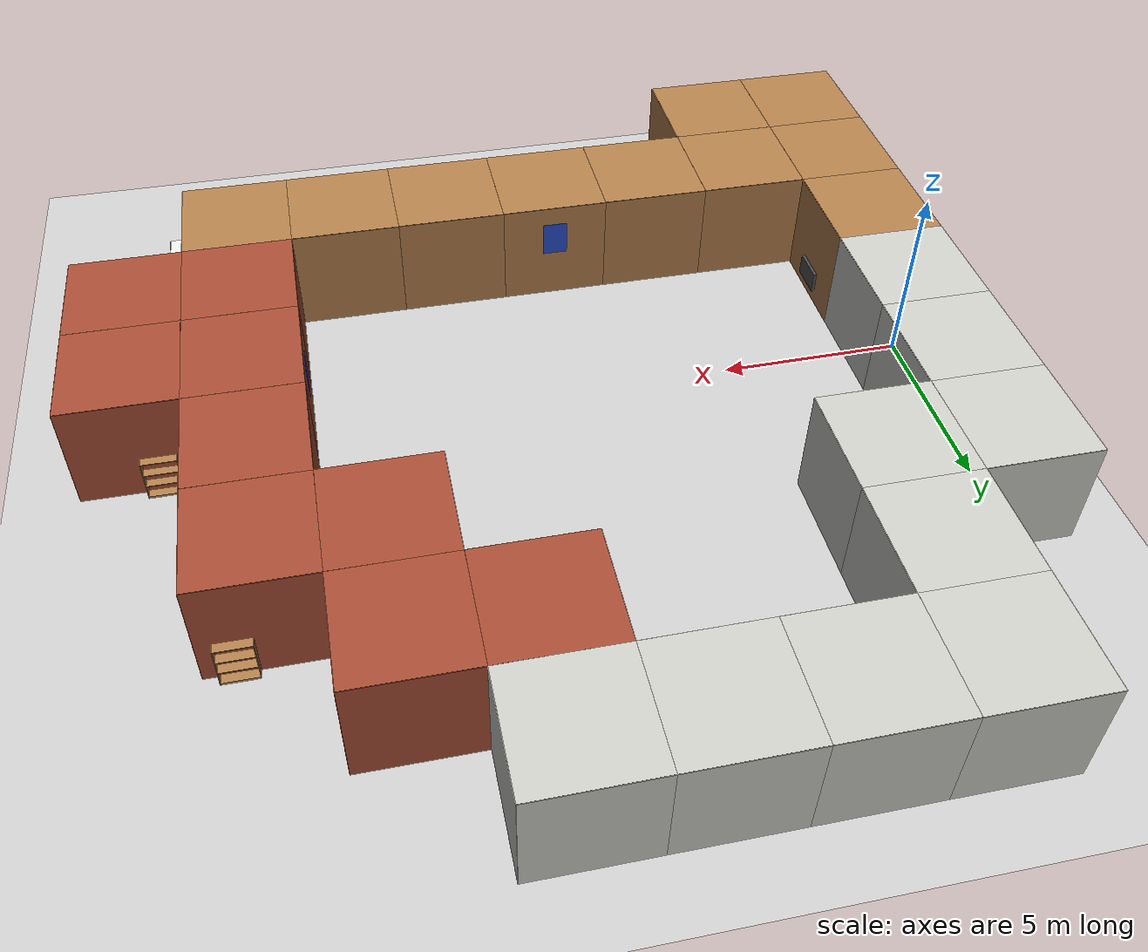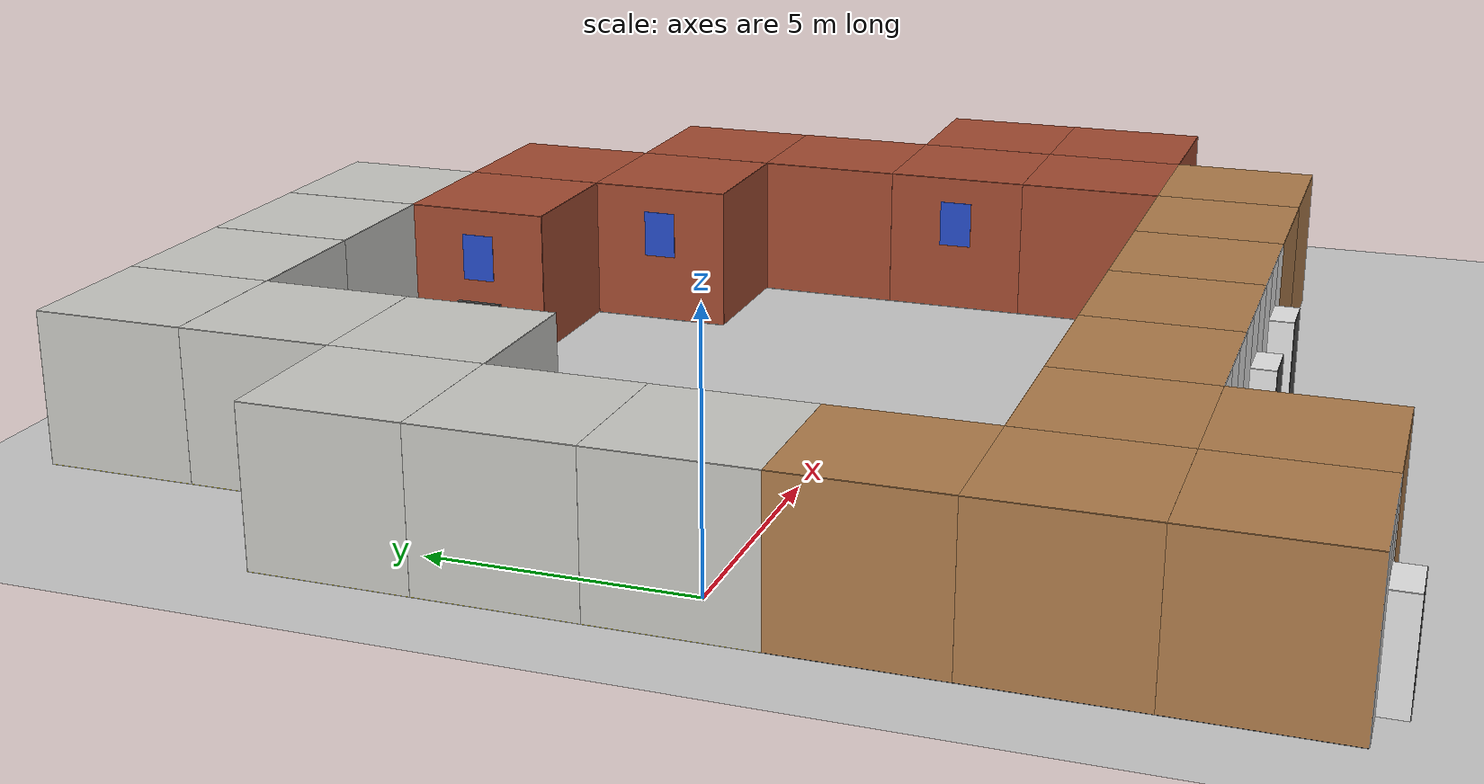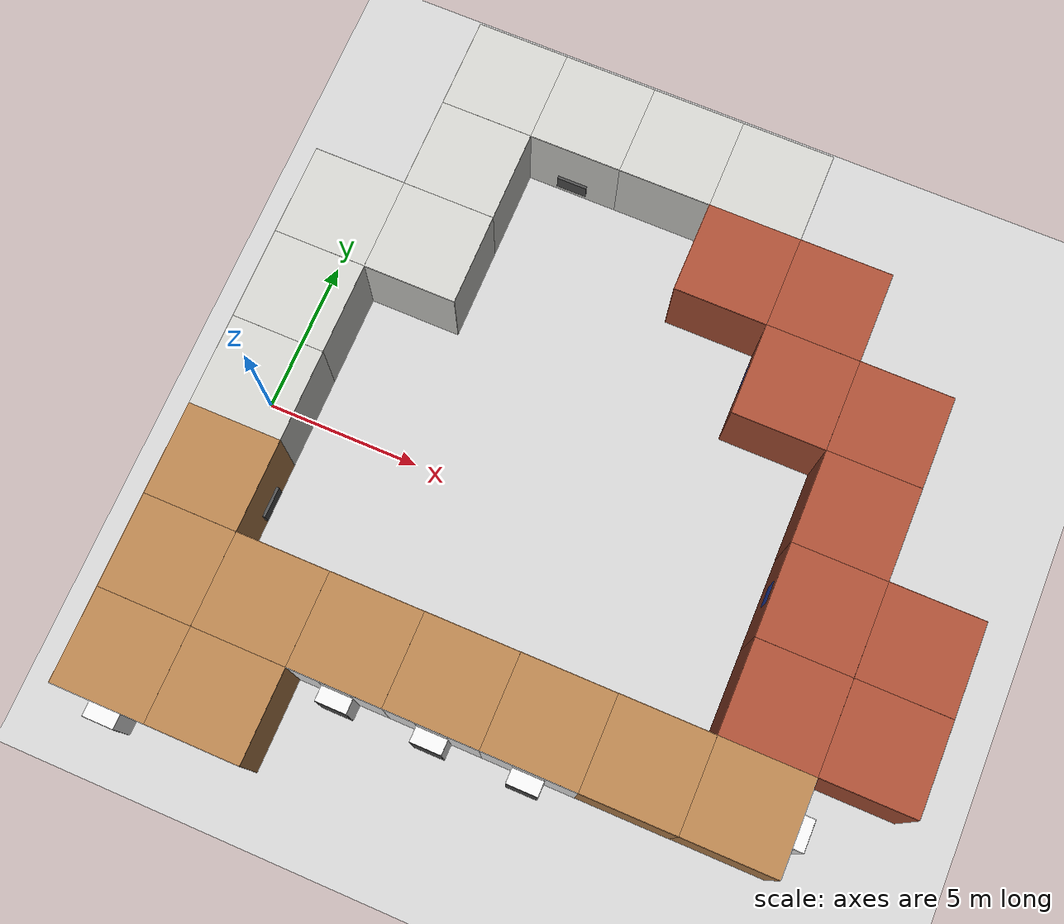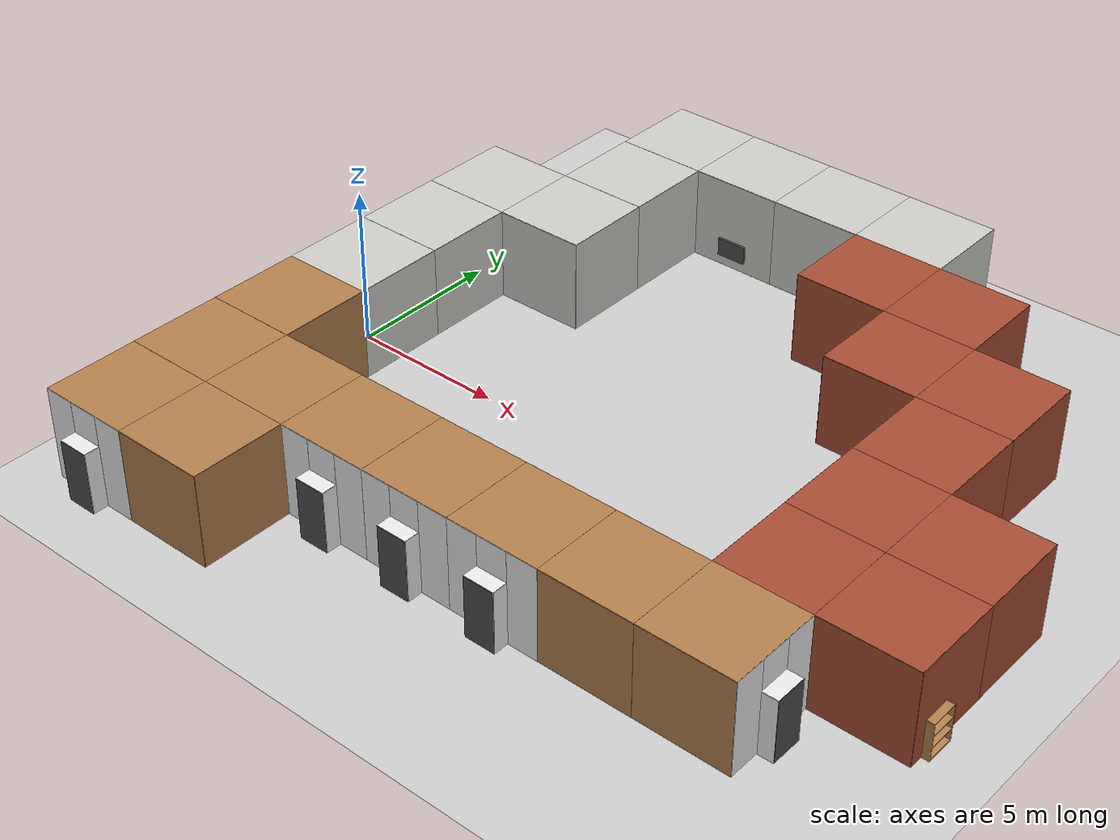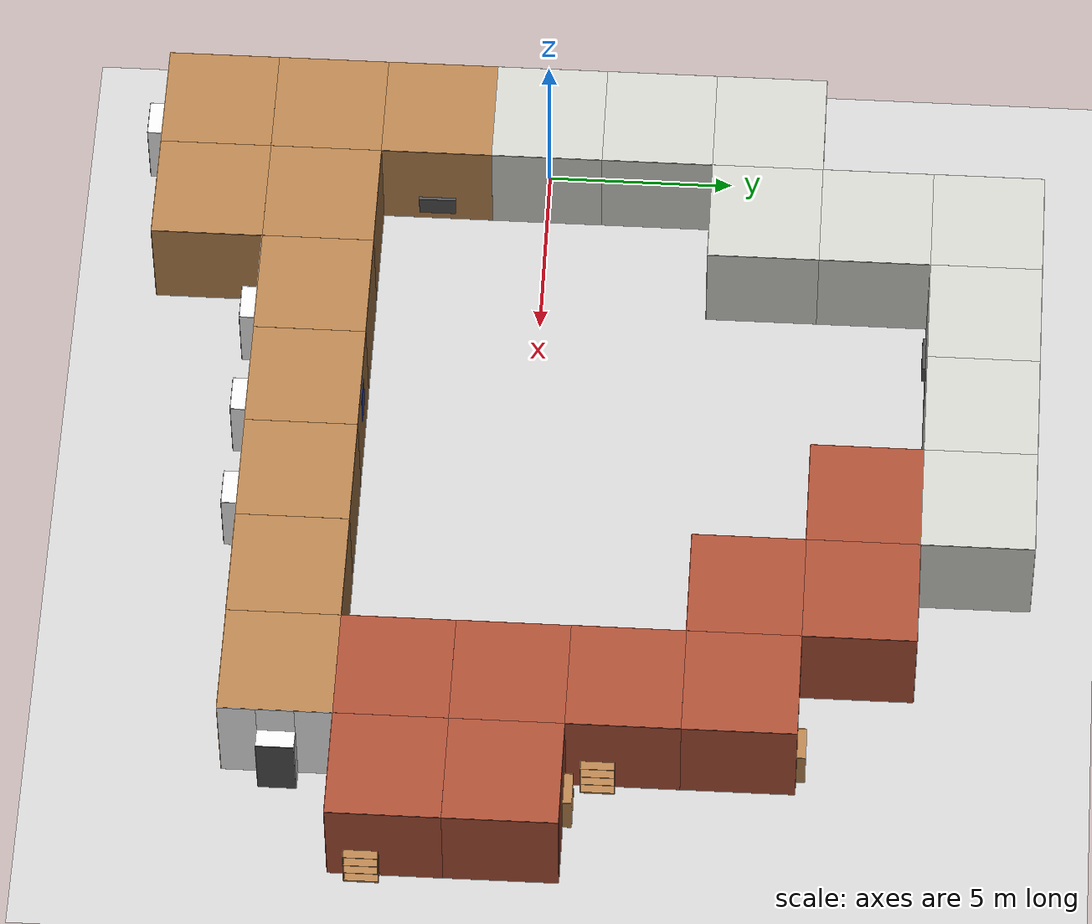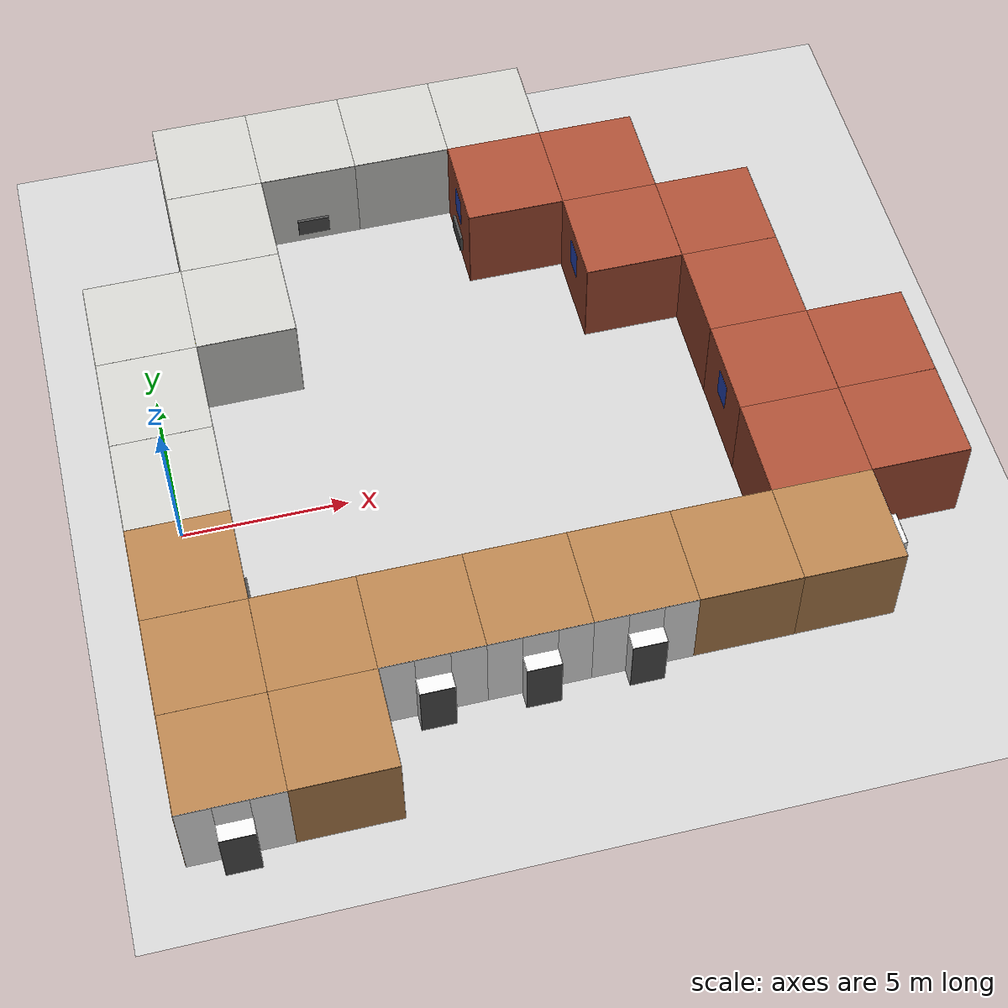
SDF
<sdf version="1.6">
 <world name="default">
  <model name="ground_plane">
   <static>1</static>
   <link name="link">
    <collision name="collision">
     <geometry><plane><normal>0 0 1</normal><size>200 200</size></plane></geometry>
     <surface><friction><ode><mu>100</mu><mu2>50</mu2></ode></friction></surface>
    </collision>
    <visual name="visual">
     <cast_shadows>0</cast_shadows>
     <geometry><plane><normal>0 0 1</normal><size>200 200</size></plane></geometry>
     <material>
      <script><uri>file://media/materials/scripts/gazebo.material</uri><name>Gazebo/Grey</name></script>
     </material>
    </visual>
   </link>
  </model>
  <gravity>0 0 -9.8</gravity>
  <magnetic_field>6e-06 2.3e-05 -4.2e-05</magnetic_field>
  <atmosphere type="adiabatic"/>
  <physics default="0" name="default_physics" type="ode">
   <max_step_size>0.001</max_step_size>
   <real_time_factor>1</real_time_factor>
   <real_time_update_rate>1000</real_time_update_rate>
  </physics>
  <scene><ambient>0.4 0.4 0.4 1</ambient><background>0.7 0.7 0.7 1</background><shadows>0</shadows></scene>
  <spherical_coordinates>
   <surface_model>EARTH_WGS84</surface_model>
   <latitude_deg>0</latitude_deg>
   <longitude_deg>0</longitude_deg>
   <elevation>0</elevation>
   <heading_deg>0</heading_deg>
  </spherical_coordinates>
  <model name="white_pipe_left_0_0_0_0">
   <static>1</static>
   <pose>0.0 0.0 2.76 0.0 0.0 0.0</pose>
   <link name="link_0">
    <visual name="visual">
     <pose>-1.3 0 0 1.57 0 0</pose>
     <geometry><cylinder><radius>0.1</radius><length>3</length></cylinder></geometry>
     <material>
      <script><uri>file://media/materials/scripts/gazebo.material</uri><name>Gazebo/White</name></script>
     </material>
    </visual>
    <collision name="collision">
     <pose>-1.3 0 0 1.57 0 0</pose>
     <geometry><cylinder><radius>0.1</radius><length>3</length></cylinder></geometry>
    </collision>
   </link>
  </model>
  <model name="white_pipe_right_0_0_0_0">
   <static>1</static>
   <pose>0.0 0.0 2.76 0.0 0.0 0.0</pose>
   <link name="link_0">
    <visual name="visual">
     <pose>1.3 0 0 1.57 0 0</pose>
     <geometry><cylinder><radius>0.1</radius><length>3</length></cylinder></geometry>
     <material>
      <script><uri>file://media/materials/scripts/gazebo.material</uri><name>Gazebo/White</name></script>
     </material>
    </visual>
    <collision name="collision">
     <pose>1.3 0 0 1.57 0 0</pose>
     <geometry><cylinder><radius>0.1</radius><length>3</length></cylinder></geometry>
    </collision>
   </link>
  </model>
  <model name="black_pipe_right_0_0_0_0">
   <static>1</static>
   <pose>0.0 0.0 2.76 0.0 0.0 0.0</pose>
   <link name="link_0">
    <visual name="visual">
     <pose>1.3 0 -0.25 1.57 0 0</pose>
     <geometry><cylinder><radius>0.1</radius><length>3</length></cylinder></geometry>
     <material>
      <script><uri>file://media/materials/scripts/gazebo.material</uri><name>Gazebo/Black</name></script>
     </material>
    </visual>
    <collision name="collision">
     <pose>1.3 0 -0.25 1.57 0 0</pose>
     <geometry><cylinder><radius>0.1</radius><length>3</length></cylinder></geometry>
    </collision>
   </link>
  </model>
  <model name="grey_pipe_right_0_0_0_0">
   <static>1</static>
   <pose>0.0 0.0 2.76 0.0 0.0 0.0</pose>
   <link name="link_0">
    <visual name="visual">
     <pose>0.7 0 0 1.57 0 0</pose>
     <geometry><cylinder><radius>0.02</radius><length>3</length></cylinder></geometry>
     <material>
      <script><uri>file://media/materials/scripts/gazebo.material</uri><name>Gazebo/Grey</name></script>
     </material>
    </visual>
    <collision name="collision">
     <pose>0.7 0 0 1.57 0 0</pose>
     <geometry><cylinder><radius>0.02</radius><length>3</length></cylinder></geometry>
    </collision>
   </link>
  </model>
  <model name="red_pipe_right_0_0_0_0">
   <static>1</static>
   <pose>0.0 0.0 2.76 0.0 0.0 0.0</pose>
   <link name="link_0">
    <visual name="visual">
     <pose>0.85 0 0 1.57 0 0</pose>
     <geometry><cylinder><radius>0.02</radius><length>3</length></cylinder></geometry>
     <material>
      <script><uri>file://media/materials/scripts/gazebo.material</uri><name>Gazebo/Red</name></script>
     </material>
    </visual>
    <collision name="collision">
     <pose>0.85 0 0 1.57 0 0</pose>
     <geometry><cylinder><radius>0.02</radius><length>3</length></cylinder></geometry>
    </collision>
   </link>
  </model>
  <model name="blue_pipe_right_0_0_0_0">
   <static>1</static>
   <pose>0.0 0.0 2.76 0.0 0.0 0.0</pose>
   <link name="link_0">
    <visual name="visual">
     <pose>1 0 0 1.57 0 0</pose>
     <geometry><cylinder><radius>0.02</radius><length>3</length></cylinder></geometry>
     <material>
      <script><uri>file://media/materials/scripts/gazebo.material</uri><name>Gazebo/Blue</name></script>
     </material>
    </visual>
    <collision name="collision">
     <pose>1 0 0 1.57 0 0</pose>
     <geometry><cylinder><radius>0.02</radius><length>3</length></cylinder></geometry>
    </collision>
   </link>
  </model>
  <model name="white_pipe_left_0_1_0_1">
   <static>1</static>
   <pose>0.0 3.0 2.76 0.0 0.0 0.0</pose>
   <link name="link_0">
    <visual name="visual">
     <pose>-1.3 0 0 1.57 0 0</pose>
     <geometry><cylinder><radius>0.1</radius><length>3</length></cylinder></geometry>
     <material>
      <script><uri>file://media/materials/scripts/gazebo.material</uri><name>Gazebo/White</name></script>
     </material>
    </visual>
    <collision name="collision">
     <pose>-1.3 0 0 1.57 0 0</pose>
     <geometry><cylinder><radius>0.1</radius><length>3</length></cylinder></geometry>
    </collision>
   </link>
  </model>
  <model name="white_pipe_right_0_1_0_1">
   <static>1</static>
   <pose>0.0 3.0 2.76 0.0 0.0 0.0</pose>
   <link name="link_0">
    <visual name="visual">
     <pose>1.3 0 0 1.57 0 0</pose>
     <geometry><cylinder><radius>0.1</radius><length>3</length></cylinder></geometry>
     <material>
      <script><uri>file://media/materials/scripts/gazebo.material</uri><name>Gazebo/White</name></script>
     </material>
    </visual>
    <collision name="collision">
     <pose>1.3 0 0 1.57 0 0</pose>
     <geometry><cylinder><radius>0.1</radius><length>3</length></cylinder></geometry>
    </collision>
   </link>
  </model>
  <model name="black_pipe_right_0_1_0_1">
   <static>1</static>
   <pose>0.0 3.0 2.76 0.0 0.0 0.0</pose>
   <link name="link_0">
    <visual name="visual">
     <pose>1.3 0 -0.25 1.57 0 0</pose>
     <geometry><cylinder><radius>0.1</radius><length>3</length></cylinder></geometry>
     <material>
      <script><uri>file://media/materials/scripts/gazebo.material</uri><name>Gazebo/Black</name></script>
     </material>
    </visual>
    <collision name="collision">
     <pose>1.3 0 -0.25 1.57 0 0</pose>
     <geometry><cylinder><radius>0.1</radius><length>3</length></cylinder></geometry>
    </collision>
   </link>
  </model>
  <model name="grey_pipe_right_0_1_0_1">
   <static>1</static>
   <pose>0.0 3.0 2.76 0.0 0.0 0.0</pose>
   <link name="link_0">
    <visual name="visual">
     <pose>0.7 0 0 1.57 0 0</pose>
     <geometry><cylinder><radius>0.02</radius><length>3</length></cylinder></geometry>
     <material>
      <script><uri>file://media/materials/scripts/gazebo.material</uri><name>Gazebo/Grey</name></script>
     </material>
    </visual>
    <collision name="collision">
     <pose>0.7 0 0 1.57 0 0</pose>
     <geometry><cylinder><radius>0.02</radius><length>3</length></cylinder></geometry>
    </collision>
   </link>
  </model>
  <model name="red_pipe_right_0_1_0_1">
   <static>1</static>
   <pose>0.0 3.0 2.76 0.0 0.0 0.0</pose>
   <link name="link_0">
    <visual name="visual">
     <pose>0.85 0 0 1.57 0 0</pose>
     <geometry><cylinder><radius>0.02</radius><length>3</length></cylinder></geometry>
     <material>
      <script><uri>file://media/materials/scripts/gazebo.material</uri><name>Gazebo/Red</name></script>
     </material>
    </visual>
    <collision name="collision">
     <pose>0.85 0 0 1.57 0 0</pose>
     <geometry><cylinder><radius>0.02</radius><length>3</length></cylinder></geometry>
    </collision>
   </link>
  </model>
  <model name="blue_pipe_right_0_1_0_1">
   <static>1</static>
   <pose>0.0 3.0 2.76 0.0 0.0 0.0</pose>
   <link name="link_0">
    <visual name="visual">
     <pose>1 0 0 1.57 0 0</pose>
     <geometry><cylinder><radius>0.02</radius><length>3</length></cylinder></geometry>
     <material>
      <script><uri>file://media/materials/scripts/gazebo.material</uri><name>Gazebo/Blue</name></script>
     </material>
    </visual>
    <collision name="collision">
     <pose>1 0 0 1.57 0 0</pose>
     <geometry><cylinder><radius>0.02</radius><length>3</length></cylinder></geometry>
    </collision>
   </link>
  </model>
  <model name="white_pipe_right_0_2_0_2">
   <static>1</static>
   <pose>0.0 6.0 2.76 0.0 0.0 0.0</pose>
   <link name="link_0">
    <visual name="visual">
     <pose>1.3 0 0 1.57 0 0</pose>
     <geometry><cylinder><radius>0.1</radius><length>3</length></cylinder></geometry>
     <material>
      <script><uri>file://media/materials/scripts/gazebo.material</uri><name>Gazebo/White</name></script>
     </material>
    </visual>
    <collision name="collision">
     <pose>1.3 0 0 1.57 0 0</pose>
     <geometry><cylinder><radius>0.1</radius><length>3</length></cylinder></geometry>
    </collision>
   </link>
  </model>
  <model name="black_pipe_right_0_2_0_2">
   <static>1</static>
   <pose>0.0 6.0 2.76 0.0 0.0 0.0</pose>
   <link name="link_0">
    <visual name="visual">
     <pose>1.3 0 -0.25 1.57 0 0</pose>
     <geometry><cylinder><radius>0.1</radius><length>3</length></cylinder></geometry>
     <material>
      <script><uri>file://media/materials/scripts/gazebo.material</uri><name>Gazebo/Black</name></script>
     </material>
    </visual>
    <collision name="collision">
     <pose>1.3 0 -0.25 1.57 0 0</pose>
     <geometry><cylinder><radius>0.1</radius><length>3</length></cylinder></geometry>
    </collision>
   </link>
  </model>
  <model name="grey_pipe_right_0_2_0_2">
   <static>1</static>
   <pose>0.0 6.0 2.76 0.0 0.0 0.0</pose>
   <link name="link_0">
    <visual name="visual">
     <pose>0.7 0 0 1.57 0 0</pose>
     <geometry><cylinder><radius>0.02</radius><length>3</length></cylinder></geometry>
     <material>
      <script><uri>file://media/materials/scripts/gazebo.material</uri><name>Gazebo/Grey</name></script>
     </material>
    </visual>
    <collision name="collision">
     <pose>0.7 0 0 1.57 0 0</pose>
     <geometry><cylinder><radius>0.02</radius><length>3</length></cylinder></geometry>
    </collision>
   </link>
  </model>
  <model name="red_pipe_right_0_2_0_2">
   <static>1</static>
   <pose>0.0 6.0 2.76 0.0 0.0 0.0</pose>
   <link name="link_0">
    <visual name="visual">
     <pose>0.85 0 0 1.57 0 0</pose>
     <geometry><cylinder><radius>0.02</radius><length>3</length></cylinder></geometry>
     <material>
      <script><uri>file://media/materials/scripts/gazebo.material</uri><name>Gazebo/Red</name></script>
     </material>
    </visual>
    <collision name="collision">
     <pose>0.85 0 0 1.57 0 0</pose>
     <geometry><cylinder><radius>0.02</radius><length>3</length></cylinder></geometry>
    </collision>
   </link>
  </model>
  <model name="blue_pipe_right_0_2_0_2">
   <static>1</static>
   <pose>0.0 6.0 2.76 0.0 0.0 0.0</pose>
   <link name="link_0">
    <visual name="visual">
     <pose>1 0 0 1.57 0 0</pose>
     <geometry><cylinder><radius>0.02</radius><length>3</length></cylinder></geometry>
     <material>
      <script><uri>file://media/materials/scripts/gazebo.material</uri><name>Gazebo/Blue</name></script>
     </material>
    </visual>
    <collision name="collision">
     <pose>1 0 0 1.57 0 0</pose>
     <geometry><cylinder><radius>0.02</radius><length>3</length></cylinder></geometry>
    </collision>
   </link>
  </model>
  <model name="wall_right_0_0_0_0">
   <static>1</static>
   <pose>1.5 0.0 1.5 0.0 0.0 1.57</pose>
   <link name="link">
    <collision name="collision"><geometry><box><size>3 0.02 3</size></box></geometry></collision>
    <visual name="visual">
     <material>
      <script><name>Gazebo/CeilingTiled</name><uri>file://media/materials/scripts/gazebo.material</uri></script>
      <ambient>1 1 1 1</ambient>
     </material>
     <geometry><box><size>3 0.02 3</size></box></geometry>
    </visual>
   </link>
  </model>
  <model name="wall_left_0_0_0_0">
   <static>1</static>
   <pose>-1.5 0.0 1.5 0.0 0.0 1.57</pose>
   <link name="link">
    <collision name="collision"><geometry><box><size>3 0.02 3</size></box></geometry></collision>
    <visual name="visual">
     <material>
      <script><name>Gazebo/CeilingTiled</name><uri>file://media/materials/scripts/gazebo.material</uri></script>
      <ambient>1 1 1 1</ambient>
     </material>
     <geometry><box><size>3 0.02 3</size></box></geometry>
    </visual>
   </link>
  </model>
  <model name="wall_top_0_0_0_0">
   <static>1</static>
   <pose>0.0 0.0 3.0 1.57 0.0 0.0</pose>
   <link name="link">
    <collision name="collision"><geometry><box><size>3 0.02 3</size></box></geometry></collision>
    <visual name="visual">
     <material>
      <script><name>Gazebo/CeilingTiled</name><uri>file://media/materials/scripts/gazebo.material</uri></script>
      <ambient>1 1 1 1</ambient>
     </material>
     <geometry><box><size>3 0.02 3</size></box></geometry>
    </visual>
   </link>
  </model>
  <light name="lightball_0_0_0_0_0" type="point">
   <cast_shadows>0</cast_shadows>
   <pose>-0.25 -0.25 2.99 0.0 0.0 0.0</pose>
   <diffuse>10 10 10 100</diffuse>
   <specular>10 10 10 10</specular>
  </light>
  <model name="wall_bottom_0_0_0_0">
   <static>1</static>
   <link name="link">
    <collision name="collision"><geometry><box><size>3 3 0.02</size></box></geometry></collision>
    <visual name="visual">
     <material>
      <script><name>Gazebo/Yellow</name><uri>file://media/materials/scripts/gazebo.material</uri></script>
     </material>
     <geometry><box><size>3 3 0.02</size></box></geometry>
    </visual>
   </link>
  </model>
  <model name="wall_right_0_1_0_1">
   <static>1</static>
   <pose>1.5 3.0 1.5 0.0 0.0 1.57</pose>
   <link name="link">
    <collision name="collision"><geometry><box><size>3 0.02 3</size></box></geometry></collision>
    <visual name="visual">
     <material>
      <script><name>Gazebo/CeilingTiled</name><uri>file://media/materials/scripts/gazebo.material</uri></script>
      <ambient>1 1 1 1</ambient>
     </material>
     <geometry><box><size>3 0.02 3</size></box></geometry>
    </visual>
   </link>
  </model>
  <model name="wall_left_0_1_0_1">
   <static>1</static>
   <pose>-1.5 3.0 1.5 0.0 0.0 1.57</pose>
   <link name="link">
    <collision name="collision"><geometry><box><size>3 0.02 3</size></box></geometry></collision>
    <visual name="visual">
     <material>
      <script><name>Gazebo/CeilingTiled</name><uri>file://media/materials/scripts/gazebo.material</uri></script>
      <ambient>1 1 1 1</ambient>
     </material>
     <geometry><box><size>3 0.02 3</size></box></geometry>
    </visual>
   </link>
  </model>
  <model name="wall_top_0_1_0_1">
   <static>1</static>
   <pose>0.0 3.0 3.0 1.57 0.0 0.0</pose>
   <link name="link">
    <collision name="collision"><geometry><box><size>3 0.02 3</size></box></geometry></collision>
    <visual name="visual">
     <material>
      <script><name>Gazebo/CeilingTiled</name><uri>file://media/materials/scripts/gazebo.material</uri></script>
      <ambient>1 1 1 1</ambient>
     </material>
     <geometry><box><size>3 0.02 3</size></box></geometry>
    </visual>
   </link>
  </model>
  <light name="lightball_0_0_1_0_1" type="point">
   <cast_shadows>0</cast_shadows>
   <pose>-0.25 2.75 2.99 0.0 0.0 0.0</pose>
   <diffuse>10 10 10 100</diffuse>
   <specular>10 10 10 10</specular>
  </light>
  <model name="wall_bottom_0_1_0_1">
   <static>1</static>
   <pose>0.0 3.0 0.0 0.0 0.0 0.0</pose>
   <link name="link">
    <collision name="collision"><geometry><box><size>3 3 0.02</size></box></geometry></collision>
    <visual name="visual">
     <material>
      <script><name>Gazebo/Yellow</name><uri>file://media/materials/scripts/gazebo.material</uri></script>
     </material>
     <geometry><box><size>3 3 0.02</size></box></geometry>
    </visual>
   </link>
  </model>
  <model name="wall_front_0_2_0_2">
   <static>1</static>
   <pose>0.0 7.5 1.5 0.0 0.0 0.0</pose>
   <link name="link">
    <collision name="collision"><geometry><box><size>3 0.02 3</size></box></geometry></collision>
    <visual name="visual">
     <material>
      <script><name>Gazebo/CeilingTiled</name><uri>file://media/materials/scripts/gazebo.material</uri></script>
      <ambient>1 1 1 1</ambient>
     </material>
     <geometry><box><size>3 0.02 3</size></box></geometry>
    </visual>
   </link>
  </model>
  <model name="wall_left_0_2_0_2">
   <static>1</static>
   <pose>-1.5 6.0 1.5 0.0 0.0 1.57</pose>
   <link name="link">
    <collision name="collision"><geometry><box><size>3 0.02 3</size></box></geometry></collision>
    <visual name="visual">
     <material>
      <script><name>Gazebo/CeilingTiled</name><uri>file://media/materials/scripts/gazebo.material</uri></script>
      <ambient>1 1 1 1</ambient>
     </material>
     <geometry><box><size>3 0.02 3</size></box></geometry>
    </visual>
   </link>
  </model>
  <model name="wall_top_0_2_0_2">
   <static>1</static>
   <pose>0.0 6.0 3.0 1.57 0.0 0.0</pose>
   <link name="link">
    <collision name="collision"><geometry><box><size>3 0.02 3</size></box></geometry></collision>
    <visual name="visual">
     <material>
      <script><name>Gazebo/CeilingTiled</name><uri>file://media/materials/scripts/gazebo.material</uri></script>
      <ambient>1 1 1 1</ambient>
     </material>
     <geometry><box><size>3 0.02 3</size></box></geometry>
    </visual>
   </link>
  </model>
  <light name="lightball_0_0_2_0_2" type="point">
   <cast_shadows>0</cast_shadows>
   <pose>-0.25 5.75 2.99 0.0 0.0 0.0</pose>
   <diffuse>10 10 10 100</diffuse>
   <specular>10 10 10 10</specular>
  </light>
  <model name="wall_bottom_0_2_0_2">
   <static>1</static>
   <pose>0.0 6.0 0.0 0.0 0.0 0.0</pose>
   <link name="link">
    <collision name="collision"><geometry><box><size>3 3 0.02</size></box></geometry></collision>
    <visual name="visual">
     <material>
      <script><name>Gazebo/Yellow</name><uri>file://media/materials/scripts/gazebo.material</uri></script>
     </material>
     <geometry><box><size>3 3 0.02</size></box></geometry>
    </visual>
   </link>
  </model>
  <model name="wall_front_1_2_0_3">
   <static>1</static>
   <pose>4.5 6.0 1.5 0.0 0.0 -1.57</pose>
   <link name="link">
    <collision name="collision"><geometry><box><size>3 0.02 3</size></box></geometry></collision>
    <visual name="visual">
     <material>
      <script><name>Gazebo/CeilingTiled</name><uri>file://media/materials/scripts/gazebo.material</uri></script>
      <ambient>1 1 1 1</ambient>
     </material>
     <geometry><box><size>3 0.02 3</size></box></geometry>
    </visual>
   </link>
  </model>
  <model name="wall_right_1_2_0_3">
   <static>1</static>
   <pose>3.0 4.5 1.5 0.0 0.0 0.0</pose>
   <link name="link">
    <collision name="collision"><geometry><box><size>3 0.02 3</size></box></geometry></collision>
    <visual name="visual">
     <material>
      <script><name>Gazebo/CeilingTiled</name><uri>file://media/materials/scripts/gazebo.material</uri></script>
      <ambient>1 1 1 1</ambient>
     </material>
     <geometry><box><size>3 0.02 3</size></box></geometry>
    </visual>
   </link>
  </model>
  <model name="wall_top_1_2_0_3">
   <static>1</static>
   <pose>3.0 6.0 3.0 1.57 0.0 -1.57</pose>
   <link name="link">
    <collision name="collision"><geometry><box><size>3 0.02 3</size></box></geometry></collision>
    <visual name="visual">
     <material>
      <script><name>Gazebo/CeilingTiled</name><uri>file://media/materials/scripts/gazebo.material</uri></script>
      <ambient>1 1 1 1</ambient>
     </material>
     <geometry><box><size>3 0.02 3</size></box></geometry>
    </visual>
   </link>
  </model>
  <light name="lightball_0_1_2_0_3" type="point">
   <cast_shadows>0</cast_shadows>
   <pose>2.75 5.75 2.99 0.0 0.0 0.0</pose>
   <diffuse>10 10 10 100</diffuse>
   <specular>10 10 10 10</specular>
  </light>
  <model name="wall_bottom_1_2_0_3">
   <static>1</static>
   <pose>3.0 6.0 0.0 0.0 0.0 -1.57</pose>
   <link name="link">
    <collision name="collision"><geometry><box><size>3 3 0.02</size></box></geometry></collision>
    <visual name="visual">
     <material>
      <script><name>Gazebo/Yellow</name><uri>file://media/materials/scripts/gazebo.material</uri></script>
     </material>
     <geometry><box><size>3 3 0.02</size></box></geometry>
    </visual>
   </link>
  </model>
  <model name="wall_right_1_3_0_1">
   <static>1</static>
   <pose>4.5 9.0 1.5 0.0 0.0 1.57</pose>
   <link name="link">
    <collision name="collision"><geometry><box><size>3 0.02 3</size></box></geometry></collision>
    <visual name="visual">
     <material>
      <script><name>Gazebo/CeilingTiled</name><uri>file://media/materials/scripts/gazebo.material</uri></script>
      <ambient>1 1 1 1</ambient>
     </material>
     <geometry><box><size>3 0.02 3</size></box></geometry>
    </visual>
   </link>
  </model>
  <model name="wall_left_1_3_0_1">
   <static>1</static>
   <pose>1.5 9.0 1.5 0.0 0.0 1.57</pose>
   <link name="link">
    <collision name="collision"><geometry><box><size>3 0.02 3</size></box></geometry></collision>
    <visual name="visual">
     <material>
      <script><name>Gazebo/CeilingTiled</name><uri>file://media/materials/scripts/gazebo.material</uri></script>
      <ambient>1 1 1 1</ambient>
     </material>
     <geometry><box><size>3 0.02 3</size></box></geometry>
    </visual>
   </link>
  </model>
  <model name="wall_top_1_3_0_1">
   <static>1</static>
   <pose>3.0 9.0 3.0 1.57 0.0 0.0</pose>
   <link name="link">
    <collision name="collision"><geometry><box><size>3 0.02 3</size></box></geometry></collision>
    <visual name="visual">
     <material>
      <script><name>Gazebo/CeilingTiled</name><uri>file://media/materials/scripts/gazebo.material</uri></script>
      <ambient>1 1 1 1</ambient>
     </material>
     <geometry><box><size>3 0.02 3</size></box></geometry>
    </visual>
   </link>
  </model>
  <light name="lightball_0_1_3_0_1" type="point">
   <cast_shadows>0</cast_shadows>
   <pose>2.75 8.75 2.99 0.0 0.0 0.0</pose>
   <diffuse>10 10 10 100</diffuse>
   <specular>10 10 10 10</specular>
  </light>
  <model name="wall_bottom_1_3_0_1">
   <static>1</static>
   <pose>3.0 9.0 0.0 0.0 0.0 0.0</pose>
   <link name="link">
    <collision name="collision"><geometry><box><size>3 3 0.02</size></box></geometry></collision>
    <visual name="visual">
     <material>
      <script><name>Gazebo/Yellow</name><uri>file://media/materials/scripts/gazebo.material</uri></script>
     </material>
     <geometry><box><size>3 3 0.02</size></box></geometry>
    </visual>
   </link>
  </model>
  <model name="wall_front_1_4_0_2">
   <static>1</static>
   <pose>3.0 13.5 1.5 0.0 0.0 0.0</pose>
   <link name="link">
    <collision name="collision"><geometry><box><size>3 0.02 3</size></box></geometry></collision>
    <visual name="visual">
     <material>
      <script><name>Gazebo/CeilingTiled</name><uri>file://media/materials/scripts/gazebo.material</uri></script>
      <ambient>1 1 1 1</ambient>
     </material>
     <geometry><box><size>3 0.02 3</size></box></geometry>
    </visual>
   </link>
  </model>
  <model name="wall_left_1_4_0_2">
   <static>1</static>
   <pose>1.5 12.0 1.5 0.0 0.0 1.57</pose>
   <link name="link">
    <collision name="collision"><geometry><box><size>3 0.02 3</size></box></geometry></collision>
    <visual name="visual">
     <material>
      <script><name>Gazebo/CeilingTiled</name><uri>file://media/materials/scripts/gazebo.material</uri></script>
      <ambient>1 1 1 1</ambient>
     </material>
     <geometry><box><size>3 0.02 3</size></box></geometry>
    </visual>
   </link>
  </model>
  <model name="wall_top_1_4_0_2">
   <static>1</static>
   <pose>3.0 12.0 3.0 1.57 0.0 0.0</pose>
   <link name="link">
    <collision name="collision"><geometry><box><size>3 0.02 3</size></box></geometry></collision>
    <visual name="visual">
     <material>
      <script><name>Gazebo/CeilingTiled</name><uri>file://media/materials/scripts/gazebo.material</uri></script>
      <ambient>1 1 1 1</ambient>
     </material>
     <geometry><box><size>3 0.02 3</size></box></geometry>
    </visual>
   </link>
  </model>
  <light name="lightball_0_1_4_0_2" type="point">
   <cast_shadows>0</cast_shadows>
   <pose>2.75 11.75 2.99 0.0 0.0 0.0</pose>
   <diffuse>10 10 10 100</diffuse>
   <specular>10 10 10 10</specular>
  </light>
  <model name="wall_bottom_1_4_0_2">
   <static>1</static>
   <pose>3.0 12.0 0.0 0.0 0.0 0.0</pose>
   <link name="link">
    <collision name="collision"><geometry><box><size>3 3 0.02</size></box></geometry></collision>
    <visual name="visual">
     <material>
      <script><name>Gazebo/Yellow</name><uri>file://media/materials/scripts/gazebo.material</uri></script>
     </material>
     <geometry><box><size>3 3 0.02</size></box></geometry>
    </visual>
   </link>
  </model>
  <model name="wall_right_2_4_0_1">
   <static>1</static>
   <pose>6.0 10.5 1.5 0.0 0.0 0.0</pose>
   <link name="link">
    <collision name="collision"><geometry><box><size>3 0.02 3</size></box></geometry></collision>
    <visual name="visual">
     <material>
      <script><name>Gazebo/CeilingTiled</name><uri>file://media/materials/scripts/gazebo.material</uri></script>
      <ambient>1 1 1 1</ambient>
     </material>
     <geometry><box><size>3 0.02 3</size></box></geometry>
    </visual>
   </link>
  </model>
  <model name="wall_left_2_4_0_1">
   <static>1</static>
   <pose>6.0 13.5 1.5 0.0 0.0 0.0</pose>
   <link name="link">
    <collision name="collision"><geometry><box><size>3 0.02 3</size></box></geometry></collision>
    <visual name="visual">
     <material>
      <script><name>Gazebo/CeilingTiled</name><uri>file://media/materials/scripts/gazebo.material</uri></script>
      <ambient>1 1 1 1</ambient>
     </material>
     <geometry><box><size>3 0.02 3</size></box></geometry>
    </visual>
   </link>
  </model>
  <model name="wall_top_2_4_0_1">
   <static>1</static>
   <pose>6.0 12.0 3.0 1.57 0.0 -1.57</pose>
   <link name="link">
    <collision name="collision"><geometry><box><size>3 0.02 3</size></box></geometry></collision>
    <visual name="visual">
     <material>
      <script><name>Gazebo/CeilingTiled</name><uri>file://media/materials/scripts/gazebo.material</uri></script>
      <ambient>1 1 1 1</ambient>
     </material>
     <geometry><box><size>3 0.02 3</size></box></geometry>
    </visual>
   </link>
  </model>
  <light name="lightball_0_2_4_0_1" type="point">
   <cast_shadows>0</cast_shadows>
   <pose>5.75 11.75 2.99 0.0 0.0 0.0</pose>
   <diffuse>10 10 10 100</diffuse>
   <specular>10 10 10 10</specular>
  </light>
  <model name="wall_bottom_2_4_0_1">
   <static>1</static>
   <pose>6.0 12.0 0.0 0.0 0.0 -1.57</pose>
   <link name="link">
    <collision name="collision"><geometry><box><size>3 3 0.02</size></box></geometry></collision>
    <visual name="visual">
     <material>
      <script><name>Gazebo/Yellow</name><uri>file://media/materials/scripts/gazebo.material</uri></script>
     </material>
     <geometry><box><size>3 3 0.02</size></box></geometry>
    </visual>
   </link>
  </model>
  <model name="panel_2_4_0_1">
   <static>1</static>
   <pose>6.0 10.5 0.66 0.0 0.0 -1.57</pose>
   <link name="link">
    <collision name="collision"><geometry><box><size>0.2 1 0.6</size></box></geometry></collision>
    <visual name="visual">
     <material>
      <script><name>Gazebo/DarkGrey</name><uri>file://media/materials/scripts/gazebo.material</uri></script>
     </material>
     <geometry><box><size>0.2 1 0.6</size></box></geometry>
    </visual>
   </link>
  </model>
  <model name="wall_right_3_4_0_1">
   <static>1</static>
   <pose>9.0 10.5 1.5 0.0 0.0 0.0</pose>
   <link name="link">
    <collision name="collision"><geometry><box><size>3 0.02 3</size></box></geometry></collision>
    <visual name="visual">
     <material>
      <script><name>Gazebo/CeilingTiled</name><uri>file://media/materials/scripts/gazebo.material</uri></script>
      <ambient>1 1 1 1</ambient>
     </material>
     <geometry><box><size>3 0.02 3</size></box></geometry>
    </visual>
   </link>
  </model>
  <model name="wall_left_3_4_0_1">
   <static>1</static>
   <pose>9.0 13.5 1.5 0.0 0.0 0.0</pose>
   <link name="link">
    <collision name="collision"><geometry><box><size>3 0.02 3</size></box></geometry></collision>
    <visual name="visual">
     <material>
      <script><name>Gazebo/CeilingTiled</name><uri>file://media/materials/scripts/gazebo.material</uri></script>
      <ambient>1 1 1 1</ambient>
     </material>
     <geometry><box><size>3 0.02 3</size></box></geometry>
    </visual>
   </link>
  </model>
  <model name="wall_top_3_4_0_1">
   <static>1</static>
   <pose>9.0 12.0 3.0 1.57 0.0 -1.57</pose>
   <link name="link">
    <collision name="collision"><geometry><box><size>3 0.02 3</size></box></geometry></collision>
    <visual name="visual">
     <material>
      <script><name>Gazebo/CeilingTiled</name><uri>file://media/materials/scripts/gazebo.material</uri></script>
      <ambient>1 1 1 1</ambient>
     </material>
     <geometry><box><size>3 0.02 3</size></box></geometry>
    </visual>
   </link>
  </model>
  <light name="lightball_0_3_4_0_1" type="point">
   <cast_shadows>0</cast_shadows>
   <pose>8.75 11.75 2.99 0.0 0.0 0.0</pose>
   <diffuse>10 10 10 100</diffuse>
   <specular>10 10 10 10</specular>
  </light>
  <model name="wall_bottom_3_4_0_1">
   <static>1</static>
   <pose>9.0 12.0 0.0 0.0 0.0 -1.57</pose>
   <link name="link">
    <collision name="collision"><geometry><box><size>3 3 0.02</size></box></geometry></collision>
    <visual name="visual">
     <material>
      <script><name>Gazebo/Yellow</name><uri>file://media/materials/scripts/gazebo.material</uri></script>
     </material>
     <geometry><box><size>3 3 0.02</size></box></geometry>
    </visual>
   </link>
  </model>
  <model name="wall_front_4_4_0_2">
   <static>1</static>
   <pose>13.5 12.0 1.5 0.0 0.0 -1.57</pose>
   <link name="link">
    <collision name="collision"><geometry><box><size>3 0.02 3</size></box></geometry></collision>
    <visual name="visual">
     <material>
      <script><name>Gazebo/CeilingTiled</name><uri>file://media/materials/scripts/gazebo.material</uri></script>
      <ambient>1 1 1 1</ambient>
     </material>
     <geometry><box><size>3 0.02 3</size></box></geometry>
    </visual>
   </link>
  </model>
  <model name="wall_left_4_4_0_2">
   <static>1</static>
   <pose>12.0 13.5 1.5 0.0 0.0 0.0</pose>
   <link name="link">
    <collision name="collision"><geometry><box><size>3 0.02 3</size></box></geometry></collision>
    <visual name="visual">
     <material>
      <script><name>Gazebo/CeilingTiled</name><uri>file://media/materials/scripts/gazebo.material</uri></script>
      <ambient>1 1 1 1</ambient>
     </material>
     <geometry><box><size>3 0.02 3</size></box></geometry>
    </visual>
   </link>
  </model>
  <model name="wall_top_4_4_0_2">
   <static>1</static>
   <pose>12.0 12.0 3.0 1.57 0.0 -1.57</pose>
   <link name="link">
    <collision name="collision"><geometry><box><size>3 0.02 3</size></box></geometry></collision>
    <visual name="visual">
     <material>
      <script><name>Gazebo/CeilingTiled</name><uri>file://media/materials/scripts/gazebo.material</uri></script>
      <ambient>1 1 1 1</ambient>
     </material>
     <geometry><box><size>3 0.02 3</size></box></geometry>
    </visual>
   </link>
  </model>
  <light name="lightball_0_4_4_0_2" type="point">
   <cast_shadows>0</cast_shadows>
   <pose>11.75 11.75 2.99 0.0 0.0 0.0</pose>
   <diffuse>10 10 10 100</diffuse>
   <specular>10 10 10 10</specular>
  </light>
  <model name="wall_bottom_4_4_0_2">
   <static>1</static>
   <pose>12.0 12.0 0.0 0.0 0.0 -1.57</pose>
   <link name="link">
    <collision name="collision"><geometry><box><size>3 3 0.02</size></box></geometry></collision>
    <visual name="visual">
     <material>
      <script><name>Gazebo/Yellow</name><uri>file://media/materials/scripts/gazebo.material</uri></script>
     </material>
     <geometry><box><size>3 3 0.02</size></box></geometry>
    </visual>
   </link>
  </model>
  <model name="ceiling_1_2_4_0_1">
   <pose>6.0 12.0 2.55 0.0 0.0 -1.57</pose>
   <link name="link_1">
    <visual name="visual">
     <geometry><box><size>0.8 1 0.1</size></box></geometry>
     <material>
      <script><uri>file://media/materials/scripts/gazebo.material</uri><name>Gazebo/Grey</name></script>
     </material>
    </visual>
    <collision name="collision"><geometry><box><size>0.8 1 0.1</size></box></geometry></collision>
   </link>
   <static>1</static>
  </model>
  <model name="ceiling_1_2_4_1_1">
   <pose>5.0 12.0 2.55 0.0 0.0 -1.57</pose>
   <link name="link_1">
    <visual name="visual">
     <geometry><box><size>0.8 1 0.1</size></box></geometry>
     <material>
      <script><uri>file://media/materials/scripts/gazebo.material</uri><name>Gazebo/Grey</name></script>
     </material>
    </visual>
    <collision name="collision"><geometry><box><size>0.8 1 0.1</size></box></geometry></collision>
   </link>
   <static>1</static>
  </model>
  <model name="ceiling_1_2_4_2_1">
   <pose>7.0 12.0 2.55 0.0 0.0 -1.57</pose>
   <link name="link_1">
    <visual name="visual">
     <geometry><box><size>0.8 1 0.1</size></box></geometry>
     <material>
      <script><uri>file://media/materials/scripts/gazebo.material</uri><name>Gazebo/Grey</name></script>
     </material>
    </visual>
    <collision name="collision"><geometry><box><size>0.8 1 0.1</size></box></geometry></collision>
   </link>
   <static>1</static>
  </model>
  <model name="ceiling_1_3_4_0_1">
   <pose>9.0 12.0 2.55 0.0 0.0 -1.57</pose>
   <link name="link_1">
    <visual name="visual">
     <geometry><box><size>0.8 1 0.1</size></box></geometry>
     <material>
      <script><uri>file://media/materials/scripts/gazebo.material</uri><name>Gazebo/Grey</name></script>
     </material>
    </visual>
    <collision name="collision"><geometry><box><size>0.8 1 0.1</size></box></geometry></collision>
   </link>
   <static>1</static>
  </model>
  <model name="ceiling_1_3_4_1_1">
   <pose>8.0 12.0 2.55 0.0 0.0 -1.57</pose>
   <link name="link_1">
    <visual name="visual">
     <geometry><box><size>0.8 1 0.1</size></box></geometry>
     <material>
      <script><uri>file://media/materials/scripts/gazebo.material</uri><name>Gazebo/Grey</name></script>
     </material>
    </visual>
    <collision name="collision"><geometry><box><size>0.8 1 0.1</size></box></geometry></collision>
   </link>
   <static>1</static>
  </model>
  <model name="ceiling_1_3_4_2_1">
   <pose>10.0 12.0 2.55 0.0 0.0 -1.57</pose>
   <link name="link_1">
    <visual name="visual">
     <geometry><box><size>0.8 1 0.1</size></box></geometry>
     <material>
      <script><uri>file://media/materials/scripts/gazebo.material</uri><name>Gazebo/Grey</name></script>
     </material>
    </visual>
    <collision name="collision"><geometry><box><size>0.8 1 0.1</size></box></geometry></collision>
   </link>
   <static>1</static>
  </model>
  <model name="ceiling_1_4_4_0_2">
   <pose>11.0 12.0 2.55 0.0 0.0 -1.57</pose>
   <link name="link_1">
    <visual name="visual">
     <geometry><box><size>0.8 1 0.1</size></box></geometry>
     <material>
      <script><uri>file://media/materials/scripts/gazebo.material</uri><name>Gazebo/Grey</name></script>
     </material>
    </visual>
    <collision name="collision"><geometry><box><size>0.8 1 0.1</size></box></geometry></collision>
   </link>
   <static>1</static>
  </model>
  <model name="ceiling_1_4_4_1_2">
   <pose>12.0 11.0 2.55 0.0 0.0 0.0</pose>
   <link name="link_1">
    <visual name="visual">
     <geometry><box><size>0.8 1 0.1</size></box></geometry>
     <material>
      <script><uri>file://media/materials/scripts/gazebo.material</uri><name>Gazebo/Grey</name></script>
     </material>
    </visual>
    <collision name="collision"><geometry><box><size>0.8 1 0.1</size></box></geometry></collision>
   </link>
   <static>1</static>
  </model>
  <model name="panel_4_3_0_3">
   <static>1</static>
   <pose>10.5 9.0 0.66 0.0 0.0 3.14</pose>
   <link name="link">
    <collision name="collision"><geometry><box><size>0.2 1 0.6</size></box></geometry></collision>
    <visual name="visual">
     <material>
      <script><name>Gazebo/DarkGrey</name><uri>file://media/materials/scripts/gazebo.material</uri></script>
     </material>
     <geometry><box><size>0.2 1 0.6</size></box></geometry>
    </visual>
   </link>
  </model>
  <model name="wall_front_4_3_0_3">
   <static>1</static>
   <pose>12.0 7.5 1.5 0.0 0.0 3.14</pose>
   <link name="link">
    <collision name="collision"><geometry><box><size>3 0.02 3</size></box></geometry></collision>
    <visual name="visual">
     <material>
      <script><name>Gazebo/Bricks</name><uri>file://media/materials/scripts/gazebo.material</uri></script>
     </material>
     <geometry><box><size>3 0.02 3</size></box></geometry>
    </visual>
   </link>
  </model>
  <model name="wall_right_4_3_0_3">
   <static>1</static>
   <pose>10.5 9.0 1.5 0.0 0.0 4.71</pose>
   <link name="link">
    <collision name="collision"><geometry><box><size>3 0.02 3</size></box></geometry></collision>
    <visual name="visual">
     <material>
      <script><name>Gazebo/Bricks</name><uri>file://media/materials/scripts/gazebo.material</uri></script>
     </material>
     <geometry><box><size>3 0.02 3</size></box></geometry>
    </visual>
   </link>
  </model>
  <model name="wall_top_4_3_0_3">
   <static>1</static>
   <pose>12.0 9.0 3.0 1.57 0.0 3.14</pose>
   <link name="link">
    <collision name="collision"><geometry><box><size>3 0.02 3</size></box></geometry></collision>
    <visual name="visual">
     <material>
      <script><name>Gazebo/Bricks</name><uri>file://media/materials/scripts/gazebo.material</uri></script>
     </material>
     <geometry><box><size>3 0.02 3</size></box></geometry>
    </visual>
   </link>
  </model>
  <light name="lightball_0_4_3_0_3" type="point">
   <cast_shadows>0</cast_shadows>
   <pose>11.75 8.75 2.99 0.0 0.0 0.0</pose>
   <diffuse>10 10 10 100</diffuse>
   <specular>10 10 10 10</specular>
  </light>
  <model name="ceiling_1_4_3_0_3">
   <pose>12.0 10.0 2.55 0.0 0.0 3.14</pose>
   <link name="link_1">
    <visual name="visual">
     <geometry><box><size>0.8 1 0.1</size></box></geometry>
     <material>
      <script><uri>file://media/materials/scripts/gazebo.material</uri><name>Gazebo/Grey</name></script>
     </material>
    </visual>
    <collision name="collision"><geometry><box><size>0.8 1 0.1</size></box></geometry></collision>
   </link>
   <static>1</static>
  </model>
  <model name="ceiling_1_4_3_1_3">
   <pose>13.0 9.0 2.55 0.0 0.0 4.71</pose>
   <link name="link_1">
    <visual name="visual">
     <geometry><box><size>0.8 1 0.1</size></box></geometry>
     <material>
      <script><uri>file://media/materials/scripts/gazebo.material</uri><name>Gazebo/Grey</name></script>
     </material>
    </visual>
    <collision name="collision"><geometry><box><size>0.8 1 0.1</size></box></geometry></collision>
   </link>
   <static>1</static>
  </model>
  <model name="wall_bottom_4_3_0_3">
   <static>1</static>
   <pose>12.0 9.0 0.0 0.0 0.0 3.14</pose>
   <link name="link">
    <collision name="collision"><geometry><box><size>3 3 0.02</size></box></geometry></collision>
    <visual name="visual">
     <material>
      <script><name>Gazebo/Grey</name><uri>file://media/materials/scripts/gazebo.material</uri></script>
     </material>
     <geometry><box><size>3 3 0.02</size></box></geometry>
    </visual>
   </link>
  </model>
  <model name="panel_4_3_0_3">
   <static>1</static>
   <pose>10.5 9.0 1.95 0.0 0.0 3.14</pose>
   <link name="link">
    <collision name="collision"><geometry><box><size>0.04 0.7 1</size></box></geometry></collision>
    <visual name="visual">
     <material>
      <script><name>Gazebo/Blue</name><uri>file://media/materials/scripts/gazebo.material</uri></script>
     </material>
     <geometry><box><size>0.04 0.7 1</size></box></geometry>
    </visual>
   </link>
  </model>
  <model name="wall_front_5_3_0_2">
   <static>1</static>
   <pose>16.5 9.0 1.5 0.0 0.0 -1.57</pose>
   <link name="link">
    <collision name="collision"><geometry><box><size>3 0.02 3</size></box></geometry></collision>
    <visual name="visual">
     <material>
      <script><name>Gazebo/Bricks</name><uri>file://media/materials/scripts/gazebo.material</uri></script>
     </material>
     <geometry><box><size>3 0.02 3</size></box></geometry>
    </visual>
   </link>
  </model>
  <model name="wall_left_5_3_0_2">
   <static>1</static>
   <pose>15.0 10.5 1.5 0.0 0.0 0.0</pose>
   <link name="link">
    <collision name="collision"><geometry><box><size>3 0.02 3</size></box></geometry></collision>
    <visual name="visual">
     <material>
      <script><name>Gazebo/Bricks</name><uri>file://media/materials/scripts/gazebo.material</uri></script>
     </material>
     <geometry><box><size>3 0.02 3</size></box></geometry>
    </visual>
   </link>
  </model>
  <model name="wall_top_5_3_0_2">
   <static>1</static>
   <pose>15.0 9.0 3.0 1.57 0.0 -1.57</pose>
   <link name="link">
    <collision name="collision"><geometry><box><size>3 0.02 3</size></box></geometry></collision>
    <visual name="visual">
     <material>
      <script><name>Gazebo/Bricks</name><uri>file://media/materials/scripts/gazebo.material</uri></script>
     </material>
     <geometry><box><size>3 0.02 3</size></box></geometry>
    </visual>
   </link>
  </model>
  <light name="lightball_0_5_3_0_2" type="point">
   <cast_shadows>0</cast_shadows>
   <pose>14.75 8.75 2.99 0.0 0.0 0.0</pose>
   <diffuse>10 10 10 100</diffuse>
   <specular>10 10 10 10</specular>
  </light>
  <model name="ceiling_1_5_3_0_2">
   <pose>14.0 9.0 2.55 0.0 0.0 -1.57</pose>
   <link name="link_1">
    <visual name="visual">
     <geometry><box><size>0.8 1 0.1</size></box></geometry>
     <material>
      <script><uri>file://media/materials/scripts/gazebo.material</uri><name>Gazebo/Grey</name></script>
     </material>
    </visual>
    <collision name="collision"><geometry><box><size>0.8 1 0.1</size></box></geometry></collision>
   </link>
   <static>1</static>
  </model>
  <model name="ceiling_1_5_3_1_2">
   <pose>15.0 8.0 2.55 0.0 0.0 0.0</pose>
   <link name="link_1">
    <visual name="visual">
     <geometry><box><size>0.8 1 0.1</size></box></geometry>
     <material>
      <script><uri>file://media/materials/scripts/gazebo.material</uri><name>Gazebo/Grey</name></script>
     </material>
    </visual>
    <collision name="collision"><geometry><box><size>0.8 1 0.1</size></box></geometry></collision>
   </link>
   <static>1</static>
  </model>
  <model name="wall_bottom_5_3_0_2">
   <static>1</static>
   <pose>15.0 9.0 0.0 0.0 0.0 -1.57</pose>
   <link name="link">
    <collision name="collision"><geometry><box><size>3 3 0.02</size></box></geometry></collision>
    <visual name="visual">
     <material>
      <script><name>Gazebo/Grey</name><uri>file://media/materials/scripts/gazebo.material</uri></script>
     </material>
     <geometry><box><size>3 3 0.02</size></box></geometry>
    </visual>
   </link>
  </model>
  <model name="wall_front_5_2_0_3">
   <static>1</static>
   <pose>15.0 4.5 1.5 0.0 0.0 3.14</pose>
   <link name="link">
    <collision name="collision"><geometry><box><size>3 0.02 3</size></box></geometry></collision>
    <visual name="visual">
     <material>
      <script><name>Gazebo/Bricks</name><uri>file://media/materials/scripts/gazebo.material</uri></script>
     </material>
     <geometry><box><size>3 0.02 3</size></box></geometry>
    </visual>
   </link>
  </model>
  <model name="wall_right_5_2_0_3">
   <static>1</static>
   <pose>13.5 6.0 1.5 0.0 0.0 4.71</pose>
   <link name="link">
    <collision name="collision"><geometry><box><size>3 0.02 3</size></box></geometry></collision>
    <visual name="visual">
     <material>
      <script><name>Gazebo/Bricks</name><uri>file://media/materials/scripts/gazebo.material</uri></script>
     </material>
     <geometry><box><size>3 0.02 3</size></box></geometry>
    </visual>
   </link>
  </model>
  <model name="wall_top_5_2_0_3">
   <static>1</static>
   <pose>15.0 6.0 3.0 1.57 0.0 3.14</pose>
   <link name="link">
    <collision name="collision"><geometry><box><size>3 0.02 3</size></box></geometry></collision>
    <visual name="visual">
     <material>
      <script><name>Gazebo/Bricks</name><uri>file://media/materials/scripts/gazebo.material</uri></script>
     </material>
     <geometry><box><size>3 0.02 3</size></box></geometry>
    </visual>
   </link>
  </model>
  <light name="lightball_0_5_2_0_3" type="point">
   <cast_shadows>0</cast_shadows>
   <pose>14.75 5.75 2.99 0.0 0.0 0.0</pose>
   <diffuse>10 10 10 100</diffuse>
   <specular>10 10 10 10</specular>
  </light>
  <model name="ceiling_1_5_2_0_3">
   <pose>15.0 7.0 2.55 0.0 0.0 3.14</pose>
   <link name="link_1">
    <visual name="visual">
     <geometry><box><size>0.8 1 0.1</size></box></geometry>
     <material>
      <script><uri>file://media/materials/scripts/gazebo.material</uri><name>Gazebo/Grey</name></script>
     </material>
    </visual>
    <collision name="collision"><geometry><box><size>0.8 1 0.1</size></box></geometry></collision>
   </link>
   <static>1</static>
  </model>
  <model name="ceiling_1_5_2_1_3">
   <pose>16.0 6.0 2.55 0.0 0.0 4.71</pose>
   <link name="link_1">
    <visual name="visual">
     <geometry><box><size>0.8 1 0.1</size></box></geometry>
     <material>
      <script><uri>file://media/materials/scripts/gazebo.material</uri><name>Gazebo/Grey</name></script>
     </material>
    </visual>
    <collision name="collision"><geometry><box><size>0.8 1 0.1</size></box></geometry></collision>
   </link>
   <static>1</static>
  </model>
  <model name="wall_bottom_5_2_0_3">
   <static>1</static>
   <pose>15.0 6.0 0.0 0.0 0.0 3.14</pose>
   <link name="link">
    <collision name="collision"><geometry><box><size>3 3 0.02</size></box></geometry></collision>
    <visual name="visual">
     <material>
      <script><name>Gazebo/Grey</name><uri>file://media/materials/scripts/gazebo.material</uri></script>
     </material>
     <geometry><box><size>3 3 0.02</size></box></geometry>
    </visual>
   </link>
  </model>
  <model name="panel_5_2_0_3">
   <static>1</static>
   <pose>13.5 6.0 1.95 0.0 0.0 3.14</pose>
   <link name="link">
    <collision name="collision"><geometry><box><size>0.04 0.7 1</size></box></geometry></collision>
    <visual name="visual">
     <material>
      <script><name>Gazebo/Blue</name><uri>file://media/materials/scripts/gazebo.material</uri></script>
     </material>
     <geometry><box><size>0.04 0.7 1</size></box></geometry>
    </visual>
   </link>
  </model>
  <model name="wall_front_6_2_0_2">
   <static>1</static>
   <pose>19.5 6.0 1.5 0.0 0.0 -1.57</pose>
   <link name="link">
    <collision name="collision"><geometry><box><size>3 0.02 3</size></box></geometry></collision>
    <visual name="visual">
     <material>
      <script><name>Gazebo/Bricks</name><uri>file://media/materials/scripts/gazebo.material</uri></script>
     </material>
     <geometry><box><size>3 0.02 3</size></box></geometry>
    </visual>
   </link>
  </model>
  <model name="wall_left_6_2_0_2">
   <static>1</static>
   <pose>18.0 7.5 1.5 0.0 0.0 0.0</pose>
   <link name="link">
    <collision name="collision"><geometry><box><size>3 0.02 3</size></box></geometry></collision>
    <visual name="visual">
     <material>
      <script><name>Gazebo/Bricks</name><uri>file://media/materials/scripts/gazebo.material</uri></script>
     </material>
     <geometry><box><size>3 0.02 3</size></box></geometry>
    </visual>
   </link>
  </model>
  <model name="wall_top_6_2_0_2">
   <static>1</static>
   <pose>18.0 6.0 3.0 1.57 0.0 -1.57</pose>
   <link name="link">
    <collision name="collision"><geometry><box><size>3 0.02 3</size></box></geometry></collision>
    <visual name="visual">
     <material>
      <script><name>Gazebo/Bricks</name><uri>file://media/materials/scripts/gazebo.material</uri></script>
     </material>
     <geometry><box><size>3 0.02 3</size></box></geometry>
    </visual>
   </link>
  </model>
  <light name="lightball_0_6_2_0_2" type="point">
   <cast_shadows>0</cast_shadows>
   <pose>17.75 5.75 2.99 0.0 0.0 0.0</pose>
   <diffuse>10 10 10 100</diffuse>
   <specular>10 10 10 10</specular>
  </light>
  <model name="ceiling_1_6_2_0_2">
   <pose>17.0 6.0 2.55 0.0 0.0 -1.57</pose>
   <link name="link_1">
    <visual name="visual">
     <geometry><box><size>0.8 1 0.1</size></box></geometry>
     <material>
      <script><uri>file://media/materials/scripts/gazebo.material</uri><name>Gazebo/Grey</name></script>
     </material>
    </visual>
    <collision name="collision"><geometry><box><size>0.8 1 0.1</size></box></geometry></collision>
   </link>
   <static>1</static>
  </model>
  <model name="ceiling_1_6_2_1_2">
   <pose>18.0 5.0 2.55 0.0 0.0 0.0</pose>
   <link name="link_1">
    <visual name="visual">
     <geometry><box><size>0.8 1 0.1</size></box></geometry>
     <material>
      <script><uri>file://media/materials/scripts/gazebo.material</uri><name>Gazebo/Grey</name></script>
     </material>
    </visual>
    <collision name="collision"><geometry><box><size>0.8 1 0.1</size></box></geometry></collision>
   </link>
   <static>1</static>
  </model>
  <model name="bookshelf_6_2_0_2">
   <static>true</static>
   <pose>18.663503850525 7.35 0.0 0.0 0.0 -1.57</pose>
   <link name="link">
    <pose>0 0 0 0 0 -1.57</pose>
    <inertial><mass>1.0</mass></inertial>
    <collision name="back">
     <pose>0 0.005 0.6 0 0 0</pose>
     <geometry><box><size>0.9 0.01 1.2</size></box></geometry>
    </collision>
    <visual name="visual1">
     <pose>0 0.005 0.6 0 0 0</pose>
     <geometry><box><size>0.9 0.01 1.2</size></box></geometry>
     <material>
      <script><uri>file://media/materials/scripts/gazebo.material</uri><name>Gazebo/Wood</name></script>
     </material>
    </visual>
    <collision name="left_side">
     <pose>0.45 -0.195 0.6 0 0 0</pose>
     <geometry><box><size>0.02 0.4 1.2</size></box></geometry>
    </collision>
    <visual name="visual2">
     <pose>0.45 -0.195 0.6 0 0 0</pose>
     <geometry><box><size>0.02 0.4 1.2</size></box></geometry>
     <material>
      <script><uri>file://media/materials/scripts/gazebo.material</uri><name>Gazebo/Wood</name></script>
     </material>
    </visual>
    <collision name="right_side">
     <pose>-0.45 -0.195 0.6 0 0 0</pose>
     <geometry><box><size>0.02 0.4 1.2</size></box></geometry>
    </collision>
    <visual name="visual3">
     <pose>-0.45 -0.195 0.6 0 0 0</pose>
     <geometry><box><size>0.02 0.4 1.2</size></box></geometry>
     <material>
      <script><uri>file://media/materials/scripts/gazebo.material</uri><name>Gazebo/Wood</name></script>
     </material>
    </visual>
    <collision name="bottom">
     <pose>0 -0.195 0.03 0 0 0</pose>
     <geometry><box><size>0.88 0.4 0.06</size></box></geometry>
    </collision>
    <visual name="visual4">
     <pose>0 -0.195 0.03 0 0 0</pose>
     <geometry><box><size>0.88 0.4 0.06</size></box></geometry>
     <material>
      <script><uri>file://media/materials/scripts/gazebo.material</uri><name>Gazebo/Wood</name></script>
     </material>
    </visual>
    <collision name="top">
     <pose>0 -0.195 1.19 0 0 0</pose>
     <geometry><box><size>0.88 0.4 0.02</size></box></geometry>
    </collision>
    <visual name="visual5">
     <pose>0 -0.195 1.19 0 0 0</pose>
     <geometry><box><size>0.88 0.4 0.02</size></box></geometry>
     <material>
      <script><uri>file://media/materials/scripts/gazebo.material</uri><name>Gazebo/Wood</name></script>
     </material>
    </visual>
    <collision name="low_shelf">
     <pose>0 -0.195 0.43 0 0 0</pose>
     <geometry><box><size>0.88 0.4 0.02</size></box></geometry>
    </collision>
    <visual name="visual6">
     <pose>0 -0.195 0.43 0 0 0</pose>
     <geometry><box><size>0.88 0.4 0.02</size></box></geometry>
     <material>
      <script><uri>file://media/materials/scripts/gazebo.material</uri><name>Gazebo/Wood</name></script>
     </material>
    </visual>
    <collision name="high_shelf">
     <pose>0 -0.195 0.8 0 0 0</pose>
     <geometry><box><size>0.88 0.4 0.02</size></box></geometry>
    </collision>
    <visual name="visual7">
     <pose>0 -0.195 0.8 0 0 0</pose>
     <geometry><box><size>0.88 0.4 0.02</size></box></geometry>
     <material>
      <script><uri>file://media/materials/scripts/gazebo.material</uri><name>Gazebo/Wood</name></script>
     </material>
    </visual>
   </link>
  </model>
  <model name="wall_bottom_6_2_0_2">
   <static>1</static>
   <pose>18.0 6.0 0.0 0.0 0.0 -1.57</pose>
   <link name="link">
    <collision name="collision"><geometry><box><size>3 3 0.02</size></box></geometry></collision>
    <visual name="visual">
     <material>
      <script><name>Gazebo/Grey</name><uri>file://media/materials/scripts/gazebo.material</uri></script>
     </material>
     <geometry><box><size>3 3 0.02</size></box></geometry>
    </visual>
   </link>
  </model>
  <model name="wall_right_6_1_0_1">
   <static>1</static>
   <pose>16.5 3.0 1.5 0.0 0.0 4.71</pose>
   <link name="link">
    <collision name="collision"><geometry><box><size>3 0.02 3</size></box></geometry></collision>
    <visual name="visual">
     <material>
      <script><name>Gazebo/Bricks</name><uri>file://media/materials/scripts/gazebo.material</uri></script>
     </material>
     <geometry><box><size>3 0.02 3</size></box></geometry>
    </visual>
   </link>
  </model>
  <model name="wall_left_6_1_0_1">
   <static>1</static>
   <pose>19.5 3.0 1.5 0.0 0.0 4.71</pose>
   <link name="link">
    <collision name="collision"><geometry><box><size>3 0.02 3</size></box></geometry></collision>
    <visual name="visual">
     <material>
      <script><name>Gazebo/Bricks</name><uri>file://media/materials/scripts/gazebo.material</uri></script>
     </material>
     <geometry><box><size>3 0.02 3</size></box></geometry>
    </visual>
   </link>
  </model>
  <model name="wall_top_6_1_0_1">
   <static>1</static>
   <pose>18.0 3.0 3.0 1.57 0.0 3.14</pose>
   <link name="link">
    <collision name="collision"><geometry><box><size>3 0.02 3</size></box></geometry></collision>
    <visual name="visual">
     <material>
      <script><name>Gazebo/Bricks</name><uri>file://media/materials/scripts/gazebo.material</uri></script>
     </material>
     <geometry><box><size>3 0.02 3</size></box></geometry>
    </visual>
   </link>
  </model>
  <light name="lightball_0_6_1_0_1" type="point">
   <cast_shadows>0</cast_shadows>
   <pose>17.75 2.75 2.99 0.0 0.0 0.0</pose>
   <diffuse>10 10 10 100</diffuse>
   <specular>10 10 10 10</specular>
  </light>
  <model name="ceiling_1_6_1_0_1">
   <pose>18.0 3.0 2.55 0.0 0.0 3.14</pose>
   <link name="link_1">
    <visual name="visual">
     <geometry><box><size>0.8 1 0.1</size></box></geometry>
     <material>
      <script><uri>file://media/materials/scripts/gazebo.material</uri><name>Gazebo/Grey</name></script>
     </material>
    </visual>
    <collision name="collision"><geometry><box><size>0.8 1 0.1</size></box></geometry></collision>
   </link>
   <static>1</static>
  </model>
  <model name="ceiling_1_6_1_1_1">
   <pose>18.0 4.0 2.55 0.0 0.0 3.14</pose>
   <link name="link_1">
    <visual name="visual">
     <geometry><box><size>0.8 1 0.1</size></box></geometry>
     <material>
      <script><uri>file://media/materials/scripts/gazebo.material</uri><name>Gazebo/Grey</name></script>
     </material>
    </visual>
    <collision name="collision"><geometry><box><size>0.8 1 0.1</size></box></geometry></collision>
   </link>
   <static>1</static>
  </model>
  <model name="ceiling_1_6_1_2_1">
   <pose>18.0 2.0 2.55 0.0 0.0 3.14</pose>
   <link name="link_1">
    <visual name="visual">
     <geometry><box><size>0.8 1 0.1</size></box></geometry>
     <material>
      <script><uri>file://media/materials/scripts/gazebo.material</uri><name>Gazebo/Grey</name></script>
     </material>
    </visual>
    <collision name="collision"><geometry><box><size>0.8 1 0.1</size></box></geometry></collision>
   </link>
   <static>1</static>
  </model>
  <model name="bookshelf_6_1_0_1">
   <static>true</static>
   <pose>19.35 2.3519090675655 0.0 0.0 0.0 3.14</pose>
   <link name="link">
    <pose>0 0 0 0 0 -1.57</pose>
    <inertial><mass>1.0</mass></inertial>
    <collision name="back">
     <pose>0 0.005 0.6 0 0 0</pose>
     <geometry><box><size>0.9 0.01 1.2</size></box></geometry>
    </collision>
    <visual name="visual1">
     <pose>0 0.005 0.6 0 0 0</pose>
     <geometry><box><size>0.9 0.01 1.2</size></box></geometry>
     <material>
      <script><uri>file://media/materials/scripts/gazebo.material</uri><name>Gazebo/Wood</name></script>
     </material>
    </visual>
    <collision name="left_side">
     <pose>0.45 -0.195 0.6 0 0 0</pose>
     <geometry><box><size>0.02 0.4 1.2</size></box></geometry>
    </collision>
    <visual name="visual2">
     <pose>0.45 -0.195 0.6 0 0 0</pose>
     <geometry><box><size>0.02 0.4 1.2</size></box></geometry>
     <material>
      <script><uri>file://media/materials/scripts/gazebo.material</uri><name>Gazebo/Wood</name></script>
     </material>
    </visual>
    <collision name="right_side">
     <pose>-0.45 -0.195 0.6 0 0 0</pose>
     <geometry><box><size>0.02 0.4 1.2</size></box></geometry>
    </collision>
    <visual name="visual3">
     <pose>-0.45 -0.195 0.6 0 0 0</pose>
     <geometry><box><size>0.02 0.4 1.2</size></box></geometry>
     <material>
      <script><uri>file://media/materials/scripts/gazebo.material</uri><name>Gazebo/Wood</name></script>
     </material>
    </visual>
    <collision name="bottom">
     <pose>0 -0.195 0.03 0 0 0</pose>
     <geometry><box><size>0.88 0.4 0.06</size></box></geometry>
    </collision>
    <visual name="visual4">
     <pose>0 -0.195 0.03 0 0 0</pose>
     <geometry><box><size>0.88 0.4 0.06</size></box></geometry>
     <material>
      <script><uri>file://media/materials/scripts/gazebo.material</uri><name>Gazebo/Wood</name></script>
     </material>
    </visual>
    <collision name="top">
     <pose>0 -0.195 1.19 0 0 0</pose>
     <geometry><box><size>0.88 0.4 0.02</size></box></geometry>
    </collision>
    <visual name="visual5">
     <pose>0 -0.195 1.19 0 0 0</pose>
     <geometry><box><size>0.88 0.4 0.02</size></box></geometry>
     <material>
      <script><uri>file://media/materials/scripts/gazebo.material</uri><name>Gazebo/Wood</name></script>
     </material>
    </visual>
    <collision name="low_shelf">
     <pose>0 -0.195 0.43 0 0 0</pose>
     <geometry><box><size>0.88 0.4 0.02</size></box></geometry>
    </collision>
    <visual name="visual6">
     <pose>0 -0.195 0.43 0 0 0</pose>
     <geometry><box><size>0.88 0.4 0.02</size></box></geometry>
     <material>
      <script><uri>file://media/materials/scripts/gazebo.material</uri><name>Gazebo/Wood</name></script>
     </material>
    </visual>
    <collision name="high_shelf">
     <pose>0 -0.195 0.8 0 0 0</pose>
     <geometry><box><size>0.88 0.4 0.02</size></box></geometry>
    </collision>
    <visual name="visual7">
     <pose>0 -0.195 0.8 0 0 0</pose>
     <geometry><box><size>0.88 0.4 0.02</size></box></geometry>
     <material>
      <script><uri>file://media/materials/scripts/gazebo.material</uri><name>Gazebo/Wood</name></script>
     </material>
    </visual>
   </link>
  </model>
  <model name="wall_bottom_6_1_0_1">
   <static>1</static>
   <pose>18.0 3.0 0.0 0.0 0.0 3.14</pose>
   <link name="link">
    <collision name="collision"><geometry><box><size>3 3 0.02</size></box></geometry></collision>
    <visual name="visual">
     <material>
      <script><name>Gazebo/Grey</name><uri>file://media/materials/scripts/gazebo.material</uri></script>
     </material>
     <geometry><box><size>3 3 0.02</size></box></geometry>
    </visual>
   </link>
  </model>
  <model name="wall_front_6_0_0_3">
   <static>1</static>
   <pose>18.0 -1.5 1.5 0.0 0.0 3.14</pose>
   <link name="link">
    <collision name="collision"><geometry><box><size>3 0.02 3</size></box></geometry></collision>
    <visual name="visual">
     <material>
      <script><name>Gazebo/Bricks</name><uri>file://media/materials/scripts/gazebo.material</uri></script>
     </material>
     <geometry><box><size>3 0.02 3</size></box></geometry>
    </visual>
   </link>
  </model>
  <model name="wall_right_6_0_0_3">
   <static>1</static>
   <pose>16.5 0.0 1.5 0.0 0.0 4.71</pose>
   <link name="link">
    <collision name="collision"><geometry><box><size>3 0.02 3</size></box></geometry></collision>
    <visual name="visual">
     <material>
      <script><name>Gazebo/Bricks</name><uri>file://media/materials/scripts/gazebo.material</uri></script>
     </material>
     <geometry><box><size>3 0.02 3</size></box></geometry>
    </visual>
   </link>
  </model>
  <model name="wall_top_6_0_0_3">
   <static>1</static>
   <pose>18.0 0.0 3.0 1.57 0.0 3.14</pose>
   <link name="link">
    <collision name="collision"><geometry><box><size>3 0.02 3</size></box></geometry></collision>
    <visual name="visual">
     <material>
      <script><name>Gazebo/Bricks</name><uri>file://media/materials/scripts/gazebo.material</uri></script>
     </material>
     <geometry><box><size>3 0.02 3</size></box></geometry>
    </visual>
   </link>
  </model>
  <light name="lightball_0_6_0_0_3" type="point">
   <cast_shadows>0</cast_shadows>
   <pose>17.75 -0.25 2.99 0.0 0.0 0.0</pose>
   <diffuse>10 10 10 100</diffuse>
   <specular>10 10 10 10</specular>
  </light>
  <model name="ceiling_1_6_0_0_3">
   <pose>18.0 1.0 2.55 0.0 0.0 3.14</pose>
   <link name="link_1">
    <visual name="visual">
     <geometry><box><size>0.8 1 0.1</size></box></geometry>
     <material>
      <script><uri>file://media/materials/scripts/gazebo.material</uri><name>Gazebo/Grey</name></script>
     </material>
    </visual>
    <collision name="collision"><geometry><box><size>0.8 1 0.1</size></box></geometry></collision>
   </link>
   <static>1</static>
  </model>
  <model name="ceiling_1_6_0_1_3">
   <pose>19.0 0.0 2.55 0.0 0.0 4.71</pose>
   <link name="link_1">
    <visual name="visual">
     <geometry><box><size>0.8 1 0.1</size></box></geometry>
     <material>
      <script><uri>file://media/materials/scripts/gazebo.material</uri><name>Gazebo/Grey</name></script>
     </material>
    </visual>
    <collision name="collision"><geometry><box><size>0.8 1 0.1</size></box></geometry></collision>
   </link>
   <static>1</static>
  </model>
  <model name="wall_bottom_6_0_0_3">
   <static>1</static>
   <pose>18.0 0.0 0.0 0.0 0.0 3.14</pose>
   <link name="link">
    <collision name="collision"><geometry><box><size>3 3 0.02</size></box></geometry></collision>
    <visual name="visual">
     <material>
      <script><name>Gazebo/Grey</name><uri>file://media/materials/scripts/gazebo.material</uri></script>
     </material>
     <geometry><box><size>3 3 0.02</size></box></geometry>
    </visual>
   </link>
  </model>
  <model name="panel_6_0_0_3">
   <static>1</static>
   <pose>16.5 0.0 1.95 0.0 0.0 3.14</pose>
   <link name="link">
    <collision name="collision"><geometry><box><size>0.04 0.7 1</size></box></geometry></collision>
    <visual name="visual">
     <material>
      <script><name>Gazebo/Blue</name><uri>file://media/materials/scripts/gazebo.material</uri></script>
     </material>
     <geometry><box><size>0.04 0.7 1</size></box></geometry>
    </visual>
   </link>
  </model>
  <model name="wall_front_7_0_0_2">
   <static>1</static>
   <pose>22.5 0.0 1.5 0.0 0.0 -1.57</pose>
   <link name="link">
    <collision name="collision"><geometry><box><size>3 0.02 3</size></box></geometry></collision>
    <visual name="visual">
     <material>
      <script><name>Gazebo/Bricks</name><uri>file://media/materials/scripts/gazebo.material</uri></script>
     </material>
     <geometry><box><size>3 0.02 3</size></box></geometry>
    </visual>
   </link>
  </model>
  <model name="wall_left_7_0_0_2">
   <static>1</static>
   <pose>21.0 1.5 1.5 0.0 0.0 0.0</pose>
   <link name="link">
    <collision name="collision"><geometry><box><size>3 0.02 3</size></box></geometry></collision>
    <visual name="visual">
     <material>
      <script><name>Gazebo/Bricks</name><uri>file://media/materials/scripts/gazebo.material</uri></script>
     </material>
     <geometry><box><size>3 0.02 3</size></box></geometry>
    </visual>
   </link>
  </model>
  <model name="wall_top_7_0_0_2">
   <static>1</static>
   <pose>21.0 0.0 3.0 1.57 0.0 -1.57</pose>
   <link name="link">
    <collision name="collision"><geometry><box><size>3 0.02 3</size></box></geometry></collision>
    <visual name="visual">
     <material>
      <script><name>Gazebo/Bricks</name><uri>file://media/materials/scripts/gazebo.material</uri></script>
     </material>
     <geometry><box><size>3 0.02 3</size></box></geometry>
    </visual>
   </link>
  </model>
  <light name="lightball_0_7_0_0_2" type="point">
   <cast_shadows>0</cast_shadows>
   <pose>20.75 -0.25 2.99 0.0 0.0 0.0</pose>
   <diffuse>10 10 10 100</diffuse>
   <specular>10 10 10 10</specular>
  </light>
  <model name="ceiling_1_7_0_0_2">
   <pose>20.0 0.0 2.55 0.0 0.0 -1.57</pose>
   <link name="link_1">
    <visual name="visual">
     <geometry><box><size>0.8 1 0.1</size></box></geometry>
     <material>
      <script><uri>file://media/materials/scripts/gazebo.material</uri><name>Gazebo/Grey</name></script>
     </material>
    </visual>
    <collision name="collision"><geometry><box><size>0.8 1 0.1</size></box></geometry></collision>
   </link>
   <static>1</static>
  </model>
  <model name="ceiling_1_7_0_1_2">
   <pose>21.0 -1.0 2.55 0.0 0.0 0.0</pose>
   <link name="link_1">
    <visual name="visual">
     <geometry><box><size>0.8 1 0.1</size></box></geometry>
     <material>
      <script><uri>file://media/materials/scripts/gazebo.material</uri><name>Gazebo/Grey</name></script>
     </material>
    </visual>
    <collision name="collision"><geometry><box><size>0.8 1 0.1</size></box></geometry></collision>
   </link>
   <static>1</static>
  </model>
  <model name="bookshelf_7_0_0_2">
   <static>true</static>
   <pose>20.3518051595955 1.35 0.0 0.0 0.0 -1.57</pose>
   <link name="link">
    <pose>0 0 0 0 0 -1.57</pose>
    <inertial><mass>1.0</mass></inertial>
    <collision name="back">
     <pose>0 0.005 0.6 0 0 0</pose>
     <geometry><box><size>0.9 0.01 1.2</size></box></geometry>
    </collision>
    <visual name="visual1">
     <pose>0 0.005 0.6 0 0 0</pose>
     <geometry><box><size>0.9 0.01 1.2</size></box></geometry>
     <material>
      <script><uri>file://media/materials/scripts/gazebo.material</uri><name>Gazebo/Wood</name></script>
     </material>
    </visual>
    <collision name="left_side">
     <pose>0.45 -0.195 0.6 0 0 0</pose>
     <geometry><box><size>0.02 0.4 1.2</size></box></geometry>
    </collision>
    <visual name="visual2">
     <pose>0.45 -0.195 0.6 0 0 0</pose>
     <geometry><box><size>0.02 0.4 1.2</size></box></geometry>
     <material>
      <script><uri>file://media/materials/scripts/gazebo.material</uri><name>Gazebo/Wood</name></script>
     </material>
    </visual>
    <collision name="right_side">
     <pose>-0.45 -0.195 0.6 0 0 0</pose>
     <geometry><box><size>0.02 0.4 1.2</size></box></geometry>
    </collision>
    <visual name="visual3">
     <pose>-0.45 -0.195 0.6 0 0 0</pose>
     <geometry><box><size>0.02 0.4 1.2</size></box></geometry>
     <material>
      <script><uri>file://media/materials/scripts/gazebo.material</uri><name>Gazebo/Wood</name></script>
     </material>
    </visual>
    <collision name="bottom">
     <pose>0 -0.195 0.03 0 0 0</pose>
     <geometry><box><size>0.88 0.4 0.06</size></box></geometry>
    </collision>
    <visual name="visual4">
     <pose>0 -0.195 0.03 0 0 0</pose>
     <geometry><box><size>0.88 0.4 0.06</size></box></geometry>
     <material>
      <script><uri>file://media/materials/scripts/gazebo.material</uri><name>Gazebo/Wood</name></script>
     </material>
    </visual>
    <collision name="top">
     <pose>0 -0.195 1.19 0 0 0</pose>
     <geometry><box><size>0.88 0.4 0.02</size></box></geometry>
    </collision>
    <visual name="visual5">
     <pose>0 -0.195 1.19 0 0 0</pose>
     <geometry><box><size>0.88 0.4 0.02</size></box></geometry>
     <material>
      <script><uri>file://media/materials/scripts/gazebo.material</uri><name>Gazebo/Wood</name></script>
     </material>
    </visual>
    <collision name="low_shelf">
     <pose>0 -0.195 0.43 0 0 0</pose>
     <geometry><box><size>0.88 0.4 0.02</size></box></geometry>
    </collision>
    <visual name="visual6">
     <pose>0 -0.195 0.43 0 0 0</pose>
     <geometry><box><size>0.88 0.4 0.02</size></box></geometry>
     <material>
      <script><uri>file://media/materials/scripts/gazebo.material</uri><name>Gazebo/Wood</name></script>
     </material>
    </visual>
    <collision name="high_shelf">
     <pose>0 -0.195 0.8 0 0 0</pose>
     <geometry><box><size>0.88 0.4 0.02</size></box></geometry>
    </collision>
    <visual name="visual7">
     <pose>0 -0.195 0.8 0 0 0</pose>
     <geometry><box><size>0.88 0.4 0.02</size></box></geometry>
     <material>
      <script><uri>file://media/materials/scripts/gazebo.material</uri><name>Gazebo/Wood</name></script>
     </material>
    </visual>
   </link>
  </model>
  <model name="wall_bottom_7_0_0_2">
   <static>1</static>
   <pose>21.0 0.0 0.0 0.0 0.0 -1.57</pose>
   <link name="link">
    <collision name="collision"><geometry><box><size>3 3 0.02</size></box></geometry></collision>
    <visual name="visual">
     <material>
      <script><name>Gazebo/Grey</name><uri>file://media/materials/scripts/gazebo.material</uri></script>
     </material>
     <geometry><box><size>3 3 0.02</size></box></geometry>
    </visual>
   </link>
  </model>
  <model name="wall_front_7_-1_0_2">
   <static>1</static>
   <pose>21.0 -4.5 1.5 0.0 0.0 3.14</pose>
   <link name="link">
    <collision name="collision"><geometry><box><size>3 0.02 3</size></box></geometry></collision>
    <visual name="visual">
     <material>
      <script><name>Gazebo/Bricks</name><uri>file://media/materials/scripts/gazebo.material</uri></script>
     </material>
     <geometry><box><size>3 0.02 3</size></box></geometry>
    </visual>
   </link>
  </model>
  <model name="wall_left_7_-1_0_2">
   <static>1</static>
   <pose>22.5 -3.0 1.5 0.0 0.0 4.71</pose>
   <link name="link">
    <collision name="collision"><geometry><box><size>3 0.02 3</size></box></geometry></collision>
    <visual name="visual">
     <material>
      <script><name>Gazebo/Bricks</name><uri>file://media/materials/scripts/gazebo.material</uri></script>
     </material>
     <geometry><box><size>3 0.02 3</size></box></geometry>
    </visual>
   </link>
  </model>
  <model name="wall_top_7_-1_0_2">
   <static>1</static>
   <pose>21.0 -3.0 3.0 1.57 0.0 3.14</pose>
   <link name="link">
    <collision name="collision"><geometry><box><size>3 0.02 3</size></box></geometry></collision>
    <visual name="visual">
     <material>
      <script><name>Gazebo/Bricks</name><uri>file://media/materials/scripts/gazebo.material</uri></script>
     </material>
     <geometry><box><size>3 0.02 3</size></box></geometry>
    </visual>
   </link>
  </model>
  <light name="lightball_0_7_-1_0_2" type="point">
   <cast_shadows>0</cast_shadows>
   <pose>20.75 -3.25 2.99 0.0 0.0 0.0</pose>
   <diffuse>10 10 10 100</diffuse>
   <specular>10 10 10 10</specular>
  </light>
  <model name="ceiling_1_7_-1_0_2">
   <pose>21.0 -2.0 2.55 0.0 0.0 3.14</pose>
   <link name="link_1">
    <visual name="visual">
     <geometry><box><size>0.8 1 0.1</size></box></geometry>
     <material>
      <script><uri>file://media/materials/scripts/gazebo.material</uri><name>Gazebo/Grey</name></script>
     </material>
    </visual>
    <collision name="collision"><geometry><box><size>0.8 1 0.1</size></box></geometry></collision>
   </link>
   <static>1</static>
  </model>
  <model name="ceiling_1_7_-1_1_2">
   <pose>20.0 -3.0 2.55 0.0 0.0 4.71</pose>
   <link name="link_1">
    <visual name="visual">
     <geometry><box><size>0.8 1 0.1</size></box></geometry>
     <material>
      <script><uri>file://media/materials/scripts/gazebo.material</uri><name>Gazebo/Grey</name></script>
     </material>
    </visual>
    <collision name="collision"><geometry><box><size>0.8 1 0.1</size></box></geometry></collision>
   </link>
   <static>1</static>
  </model>
  <model name="bookshelf_7_-1_0_2">
   <static>true</static>
   <pose>22.35 -3.6063581885775 0.0 0.0 0.0 3.14</pose>
   <link name="link">
    <pose>0 0 0 0 0 -1.57</pose>
    <inertial><mass>1.0</mass></inertial>
    <collision name="back">
     <pose>0 0.005 0.6 0 0 0</pose>
     <geometry><box><size>0.9 0.01 1.2</size></box></geometry>
    </collision>
    <visual name="visual1">
     <pose>0 0.005 0.6 0 0 0</pose>
     <geometry><box><size>0.9 0.01 1.2</size></box></geometry>
     <material>
      <script><uri>file://media/materials/scripts/gazebo.material</uri><name>Gazebo/Wood</name></script>
     </material>
    </visual>
    <collision name="left_side">
     <pose>0.45 -0.195 0.6 0 0 0</pose>
     <geometry><box><size>0.02 0.4 1.2</size></box></geometry>
    </collision>
    <visual name="visual2">
     <pose>0.45 -0.195 0.6 0 0 0</pose>
     <geometry><box><size>0.02 0.4 1.2</size></box></geometry>
     <material>
      <script><uri>file://media/materials/scripts/gazebo.material</uri><name>Gazebo/Wood</name></script>
     </material>
    </visual>
    <collision name="right_side">
     <pose>-0.45 -0.195 0.6 0 0 0</pose>
     <geometry><box><size>0.02 0.4 1.2</size></box></geometry>
    </collision>
    <visual name="visual3">
     <pose>-0.45 -0.195 0.6 0 0 0</pose>
     <geometry><box><size>0.02 0.4 1.2</size></box></geometry>
     <material>
      <script><uri>file://media/materials/scripts/gazebo.material</uri><name>Gazebo/Wood</name></script>
     </material>
    </visual>
    <collision name="bottom">
     <pose>0 -0.195 0.03 0 0 0</pose>
     <geometry><box><size>0.88 0.4 0.06</size></box></geometry>
    </collision>
    <visual name="visual4">
     <pose>0 -0.195 0.03 0 0 0</pose>
     <geometry><box><size>0.88 0.4 0.06</size></box></geometry>
     <material>
      <script><uri>file://media/materials/scripts/gazebo.material</uri><name>Gazebo/Wood</name></script>
     </material>
    </visual>
    <collision name="top">
     <pose>0 -0.195 1.19 0 0 0</pose>
     <geometry><box><size>0.88 0.4 0.02</size></box></geometry>
    </collision>
    <visual name="visual5">
     <pose>0 -0.195 1.19 0 0 0</pose>
     <geometry><box><size>0.88 0.4 0.02</size></box></geometry>
     <material>
      <script><uri>file://media/materials/scripts/gazebo.material</uri><name>Gazebo/Wood</name></script>
     </material>
    </visual>
    <collision name="low_shelf">
     <pose>0 -0.195 0.43 0 0 0</pose>
     <geometry><box><size>0.88 0.4 0.02</size></box></geometry>
    </collision>
    <visual name="visual6">
     <pose>0 -0.195 0.43 0 0 0</pose>
     <geometry><box><size>0.88 0.4 0.02</size></box></geometry>
     <material>
      <script><uri>file://media/materials/scripts/gazebo.material</uri><name>Gazebo/Wood</name></script>
     </material>
    </visual>
    <collision name="high_shelf">
     <pose>0 -0.195 0.8 0 0 0</pose>
     <geometry><box><size>0.88 0.4 0.02</size></box></geometry>
    </collision>
    <visual name="visual7">
     <pose>0 -0.195 0.8 0 0 0</pose>
     <geometry><box><size>0.88 0.4 0.02</size></box></geometry>
     <material>
      <script><uri>file://media/materials/scripts/gazebo.material</uri><name>Gazebo/Wood</name></script>
     </material>
    </visual>
   </link>
  </model>
  <model name="wall_bottom_7_-1_0_2">
   <static>1</static>
   <pose>21.0 -3.0 0.0 0.0 0.0 3.14</pose>
   <link name="link">
    <collision name="collision"><geometry><box><size>3 3 0.02</size></box></geometry></collision>
    <visual name="visual">
     <material>
      <script><name>Gazebo/Grey</name><uri>file://media/materials/scripts/gazebo.material</uri></script>
     </material>
     <geometry><box><size>3 3 0.02</size></box></geometry>
    </visual>
   </link>
  </model>
  <model name="wall_front_6_-1_0_3">
   <static>1</static>
   <pose>16.5 -3.0 1.5 0.0 0.0 1.57</pose>
   <link name="link">
    <collision name="collision"><geometry><box><size>3 0.02 3</size></box></geometry></collision>
    <visual name="visual">
     <material>
      <script><name>Gazebo/Bricks</name><uri>file://media/materials/scripts/gazebo.material</uri></script>
     </material>
     <geometry><box><size>3 0.02 3</size></box></geometry>
    </visual>
   </link>
  </model>
  <model name="wall_right_6_-1_0_3">
   <static>1</static>
   <pose>18.0 -1.5 1.5 0.0 0.0 3.14</pose>
   <link name="link">
    <collision name="collision"><geometry><box><size>3 0.02 3</size></box></geometry></collision>
    <visual name="visual">
     <material>
      <script><name>Gazebo/Bricks</name><uri>file://media/materials/scripts/gazebo.material</uri></script>
     </material>
     <geometry><box><size>3 0.02 3</size></box></geometry>
    </visual>
   </link>
  </model>
  <model name="wall_top_6_-1_0_3">
   <static>1</static>
   <pose>18.0 -3.0 3.0 1.57 0.0 1.57</pose>
   <link name="link">
    <collision name="collision"><geometry><box><size>3 0.02 3</size></box></geometry></collision>
    <visual name="visual">
     <material>
      <script><name>Gazebo/Bricks</name><uri>file://media/materials/scripts/gazebo.material</uri></script>
     </material>
     <geometry><box><size>3 0.02 3</size></box></geometry>
    </visual>
   </link>
  </model>
  <light name="lightball_0_6_-1_0_3" type="point">
   <cast_shadows>0</cast_shadows>
   <pose>17.75 -3.25 2.99 0.0 0.0 0.0</pose>
   <diffuse>10 10 10 100</diffuse>
   <specular>10 10 10 10</specular>
  </light>
  <model name="ceiling_1_6_-1_0_3">
   <pose>19.0 -3.0 2.55 0.0 0.0 1.57</pose>
   <link name="link_1">
    <visual name="visual">
     <geometry><box><size>0.8 1 0.1</size></box></geometry>
     <material>
      <script><uri>file://media/materials/scripts/gazebo.material</uri><name>Gazebo/Grey</name></script>
     </material>
    </visual>
    <collision name="collision"><geometry><box><size>0.8 1 0.1</size></box></geometry></collision>
   </link>
   <static>1</static>
  </model>
  <model name="ceiling_1_6_-1_1_3">
   <pose>18.0 -4.0 2.55 0.0 0.0 3.14</pose>
   <link name="link_1">
    <visual name="visual">
     <geometry><box><size>0.8 1 0.1</size></box></geometry>
     <material>
      <script><uri>file://media/materials/scripts/gazebo.material</uri><name>Gazebo/Grey</name></script>
     </material>
    </visual>
    <collision name="collision"><geometry><box><size>0.8 1 0.1</size></box></geometry></collision>
   </link>
   <static>1</static>
  </model>
  <model name="wall_bottom_6_-1_0_3">
   <static>1</static>
   <pose>18.0 -3.0 0.0 0.0 0.0 1.57</pose>
   <link name="link">
    <collision name="collision"><geometry><box><size>3 3 0.02</size></box></geometry></collision>
    <visual name="visual">
     <material>
      <script><name>Gazebo/Grey</name><uri>file://media/materials/scripts/gazebo.material</uri></script>
     </material>
     <geometry><box><size>3 3 0.02</size></box></geometry>
    </visual>
   </link>
  </model>
  <model name="panel_6_-1_0_3">
   <static>1</static>
   <pose>18.0 -1.5 1.95 0.0 0.0 1.57</pose>
   <link name="link">
    <collision name="collision"><geometry><box><size>0.04 0.7 1</size></box></geometry></collision>
    <visual name="visual">
     <material>
      <script><name>Gazebo/Blue</name><uri>file://media/materials/scripts/gazebo.material</uri></script>
     </material>
     <geometry><box><size>0.04 0.7 1</size></box></geometry>
    </visual>
   </link>
  </model>
  <model name="white_pipe_left_1_7_0_0_2">
   <static>1</static>
   <pose>21.0 0.0 2.76 0.0 0.0 0.0</pose>
   <link name="link_0">
    <visual name="visual">
     <pose>-1.3 0 0 1.57 0 0</pose>
     <geometry><cylinder><radius>0.1</radius><length>3</length></cylinder></geometry>
     <material>
      <script><uri>file://media/materials/scripts/gazebo.material</uri><name>Gazebo/White</name></script>
     </material>
    </visual>
    <collision name="collision">
     <pose>-1.3 0 0 1.57 0 0</pose>
     <geometry><cylinder><radius>0.1</radius><length>3</length></cylinder></geometry>
    </collision>
   </link>
  </model>
  <model name="white_pipe_right_1_7_0_0_2">
   <static>1</static>
   <pose>21.0 0.0 2.76 0.0 0.0 0.0</pose>
   <link name="link_0">
    <visual name="visual">
     <pose>1.3 0 0 1.57 0 0</pose>
     <geometry><cylinder><radius>0.1</radius><length>3</length></cylinder></geometry>
     <material>
      <script><uri>file://media/materials/scripts/gazebo.material</uri><name>Gazebo/White</name></script>
     </material>
    </visual>
    <collision name="collision">
     <pose>1.3 0 0 1.57 0 0</pose>
     <geometry><cylinder><radius>0.1</radius><length>3</length></cylinder></geometry>
    </collision>
   </link>
  </model>
  <model name="black_pipe_right_1_7_0_0_2">
   <static>1</static>
   <pose>21.0 0.0 2.76 0.0 0.0 0.0</pose>
   <link name="link_0">
    <visual name="visual">
     <pose>1.3 0 -0.25 1.57 0 0</pose>
     <geometry><cylinder><radius>0.1</radius><length>3</length></cylinder></geometry>
     <material>
      <script><uri>file://media/materials/scripts/gazebo.material</uri><name>Gazebo/Black</name></script>
     </material>
    </visual>
    <collision name="collision">
     <pose>1.3 0 -0.25 1.57 0 0</pose>
     <geometry><cylinder><radius>0.1</radius><length>3</length></cylinder></geometry>
    </collision>
   </link>
  </model>
  <model name="grey_pipe_right_1_7_0_0_2">
   <static>1</static>
   <pose>21.0 0.0 2.76 0.0 0.0 0.0</pose>
   <link name="link_0">
    <visual name="visual">
     <pose>0.7 0 0 1.57 0 0</pose>
     <geometry><cylinder><radius>0.02</radius><length>3</length></cylinder></geometry>
     <material>
      <script><uri>file://media/materials/scripts/gazebo.material</uri><name>Gazebo/Grey</name></script>
     </material>
    </visual>
    <collision name="collision">
     <pose>0.7 0 0 1.57 0 0</pose>
     <geometry><cylinder><radius>0.02</radius><length>3</length></cylinder></geometry>
    </collision>
   </link>
  </model>
  <model name="red_pipe_right_1_7_0_0_2">
   <static>1</static>
   <pose>21.0 0.0 2.76 0.0 0.0 0.0</pose>
   <link name="link_0">
    <visual name="visual">
     <pose>0.85 0 0 1.57 0 0</pose>
     <geometry><cylinder><radius>0.02</radius><length>3</length></cylinder></geometry>
     <material>
      <script><uri>file://media/materials/scripts/gazebo.material</uri><name>Gazebo/Red</name></script>
     </material>
    </visual>
    <collision name="collision">
     <pose>0.85 0 0 1.57 0 0</pose>
     <geometry><cylinder><radius>0.02</radius><length>3</length></cylinder></geometry>
    </collision>
   </link>
  </model>
  <model name="blue_pipe_right_1_7_0_0_2">
   <static>1</static>
   <pose>21.0 0.0 2.76 0.0 0.0 0.0</pose>
   <link name="link_0">
    <visual name="visual">
     <pose>1 0 0 1.57 0 0</pose>
     <geometry><cylinder><radius>0.02</radius><length>3</length></cylinder></geometry>
     <material>
      <script><uri>file://media/materials/scripts/gazebo.material</uri><name>Gazebo/Blue</name></script>
     </material>
    </visual>
    <collision name="collision">
     <pose>1 0 0 1.57 0 0</pose>
     <geometry><cylinder><radius>0.02</radius><length>3</length></cylinder></geometry>
    </collision>
   </link>
  </model>
  <model name="white_pipe_left_7_-1_0_2">
   <static>1</static>
   <pose>21.0 -3.0 2.76 0.0 0.0 3.14</pose>
   <link name="link_0">
    <visual name="visual">
     <pose>-1.3 0 0 1.57 0 0</pose>
     <geometry><cylinder><radius>0.1</radius><length>3</length></cylinder></geometry>
     <material>
      <script><uri>file://media/materials/scripts/gazebo.material</uri><name>Gazebo/White</name></script>
     </material>
    </visual>
    <collision name="collision">
     <pose>-1.3 0 0 1.57 0 0</pose>
     <geometry><cylinder><radius>0.1</radius><length>3</length></cylinder></geometry>
    </collision>
   </link>
  </model>
  <model name="white_pipe_right_7_-1_0_2">
   <static>1</static>
   <pose>21.0 -3.0 2.76 0.0 0.0 3.14</pose>
   <link name="link_0">
    <visual name="visual">
     <pose>1.3 0 0 1.57 0 0</pose>
     <geometry><cylinder><radius>0.1</radius><length>3</length></cylinder></geometry>
     <material>
      <script><uri>file://media/materials/scripts/gazebo.material</uri><name>Gazebo/White</name></script>
     </material>
    </visual>
    <collision name="collision">
     <pose>1.3 0 0 1.57 0 0</pose>
     <geometry><cylinder><radius>0.1</radius><length>3</length></cylinder></geometry>
    </collision>
   </link>
  </model>
  <model name="black_pipe_right_7_-1_0_2">
   <static>1</static>
   <pose>21.0 -3.0 2.76 0.0 0.0 3.14</pose>
   <link name="link_0">
    <visual name="visual">
     <pose>1.3 0 -0.25 1.57 0 0</pose>
     <geometry><cylinder><radius>0.1</radius><length>3</length></cylinder></geometry>
     <material>
      <script><uri>file://media/materials/scripts/gazebo.material</uri><name>Gazebo/Black</name></script>
     </material>
    </visual>
    <collision name="collision">
     <pose>1.3 0 -0.25 1.57 0 0</pose>
     <geometry><cylinder><radius>0.1</radius><length>3</length></cylinder></geometry>
    </collision>
   </link>
  </model>
  <model name="grey_pipe_right_7_-1_0_2">
   <static>1</static>
   <pose>21.0 -3.0 2.76 0.0 0.0 3.14</pose>
   <link name="link_0">
    <visual name="visual">
     <pose>0.7 0 0 1.57 0 0</pose>
     <geometry><cylinder><radius>0.02</radius><length>3</length></cylinder></geometry>
     <material>
      <script><uri>file://media/materials/scripts/gazebo.material</uri><name>Gazebo/Grey</name></script>
     </material>
    </visual>
    <collision name="collision">
     <pose>0.7 0 0 1.57 0 0</pose>
     <geometry><cylinder><radius>0.02</radius><length>3</length></cylinder></geometry>
    </collision>
   </link>
  </model>
  <model name="red_pipe_right_7_-1_0_2">
   <static>1</static>
   <pose>21.0 -3.0 2.76 0.0 0.0 3.14</pose>
   <link name="link_0">
    <visual name="visual">
     <pose>0.85 0 0 1.57 0 0</pose>
     <geometry><cylinder><radius>0.02</radius><length>3</length></cylinder></geometry>
     <material>
      <script><uri>file://media/materials/scripts/gazebo.material</uri><name>Gazebo/Red</name></script>
     </material>
    </visual>
    <collision name="collision">
     <pose>0.85 0 0 1.57 0 0</pose>
     <geometry><cylinder><radius>0.02</radius><length>3</length></cylinder></geometry>
    </collision>
   </link>
  </model>
  <model name="blue_pipe_right_7_-1_0_2">
   <static>1</static>
   <pose>21.0 -3.0 2.76 0.0 0.0 3.14</pose>
   <link name="link_0">
    <visual name="visual">
     <pose>1 0 0 1.57 0 0</pose>
     <geometry><cylinder><radius>0.02</radius><length>3</length></cylinder></geometry>
     <material>
      <script><uri>file://media/materials/scripts/gazebo.material</uri><name>Gazebo/Blue</name></script>
     </material>
    </visual>
    <collision name="collision">
     <pose>1 0 0 1.57 0 0</pose>
     <geometry><cylinder><radius>0.02</radius><length>3</length></cylinder></geometry>
    </collision>
   </link>
  </model>
  <model name="white_pipe_left_1_7_-1_0_2">
   <static>1</static>
   <pose>21.0 -3.0 2.76 0.0 0.0 4.71</pose>
   <link name="link_0">
    <visual name="visual">
     <pose>-1.3 0 0 1.57 0 0</pose>
     <geometry><cylinder><radius>0.1</radius><length>3</length></cylinder></geometry>
     <material>
      <script><uri>file://media/materials/scripts/gazebo.material</uri><name>Gazebo/White</name></script>
     </material>
    </visual>
    <collision name="collision">
     <pose>-1.3 0 0 1.57 0 0</pose>
     <geometry><cylinder><radius>0.1</radius><length>3</length></cylinder></geometry>
    </collision>
   </link>
  </model>
  <model name="white_pipe_right_1_7_-1_0_2">
   <static>1</static>
   <pose>21.0 -3.0 2.76 0.0 0.0 4.71</pose>
   <link name="link_0">
    <visual name="visual">
     <pose>1.3 0 0 1.57 0 0</pose>
     <geometry><cylinder><radius>0.1</radius><length>3</length></cylinder></geometry>
     <material>
      <script><uri>file://media/materials/scripts/gazebo.material</uri><name>Gazebo/White</name></script>
     </material>
    </visual>
    <collision name="collision">
     <pose>1.3 0 0 1.57 0 0</pose>
     <geometry><cylinder><radius>0.1</radius><length>3</length></cylinder></geometry>
    </collision>
   </link>
  </model>
  <model name="black_pipe_right_1_7_-1_0_2">
   <static>1</static>
   <pose>21.0 -3.0 2.76 0.0 0.0 4.71</pose>
   <link name="link_0">
    <visual name="visual">
     <pose>1.3 0 -0.25 1.57 0 0</pose>
     <geometry><cylinder><radius>0.1</radius><length>3</length></cylinder></geometry>
     <material>
      <script><uri>file://media/materials/scripts/gazebo.material</uri><name>Gazebo/Black</name></script>
     </material>
    </visual>
    <collision name="collision">
     <pose>1.3 0 -0.25 1.57 0 0</pose>
     <geometry><cylinder><radius>0.1</radius><length>3</length></cylinder></geometry>
    </collision>
   </link>
  </model>
  <model name="grey_pipe_right_1_7_-1_0_2">
   <static>1</static>
   <pose>21.0 -3.0 2.76 0.0 0.0 4.71</pose>
   <link name="link_0">
    <visual name="visual">
     <pose>0.7 0 0 1.57 0 0</pose>
     <geometry><cylinder><radius>0.02</radius><length>3</length></cylinder></geometry>
     <material>
      <script><uri>file://media/materials/scripts/gazebo.material</uri><name>Gazebo/Grey</name></script>
     </material>
    </visual>
    <collision name="collision">
     <pose>0.7 0 0 1.57 0 0</pose>
     <geometry><cylinder><radius>0.02</radius><length>3</length></cylinder></geometry>
    </collision>
   </link>
  </model>
  <model name="red_pipe_right_1_7_-1_0_2">
   <static>1</static>
   <pose>21.0 -3.0 2.76 0.0 0.0 4.71</pose>
   <link name="link_0">
    <visual name="visual">
     <pose>0.85 0 0 1.57 0 0</pose>
     <geometry><cylinder><radius>0.02</radius><length>3</length></cylinder></geometry>
     <material>
      <script><uri>file://media/materials/scripts/gazebo.material</uri><name>Gazebo/Red</name></script>
     </material>
    </visual>
    <collision name="collision">
     <pose>0.85 0 0 1.57 0 0</pose>
     <geometry><cylinder><radius>0.02</radius><length>3</length></cylinder></geometry>
    </collision>
   </link>
  </model>
  <model name="blue_pipe_right_1_7_-1_0_2">
   <static>1</static>
   <pose>21.0 -3.0 2.76 0.0 0.0 4.71</pose>
   <link name="link_0">
    <visual name="visual">
     <pose>1 0 0 1.57 0 0</pose>
     <geometry><cylinder><radius>0.02</radius><length>3</length></cylinder></geometry>
     <material>
      <script><uri>file://media/materials/scripts/gazebo.material</uri><name>Gazebo/Blue</name></script>
     </material>
    </visual>
    <collision name="collision">
     <pose>1 0 0 1.57 0 0</pose>
     <geometry><cylinder><radius>0.02</radius><length>3</length></cylinder></geometry>
    </collision>
   </link>
  </model>
  <model name="white_pipe_left_6_-1_0_3">
   <static>1</static>
   <pose>18.0 -3.0 2.76 0.0 0.0 1.57</pose>
   <link name="link_0">
    <visual name="visual">
     <pose>-1.3 0 0 1.57 0 0</pose>
     <geometry><cylinder><radius>0.1</radius><length>3</length></cylinder></geometry>
     <material>
      <script><uri>file://media/materials/scripts/gazebo.material</uri><name>Gazebo/White</name></script>
     </material>
    </visual>
    <collision name="collision">
     <pose>-1.3 0 0 1.57 0 0</pose>
     <geometry><cylinder><radius>0.1</radius><length>3</length></cylinder></geometry>
    </collision>
   </link>
  </model>
  <model name="white_pipe_right_6_-1_0_3">
   <static>1</static>
   <pose>18.0 -3.0 2.76 0.0 0.0 1.57</pose>
   <link name="link_0">
    <visual name="visual">
     <pose>1.3 0 0 1.57 0 0</pose>
     <geometry><cylinder><radius>0.1</radius><length>3</length></cylinder></geometry>
     <material>
      <script><uri>file://media/materials/scripts/gazebo.material</uri><name>Gazebo/White</name></script>
     </material>
    </visual>
    <collision name="collision">
     <pose>1.3 0 0 1.57 0 0</pose>
     <geometry><cylinder><radius>0.1</radius><length>3</length></cylinder></geometry>
    </collision>
   </link>
  </model>
  <model name="black_pipe_right_6_-1_0_3">
   <static>1</static>
   <pose>18.0 -3.0 2.76 0.0 0.0 1.57</pose>
   <link name="link_0">
    <visual name="visual">
     <pose>1.3 0 -0.25 1.57 0 0</pose>
     <geometry><cylinder><radius>0.1</radius><length>3</length></cylinder></geometry>
     <material>
      <script><uri>file://media/materials/scripts/gazebo.material</uri><name>Gazebo/Black</name></script>
     </material>
    </visual>
    <collision name="collision">
     <pose>1.3 0 -0.25 1.57 0 0</pose>
     <geometry><cylinder><radius>0.1</radius><length>3</length></cylinder></geometry>
    </collision>
   </link>
  </model>
  <model name="grey_pipe_right_6_-1_0_3">
   <static>1</static>
   <pose>18.0 -3.0 2.76 0.0 0.0 1.57</pose>
   <link name="link_0">
    <visual name="visual">
     <pose>0.7 0 0 1.57 0 0</pose>
     <geometry><cylinder><radius>0.02</radius><length>3</length></cylinder></geometry>
     <material>
      <script><uri>file://media/materials/scripts/gazebo.material</uri><name>Gazebo/Grey</name></script>
     </material>
    </visual>
    <collision name="collision">
     <pose>0.7 0 0 1.57 0 0</pose>
     <geometry><cylinder><radius>0.02</radius><length>3</length></cylinder></geometry>
    </collision>
   </link>
  </model>
  <model name="red_pipe_right_6_-1_0_3">
   <static>1</static>
   <pose>18.0 -3.0 2.76 0.0 0.0 1.57</pose>
   <link name="link_0">
    <visual name="visual">
     <pose>0.85 0 0 1.57 0 0</pose>
     <geometry><cylinder><radius>0.02</radius><length>3</length></cylinder></geometry>
     <material>
      <script><uri>file://media/materials/scripts/gazebo.material</uri><name>Gazebo/Red</name></script>
     </material>
    </visual>
    <collision name="collision">
     <pose>0.85 0 0 1.57 0 0</pose>
     <geometry><cylinder><radius>0.02</radius><length>3</length></cylinder></geometry>
    </collision>
   </link>
  </model>
  <model name="blue_pipe_right_6_-1_0_3">
   <static>1</static>
   <pose>18.0 -3.0 2.76 0.0 0.0 1.57</pose>
   <link name="link_0">
    <visual name="visual">
     <pose>1 0 0 1.57 0 0</pose>
     <geometry><cylinder><radius>0.02</radius><length>3</length></cylinder></geometry>
     <material>
      <script><uri>file://media/materials/scripts/gazebo.material</uri><name>Gazebo/Blue</name></script>
     </material>
    </visual>
    <collision name="collision">
     <pose>1 0 0 1.57 0 0</pose>
     <geometry><cylinder><radius>0.02</radius><length>3</length></cylinder></geometry>
    </collision>
   </link>
  </model>
  <model name="white_pipe_left_1_6_-1_0_3">
   <static>1</static>
   <pose>18.0 -3.0 2.76 0.0 0.0 3.14</pose>
   <link name="link_0">
    <visual name="visual">
     <pose>-1.3 0 0 1.57 0 0</pose>
     <geometry><cylinder><radius>0.1</radius><length>3</length></cylinder></geometry>
     <material>
      <script><uri>file://media/materials/scripts/gazebo.material</uri><name>Gazebo/White</name></script>
     </material>
    </visual>
    <collision name="collision">
     <pose>-1.3 0 0 1.57 0 0</pose>
     <geometry><cylinder><radius>0.1</radius><length>3</length></cylinder></geometry>
    </collision>
   </link>
  </model>
  <model name="white_pipe_right_1_6_-1_0_3">
   <static>1</static>
   <pose>18.0 -3.0 2.76 0.0 0.0 3.14</pose>
   <link name="link_0">
    <visual name="visual">
     <pose>1.3 0 0 1.57 0 0</pose>
     <geometry><cylinder><radius>0.1</radius><length>3</length></cylinder></geometry>
     <material>
      <script><uri>file://media/materials/scripts/gazebo.material</uri><name>Gazebo/White</name></script>
     </material>
    </visual>
    <collision name="collision">
     <pose>1.3 0 0 1.57 0 0</pose>
     <geometry><cylinder><radius>0.1</radius><length>3</length></cylinder></geometry>
    </collision>
   </link>
  </model>
  <model name="black_pipe_right_1_6_-1_0_3">
   <static>1</static>
   <pose>18.0 -3.0 2.76 0.0 0.0 3.14</pose>
   <link name="link_0">
    <visual name="visual">
     <pose>1.3 0 -0.25 1.57 0 0</pose>
     <geometry><cylinder><radius>0.1</radius><length>3</length></cylinder></geometry>
     <material>
      <script><uri>file://media/materials/scripts/gazebo.material</uri><name>Gazebo/Black</name></script>
     </material>
    </visual>
    <collision name="collision">
     <pose>1.3 0 -0.25 1.57 0 0</pose>
     <geometry><cylinder><radius>0.1</radius><length>3</length></cylinder></geometry>
    </collision>
   </link>
  </model>
  <model name="grey_pipe_right_1_6_-1_0_3">
   <static>1</static>
   <pose>18.0 -3.0 2.76 0.0 0.0 3.14</pose>
   <link name="link_0">
    <visual name="visual">
     <pose>0.7 0 0 1.57 0 0</pose>
     <geometry><cylinder><radius>0.02</radius><length>3</length></cylinder></geometry>
     <material>
      <script><uri>file://media/materials/scripts/gazebo.material</uri><name>Gazebo/Grey</name></script>
     </material>
    </visual>
    <collision name="collision">
     <pose>0.7 0 0 1.57 0 0</pose>
     <geometry><cylinder><radius>0.02</radius><length>3</length></cylinder></geometry>
    </collision>
   </link>
  </model>
  <model name="red_pipe_right_1_6_-1_0_3">
   <static>1</static>
   <pose>18.0 -3.0 2.76 0.0 0.0 3.14</pose>
   <link name="link_0">
    <visual name="visual">
     <pose>0.85 0 0 1.57 0 0</pose>
     <geometry><cylinder><radius>0.02</radius><length>3</length></cylinder></geometry>
     <material>
      <script><uri>file://media/materials/scripts/gazebo.material</uri><name>Gazebo/Red</name></script>
     </material>
    </visual>
    <collision name="collision">
     <pose>0.85 0 0 1.57 0 0</pose>
     <geometry><cylinder><radius>0.02</radius><length>3</length></cylinder></geometry>
    </collision>
   </link>
  </model>
  <model name="blue_pipe_right_1_6_-1_0_3">
   <static>1</static>
   <pose>18.0 -3.0 2.76 0.0 0.0 3.14</pose>
   <link name="link_0">
    <visual name="visual">
     <pose>1 0 0 1.57 0 0</pose>
     <geometry><cylinder><radius>0.02</radius><length>3</length></cylinder></geometry>
     <material>
      <script><uri>file://media/materials/scripts/gazebo.material</uri><name>Gazebo/Blue</name></script>
     </material>
    </visual>
    <collision name="collision">
     <pose>1 0 0 1.57 0 0</pose>
     <geometry><cylinder><radius>0.02</radius><length>3</length></cylinder></geometry>
    </collision>
   </link>
  </model>
  <model name="ceiling_1_6_-2_0_2">
   <pose>18.0 -5.0 2.55 0.0 0.0 3.14</pose>
   <link name="link_1">
    <visual name="visual">
     <geometry><box><size>0.8 1 0.1</size></box></geometry>
     <material>
      <script><uri>file://media/materials/scripts/gazebo.material</uri><name>Gazebo/Grey</name></script>
     </material>
    </visual>
    <collision name="collision"><geometry><box><size>0.8 1 0.1</size></box></geometry></collision>
   </link>
   <static>1</static>
  </model>
  <model name="ceiling_1_6_-2_1_2">
   <pose>17.0 -6.0 2.55 0.0 0.0 4.71</pose>
   <link name="link_1">
    <visual name="visual">
     <geometry><box><size>0.8 1 0.1</size></box></geometry>
     <material>
      <script><uri>file://media/materials/scripts/gazebo.material</uri><name>Gazebo/Grey</name></script>
     </material>
    </visual>
    <collision name="collision"><geometry><box><size>0.8 1 0.1</size></box></geometry></collision>
   </link>
   <static>1</static>
  </model>
  <model name="bookshelf_6_-2_0_2">
   <static>true</static>
   <pose>18 -7.4 0.0 0.0 0.0 -1.57</pose>
   <link name="link">
    <pose>0 0 0 0 0 -1.57</pose>
    <inertial><mass>1.0</mass></inertial>
    <collision name="back">
     <pose>0 0.005 0.6 0 0 0</pose>
     <geometry><box><size>0.9 0.01 1.2</size></box></geometry>
    </collision>
    <visual name="visual1">
     <pose>0 0.005 0.6 0 0 0</pose>
     <geometry><box><size>0.9 0.01 1.2</size></box></geometry>
     <material>
      <script><uri>file://media/materials/scripts/gazebo.material</uri><name>Gazebo/Wood</name></script>
     </material>
    </visual>
    <collision name="left_side">
     <pose>0.45 -0.195 0.6 0 0 0</pose>
     <geometry><box><size>0.02 0.4 1.2</size></box></geometry>
    </collision>
    <visual name="visual2">
     <pose>0.45 -0.195 0.6 0 0 0</pose>
     <geometry><box><size>0.02 0.4 1.2</size></box></geometry>
     <material>
      <script><uri>file://media/materials/scripts/gazebo.material</uri><name>Gazebo/Wood</name></script>
     </material>
    </visual>
    <collision name="right_side">
     <pose>-0.45 -0.195 0.6 0 0 0</pose>
     <geometry><box><size>0.02 0.4 1.2</size></box></geometry>
    </collision>
    <visual name="visual3">
     <pose>-0.45 -0.195 0.6 0 0 0</pose>
     <geometry><box><size>0.02 0.4 1.2</size></box></geometry>
     <material>
      <script><uri>file://media/materials/scripts/gazebo.material</uri><name>Gazebo/Wood</name></script>
     </material>
    </visual>
    <collision name="bottom">
     <pose>0 -0.195 0.03 0 0 0</pose>
     <geometry><box><size>0.88 0.4 0.06</size></box></geometry>
    </collision>
    <visual name="visual4">
     <pose>0 -0.195 0.03 0 0 0</pose>
     <geometry><box><size>0.88 0.4 0.06</size></box></geometry>
     <material>
      <script><uri>file://media/materials/scripts/gazebo.material</uri><name>Gazebo/Wood</name></script>
     </material>
    </visual>
    <collision name="top">
     <pose>0 -0.195 1.19 0 0 0</pose>
     <geometry><box><size>0.88 0.4 0.02</size></box></geometry>
    </collision>
    <visual name="visual5">
     <pose>0 -0.195 1.19 0 0 0</pose>
     <geometry><box><size>0.88 0.4 0.02</size></box></geometry>
     <material>
      <script><uri>file://media/materials/scripts/gazebo.material</uri><name>Gazebo/Wood</name></script>
     </material>
    </visual>
    <collision name="low_shelf">
     <pose>0 -0.195 0.43 0 0 0</pose>
     <geometry><box><size>0.88 0.4 0.02</size></box></geometry>
    </collision>
    <visual name="visual6">
     <pose>0 -0.195 0.43 0 0 0</pose>
     <geometry><box><size>0.88 0.4 0.02</size></box></geometry>
     <material>
      <script><uri>file://media/materials/scripts/gazebo.material</uri><name>Gazebo/Wood</name></script>
     </material>
    </visual>
    <collision name="high_shelf">
     <pose>0 -0.195 0.8 0 0 0</pose>
     <geometry><box><size>0.88 0.4 0.02</size></box></geometry>
    </collision>
    <visual name="visual7">
     <pose>0 -0.195 0.8 0 0 0</pose>
     <geometry><box><size>0.88 0.4 0.02</size></box></geometry>
     <material>
      <script><uri>file://media/materials/scripts/gazebo.material</uri><name>Gazebo/Wood</name></script>
     </material>
    </visual>
   </link>
  </model>
  <model name="ceiling_1_5_-2_0_1">
   <pose>15.0 -6.0 2.55 0.0 0.0 1.57</pose>
   <link name="link_1">
    <visual name="visual">
     <geometry><box><size>0.8 1 0.1</size></box></geometry>
     <material>
      <script><uri>file://media/materials/scripts/gazebo.material</uri><name>Gazebo/Grey</name></script>
     </material>
    </visual>
    <collision name="collision"><geometry><box><size>0.8 1 0.1</size></box></geometry></collision>
   </link>
   <static>1</static>
  </model>
  <model name="ceiling_1_5_-2_1_1">
   <pose>16.0 -6.0 2.55 0.0 0.0 1.57</pose>
   <link name="link_1">
    <visual name="visual">
     <geometry><box><size>0.8 1 0.1</size></box></geometry>
     <material>
      <script><uri>file://media/materials/scripts/gazebo.material</uri><name>Gazebo/Grey</name></script>
     </material>
    </visual>
    <collision name="collision"><geometry><box><size>0.8 1 0.1</size></box></geometry></collision>
   </link>
   <static>1</static>
  </model>
  <model name="ceiling_1_5_-2_2_1">
   <pose>14.0 -6.0 2.55 0.0 0.0 1.57</pose>
   <link name="link_1">
    <visual name="visual">
     <geometry><box><size>0.8 1 0.1</size></box></geometry>
     <material>
      <script><uri>file://media/materials/scripts/gazebo.material</uri><name>Gazebo/Grey</name></script>
     </material>
    </visual>
    <collision name="collision"><geometry><box><size>0.8 1 0.1</size></box></geometry></collision>
   </link>
   <static>1</static>
  </model>
  <model name="panel_3_-2_0_1">
   <static>1</static>
   <pose>9.0 -4.5 1.95 0.0 0.0 1.57</pose>
   <link name="link">
    <collision name="collision"><geometry><box><size>0.04 0.7 1</size></box></geometry></collision>
    <visual name="visual">
     <material>
      <script><name>Gazebo/Blue</name><uri>file://media/materials/scripts/gazebo.material</uri></script>
     </material>
     <geometry><box><size>0.04 0.7 1</size></box></geometry>
    </visual>
   </link>
  </model>
  <model name="wall_front_6_-2_0_2">
   <static>1</static>
   <pose>18.0 -7.5 1.5 0.0 0.0 3.14</pose>
   <link name="link">
    <collision name="collision"><geometry><box><size>3 0.02 3</size></box></geometry></collision>
    <visual name="visual">
     <material>
      <script><name>Gazebo/Wood</name><uri>file://media/materials/scripts/gazebo.material</uri></script>
     </material>
     <geometry><box><size>3 0.02 3</size></box></geometry>
    </visual>
   </link>
  </model>
  <model name="wall_top_6_-2_0_2">
   <static>1</static>
   <pose>18.0 -6.0 3.0 1.57 0.0 3.14</pose>
   <link name="link">
    <collision name="collision"><geometry><box><size>3 0.02 3</size></box></geometry></collision>
    <visual name="visual">
     <material>
      <script><name>Gazebo/Wood</name><uri>file://media/materials/scripts/gazebo.material</uri></script>
     </material>
     <geometry><box><size>3 0.02 3</size></box></geometry>
    </visual>
   </link>
  </model>
  <light name="lightball_0_6_-2_0_2" type="point">
   <cast_shadows>0</cast_shadows>
   <pose>17.75 -6.25 2.99 0.0 0.0 0.0</pose>
   <diffuse>10 10 10 100</diffuse>
   <specular>10 10 10 10</specular>
  </light>
  <model name="white_pipe_left_6_-2_0_2">
   <static>1</static>
   <pose>18.0 -6.0 2.76 0.0 0.0 3.14</pose>
   <link name="link_0">
    <visual name="visual">
     <pose>-1.3 0 0 1.57 0 0</pose>
     <geometry><cylinder><radius>0.1</radius><length>3</length></cylinder></geometry>
     <material>
      <script><uri>file://media/materials/scripts/gazebo.material</uri><name>Gazebo/White</name></script>
     </material>
    </visual>
    <collision name="collision">
     <pose>-1.3 0 0 1.57 0 0</pose>
     <geometry><cylinder><radius>0.1</radius><length>3</length></cylinder></geometry>
    </collision>
   </link>
  </model>
  <model name="white_pipe_right_6_-2_0_2">
   <static>1</static>
   <pose>18.0 -6.0 2.76 0.0 0.0 3.14</pose>
   <link name="link_0">
    <visual name="visual">
     <pose>1.3 0 0 1.57 0 0</pose>
     <geometry><cylinder><radius>0.1</radius><length>3</length></cylinder></geometry>
     <material>
      <script><uri>file://media/materials/scripts/gazebo.material</uri><name>Gazebo/White</name></script>
     </material>
    </visual>
    <collision name="collision">
     <pose>1.3 0 0 1.57 0 0</pose>
     <geometry><cylinder><radius>0.1</radius><length>3</length></cylinder></geometry>
    </collision>
   </link>
  </model>
  <model name="black_pipe_right_6_-2_0_2">
   <static>1</static>
   <pose>18.0 -6.0 2.76 0.0 0.0 3.14</pose>
   <link name="link_0">
    <visual name="visual">
     <pose>1.3 0 -0.25 1.57 0 0</pose>
     <geometry><cylinder><radius>0.1</radius><length>3</length></cylinder></geometry>
     <material>
      <script><uri>file://media/materials/scripts/gazebo.material</uri><name>Gazebo/Black</name></script>
     </material>
    </visual>
    <collision name="collision">
     <pose>1.3 0 -0.25 1.57 0 0</pose>
     <geometry><cylinder><radius>0.1</radius><length>3</length></cylinder></geometry>
    </collision>
   </link>
  </model>
  <model name="grey_pipe_right_6_-2_0_2">
   <static>1</static>
   <pose>18.0 -6.0 2.76 0.0 0.0 3.14</pose>
   <link name="link_0">
    <visual name="visual">
     <pose>0.7 0 0 1.57 0 0</pose>
     <geometry><cylinder><radius>0.02</radius><length>3</length></cylinder></geometry>
     <material>
      <script><uri>file://media/materials/scripts/gazebo.material</uri><name>Gazebo/Grey</name></script>
     </material>
    </visual>
    <collision name="collision">
     <pose>0.7 0 0 1.57 0 0</pose>
     <geometry><cylinder><radius>0.02</radius><length>3</length></cylinder></geometry>
    </collision>
   </link>
  </model>
  <model name="red_pipe_right_6_-2_0_2">
   <static>1</static>
   <pose>18.0 -6.0 2.76 0.0 0.0 3.14</pose>
   <link name="link_0">
    <visual name="visual">
     <pose>0.85 0 0 1.57 0 0</pose>
     <geometry><cylinder><radius>0.02</radius><length>3</length></cylinder></geometry>
     <material>
      <script><uri>file://media/materials/scripts/gazebo.material</uri><name>Gazebo/Red</name></script>
     </material>
    </visual>
    <collision name="collision">
     <pose>0.85 0 0 1.57 0 0</pose>
     <geometry><cylinder><radius>0.02</radius><length>3</length></cylinder></geometry>
    </collision>
   </link>
  </model>
  <model name="blue_pipe_right_6_-2_0_2">
   <static>1</static>
   <pose>18.0 -6.0 2.76 0.0 0.0 3.14</pose>
   <link name="link_0">
    <visual name="visual">
     <pose>1 0 0 1.57 0 0</pose>
     <geometry><cylinder><radius>0.02</radius><length>3</length></cylinder></geometry>
     <material>
      <script><uri>file://media/materials/scripts/gazebo.material</uri><name>Gazebo/Blue</name></script>
     </material>
    </visual>
    <collision name="collision">
     <pose>1 0 0 1.57 0 0</pose>
     <geometry><cylinder><radius>0.02</radius><length>3</length></cylinder></geometry>
    </collision>
   </link>
  </model>
  <model name="white_pipe_left_1_6_-2_0_2">
   <static>1</static>
   <pose>18.0 -6.0 2.76 0.0 0.0 4.71</pose>
   <link name="link_0">
    <visual name="visual">
     <pose>-1.3 0 0 1.57 0 0</pose>
     <geometry><cylinder><radius>0.1</radius><length>3</length></cylinder></geometry>
     <material>
      <script><uri>file://media/materials/scripts/gazebo.material</uri><name>Gazebo/White</name></script>
     </material>
    </visual>
    <collision name="collision">
     <pose>-1.3 0 0 1.57 0 0</pose>
     <geometry><cylinder><radius>0.1</radius><length>3</length></cylinder></geometry>
    </collision>
   </link>
  </model>
  <model name="white_pipe_right_1_6_-2_0_2">
   <static>1</static>
   <pose>18.0 -6.0 2.76 0.0 0.0 4.71</pose>
   <link name="link_0">
    <visual name="visual">
     <pose>1.3 0 0 1.57 0 0</pose>
     <geometry><cylinder><radius>0.1</radius><length>3</length></cylinder></geometry>
     <material>
      <script><uri>file://media/materials/scripts/gazebo.material</uri><name>Gazebo/White</name></script>
     </material>
    </visual>
    <collision name="collision">
     <pose>1.3 0 0 1.57 0 0</pose>
     <geometry><cylinder><radius>0.1</radius><length>3</length></cylinder></geometry>
    </collision>
   </link>
  </model>
  <model name="black_pipe_right_1_6_-2_0_2">
   <static>1</static>
   <pose>18.0 -6.0 2.76 0.0 0.0 4.71</pose>
   <link name="link_0">
    <visual name="visual">
     <pose>1.3 0 -0.25 1.57 0 0</pose>
     <geometry><cylinder><radius>0.1</radius><length>3</length></cylinder></geometry>
     <material>
      <script><uri>file://media/materials/scripts/gazebo.material</uri><name>Gazebo/Black</name></script>
     </material>
    </visual>
    <collision name="collision">
     <pose>1.3 0 -0.25 1.57 0 0</pose>
     <geometry><cylinder><radius>0.1</radius><length>3</length></cylinder></geometry>
    </collision>
   </link>
  </model>
  <model name="grey_pipe_right_1_6_-2_0_2">
   <static>1</static>
   <pose>18.0 -6.0 2.76 0.0 0.0 4.71</pose>
   <link name="link_0">
    <visual name="visual">
     <pose>0.7 0 0 1.57 0 0</pose>
     <geometry><cylinder><radius>0.02</radius><length>3</length></cylinder></geometry>
     <material>
      <script><uri>file://media/materials/scripts/gazebo.material</uri><name>Gazebo/Grey</name></script>
     </material>
    </visual>
    <collision name="collision">
     <pose>0.7 0 0 1.57 0 0</pose>
     <geometry><cylinder><radius>0.02</radius><length>3</length></cylinder></geometry>
    </collision>
   </link>
  </model>
  <model name="red_pipe_right_1_6_-2_0_2">
   <static>1</static>
   <pose>18.0 -6.0 2.76 0.0 0.0 4.71</pose>
   <link name="link_0">
    <visual name="visual">
     <pose>0.85 0 0 1.57 0 0</pose>
     <geometry><cylinder><radius>0.02</radius><length>3</length></cylinder></geometry>
     <material>
      <script><uri>file://media/materials/scripts/gazebo.material</uri><name>Gazebo/Red</name></script>
     </material>
    </visual>
    <collision name="collision">
     <pose>0.85 0 0 1.57 0 0</pose>
     <geometry><cylinder><radius>0.02</radius><length>3</length></cylinder></geometry>
    </collision>
   </link>
  </model>
  <model name="blue_pipe_right_1_6_-2_0_2">
   <static>1</static>
   <pose>18.0 -6.0 2.76 0.0 0.0 4.71</pose>
   <link name="link_0">
    <visual name="visual">
     <pose>1 0 0 1.57 0 0</pose>
     <geometry><cylinder><radius>0.02</radius><length>3</length></cylinder></geometry>
     <material>
      <script><uri>file://media/materials/scripts/gazebo.material</uri><name>Gazebo/Blue</name></script>
     </material>
    </visual>
    <collision name="collision">
     <pose>1 0 0 1.57 0 0</pose>
     <geometry><cylinder><radius>0.02</radius><length>3</length></cylinder></geometry>
    </collision>
   </link>
  </model>
  <model name="wall_left_front_left_6_-2_0_2">
   <static>1</static>
   <pose>19.5 -7.0 1.5 0.0 0.0 4.71</pose>
   <link name="link">
    <collision name="collision"><geometry><box><size>1.0 0.02 3</size></box></geometry></collision>
    <visual name="visual">
     <material>
      <script><name>Gazebo/White</name><uri>file://media/materials/scripts/gazebo.material</uri></script>
     </material>
     <geometry><box><size>1.0 0.02 3</size></box></geometry>
    </visual>
   </link>
  </model>
  <model name="wall_left_front_right_6_-2_0_2">
   <static>1</static>
   <pose>19.5 -5.0 1.5 0.0 0.0 4.71</pose>
   <link name="link">
    <collision name="collision"><geometry><box><size>1.0 0.02 3</size></box></geometry></collision>
    <visual name="visual">
     <material>
      <script><name>Gazebo/White</name><uri>file://media/materials/scripts/gazebo.material</uri></script>
     </material>
     <geometry><box><size>1.0 0.02 3</size></box></geometry>
    </visual>
   </link>
  </model>
  <model name="wall_left_front_up_6_-2_0_2">
   <static>1</static>
   <pose>19.5 -6.0 2.5 0.0 0.0 4.71</pose>
   <link name="link">
    <collision name="collision"><geometry><box><size>1.0 0.02 1</size></box></geometry></collision>
    <visual name="visual">
     <material>
      <script><name>Gazebo/White</name><uri>file://media/materials/scripts/gazebo.material</uri></script>
     </material>
     <geometry><box><size>1.0 0.02 1</size></box></geometry>
    </visual>
   </link>
  </model>
  <model name="wall_left_inside_back_6_-2_0_2">
   <static>1</static>
   <pose>20.0 -6.0 1.0 0.0 0.0 4.71</pose>
   <link name="link">
    <collision name="collision"><geometry><box><size>1 0.02 2</size></box></geometry></collision>
    <visual name="visual">
     <material>
      <script><name>Gazebo/DarkGrey</name><uri>file://media/materials/scripts/gazebo.material</uri></script>
     </material>
     <geometry><box><size>1 0.02 2</size></box></geometry>
    </visual>
   </link>
  </model>
  <model name="wall_left_inside_left_6_-2_0_2">
   <static>1</static>
   <pose>19.75 -6.5 1.0 0.0 0.0 3.14</pose>
   <link name="link">
    <collision name="collision"><geometry><box><size>0.5 0.02 2</size></box></geometry></collision>
    <visual name="visual">
     <material>
      <script><name>Gazebo/White</name><uri>file://media/materials/scripts/gazebo.material</uri></script>
     </material>
     <geometry><box><size>0.5 0.02 2</size></box></geometry>
    </visual>
   </link>
  </model>
  <model name="wall_left_inside_right_6_-2_0_2">
   <static>1</static>
   <pose>19.75 -5.5 1.0 0.0 0.0 3.14</pose>
   <link name="link">
    <collision name="collision"><geometry><box><size>0.5 0.02 2</size></box></geometry></collision>
    <visual name="visual">
     <material>
      <script><name>Gazebo/White</name><uri>file://media/materials/scripts/gazebo.material</uri></script>
     </material>
     <geometry><box><size>0.5 0.02 2</size></box></geometry>
    </visual>
   </link>
  </model>
  <model name="wall_left_inside_top_6_-2_0_2">
   <static>1</static>
   <pose>19.75 -6.0 2.0 1.57 0.0 4.71</pose>
   <link name="link">
    <collision name="collision"><geometry><box><size>1 0.02 0.5</size></box></geometry></collision>
    <visual name="visual">
     <material>
      <script><name>Gazebo/White</name><uri>file://media/materials/scripts/gazebo.material</uri></script>
     </material>
     <geometry><box><size>1 0.02 0.5</size></box></geometry>
    </visual>
   </link>
  </model>
  <model name="wall_bottom_6_-2_0_2">
   <static>1</static>
   <pose>18.0 -6.0 0.0 0.0 0.0 3.14</pose>
   <link name="link">
    <collision name="collision"><geometry><box><size>3 3 0.02</size></box></geometry></collision>
    <visual name="visual">
     <material>
      <script><name>Gazebo/Black</name><uri>file://media/materials/scripts/gazebo.material</uri></script>
     </material>
     <geometry><box><size>3 3 0.02</size></box></geometry>
    </visual>
   </link>
  </model>
  <model name="wall_right_5_-2_0_1">
   <static>1</static>
   <pose>15.0 -4.5 1.5 0.0 0.0 3.14</pose>
   <link name="link">
    <collision name="collision"><geometry><box><size>3 0.02 3</size></box></geometry></collision>
    <visual name="visual">
     <material>
      <script><name>Gazebo/Wood</name><uri>file://media/materials/scripts/gazebo.material</uri></script>
     </material>
     <geometry><box><size>3 0.02 3</size></box></geometry>
    </visual>
   </link>
  </model>
  <model name="wall_left_5_-2_0_1">
   <static>1</static>
   <pose>15.0 -7.5 1.5 0.0 0.0 3.14</pose>
   <link name="link">
    <collision name="collision"><geometry><box><size>3 0.02 3</size></box></geometry></collision>
    <visual name="visual">
     <material>
      <script><name>Gazebo/Wood</name><uri>file://media/materials/scripts/gazebo.material</uri></script>
     </material>
     <geometry><box><size>3 0.02 3</size></box></geometry>
    </visual>
   </link>
  </model>
  <model name="wall_top_5_-2_0_1">
   <static>1</static>
   <pose>15.0 -6.0 3.0 1.57 0.0 1.57</pose>
   <link name="link">
    <collision name="collision"><geometry><box><size>3 0.02 3</size></box></geometry></collision>
    <visual name="visual">
     <material>
      <script><name>Gazebo/Wood</name><uri>file://media/materials/scripts/gazebo.material</uri></script>
     </material>
     <geometry><box><size>3 0.02 3</size></box></geometry>
    </visual>
   </link>
  </model>
  <light name="lightball_0_5_-2_0_1" type="point">
   <cast_shadows>0</cast_shadows>
   <pose>14.75 -6.25 2.99 0.0 0.0 0.0</pose>
   <diffuse>10 10 10 100</diffuse>
   <specular>10 10 10 10</specular>
  </light>
  <model name="white_pipe_left_5_-2_0_1">
   <static>1</static>
   <pose>15.0 -6.0 2.76 0.0 0.0 1.57</pose>
   <link name="link_0">
    <visual name="visual">
     <pose>-1.3 0 0 1.57 0 0</pose>
     <geometry><cylinder><radius>0.1</radius><length>3</length></cylinder></geometry>
     <material>
      <script><uri>file://media/materials/scripts/gazebo.material</uri><name>Gazebo/White</name></script>
     </material>
    </visual>
    <collision name="collision">
     <pose>-1.3 0 0 1.57 0 0</pose>
     <geometry><cylinder><radius>0.1</radius><length>3</length></cylinder></geometry>
    </collision>
   </link>
  </model>
  <model name="white_pipe_right_5_-2_0_1">
   <static>1</static>
   <pose>15.0 -6.0 2.76 0.0 0.0 1.57</pose>
   <link name="link_0">
    <visual name="visual">
     <pose>1.3 0 0 1.57 0 0</pose>
     <geometry><cylinder><radius>0.1</radius><length>3</length></cylinder></geometry>
     <material>
      <script><uri>file://media/materials/scripts/gazebo.material</uri><name>Gazebo/White</name></script>
     </material>
    </visual>
    <collision name="collision">
     <pose>1.3 0 0 1.57 0 0</pose>
     <geometry><cylinder><radius>0.1</radius><length>3</length></cylinder></geometry>
    </collision>
   </link>
  </model>
  <model name="black_pipe_right_5_-2_0_1">
   <static>1</static>
   <pose>15.0 -6.0 2.76 0.0 0.0 1.57</pose>
   <link name="link_0">
    <visual name="visual">
     <pose>1.3 0 -0.25 1.57 0 0</pose>
     <geometry><cylinder><radius>0.1</radius><length>3</length></cylinder></geometry>
     <material>
      <script><uri>file://media/materials/scripts/gazebo.material</uri><name>Gazebo/Black</name></script>
     </material>
    </visual>
    <collision name="collision">
     <pose>1.3 0 -0.25 1.57 0 0</pose>
     <geometry><cylinder><radius>0.1</radius><length>3</length></cylinder></geometry>
    </collision>
   </link>
  </model>
  <model name="grey_pipe_right_5_-2_0_1">
   <static>1</static>
   <pose>15.0 -6.0 2.76 0.0 0.0 1.57</pose>
   <link name="link_0">
    <visual name="visual">
     <pose>0.7 0 0 1.57 0 0</pose>
     <geometry><cylinder><radius>0.02</radius><length>3</length></cylinder></geometry>
     <material>
      <script><uri>file://media/materials/scripts/gazebo.material</uri><name>Gazebo/Grey</name></script>
     </material>
    </visual>
    <collision name="collision">
     <pose>0.7 0 0 1.57 0 0</pose>
     <geometry><cylinder><radius>0.02</radius><length>3</length></cylinder></geometry>
    </collision>
   </link>
  </model>
  <model name="red_pipe_right_5_-2_0_1">
   <static>1</static>
   <pose>15.0 -6.0 2.76 0.0 0.0 1.57</pose>
   <link name="link_0">
    <visual name="visual">
     <pose>0.85 0 0 1.57 0 0</pose>
     <geometry><cylinder><radius>0.02</radius><length>3</length></cylinder></geometry>
     <material>
      <script><uri>file://media/materials/scripts/gazebo.material</uri><name>Gazebo/Red</name></script>
     </material>
    </visual>
    <collision name="collision">
     <pose>0.85 0 0 1.57 0 0</pose>
     <geometry><cylinder><radius>0.02</radius><length>3</length></cylinder></geometry>
    </collision>
   </link>
  </model>
  <model name="blue_pipe_right_5_-2_0_1">
   <static>1</static>
   <pose>15.0 -6.0 2.76 0.0 0.0 1.57</pose>
   <link name="link_0">
    <visual name="visual">
     <pose>1 0 0 1.57 0 0</pose>
     <geometry><cylinder><radius>0.02</radius><length>3</length></cylinder></geometry>
     <material>
      <script><uri>file://media/materials/scripts/gazebo.material</uri><name>Gazebo/Blue</name></script>
     </material>
    </visual>
    <collision name="collision">
     <pose>1 0 0 1.57 0 0</pose>
     <geometry><cylinder><radius>0.02</radius><length>3</length></cylinder></geometry>
    </collision>
   </link>
  </model>
  <model name="wall_bottom_5_-2_0_1">
   <static>1</static>
   <pose>15.0 -6.0 0.0 0.0 0.0 1.57</pose>
   <link name="link">
    <collision name="collision"><geometry><box><size>3 3 0.02</size></box></geometry></collision>
    <visual name="visual">
     <material>
      <script><name>Gazebo/Black</name><uri>file://media/materials/scripts/gazebo.material</uri></script>
     </material>
     <geometry><box><size>3 3 0.02</size></box></geometry>
    </visual>
   </link>
  </model>
  <model name="wall_right_4_-2_0_1">
   <static>1</static>
   <pose>12.0 -4.5 1.5 0.0 0.0 3.14</pose>
   <link name="link">
    <collision name="collision"><geometry><box><size>3 0.02 3</size></box></geometry></collision>
    <visual name="visual">
     <material>
      <script><name>Gazebo/Wood</name><uri>file://media/materials/scripts/gazebo.material</uri></script>
     </material>
     <geometry><box><size>3 0.02 3</size></box></geometry>
    </visual>
   </link>
  </model>
  <model name="wall_top_4_-2_0_1">
   <static>1</static>
   <pose>12.0 -6.0 3.0 1.57 0.0 1.57</pose>
   <link name="link">
    <collision name="collision"><geometry><box><size>3 0.02 3</size></box></geometry></collision>
    <visual name="visual">
     <material>
      <script><name>Gazebo/Wood</name><uri>file://media/materials/scripts/gazebo.material</uri></script>
     </material>
     <geometry><box><size>3 0.02 3</size></box></geometry>
    </visual>
   </link>
  </model>
  <light name="lightball_0_4_-2_0_1" type="point">
   <cast_shadows>0</cast_shadows>
   <pose>11.75 -6.25 2.99 0.0 0.0 0.0</pose>
   <diffuse>10 10 10 100</diffuse>
   <specular>10 10 10 10</specular>
  </light>
  <model name="white_pipe_left_4_-2_0_1">
   <static>1</static>
   <pose>12.0 -6.0 2.76 0.0 0.0 1.57</pose>
   <link name="link_0">
    <visual name="visual">
     <pose>-1.3 0 0 1.57 0 0</pose>
     <geometry><cylinder><radius>0.1</radius><length>3</length></cylinder></geometry>
     <material>
      <script><uri>file://media/materials/scripts/gazebo.material</uri><name>Gazebo/White</name></script>
     </material>
    </visual>
    <collision name="collision">
     <pose>-1.3 0 0 1.57 0 0</pose>
     <geometry><cylinder><radius>0.1</radius><length>3</length></cylinder></geometry>
    </collision>
   </link>
  </model>
  <model name="white_pipe_right_4_-2_0_1">
   <static>1</static>
   <pose>12.0 -6.0 2.76 0.0 0.0 1.57</pose>
   <link name="link_0">
    <visual name="visual">
     <pose>1.3 0 0 1.57 0 0</pose>
     <geometry><cylinder><radius>0.1</radius><length>3</length></cylinder></geometry>
     <material>
      <script><uri>file://media/materials/scripts/gazebo.material</uri><name>Gazebo/White</name></script>
     </material>
    </visual>
    <collision name="collision">
     <pose>1.3 0 0 1.57 0 0</pose>
     <geometry><cylinder><radius>0.1</radius><length>3</length></cylinder></geometry>
    </collision>
   </link>
  </model>
  <model name="black_pipe_right_4_-2_0_1">
   <static>1</static>
   <pose>12.0 -6.0 2.76 0.0 0.0 1.57</pose>
   <link name="link_0">
    <visual name="visual">
     <pose>1.3 0 -0.25 1.57 0 0</pose>
     <geometry><cylinder><radius>0.1</radius><length>3</length></cylinder></geometry>
     <material>
      <script><uri>file://media/materials/scripts/gazebo.material</uri><name>Gazebo/Black</name></script>
     </material>
    </visual>
    <collision name="collision">
     <pose>1.3 0 -0.25 1.57 0 0</pose>
     <geometry><cylinder><radius>0.1</radius><length>3</length></cylinder></geometry>
    </collision>
   </link>
  </model>
  <model name="grey_pipe_right_4_-2_0_1">
   <static>1</static>
   <pose>12.0 -6.0 2.76 0.0 0.0 1.57</pose>
   <link name="link_0">
    <visual name="visual">
     <pose>0.7 0 0 1.57 0 0</pose>
     <geometry><cylinder><radius>0.02</radius><length>3</length></cylinder></geometry>
     <material>
      <script><uri>file://media/materials/scripts/gazebo.material</uri><name>Gazebo/Grey</name></script>
     </material>
    </visual>
    <collision name="collision">
     <pose>0.7 0 0 1.57 0 0</pose>
     <geometry><cylinder><radius>0.02</radius><length>3</length></cylinder></geometry>
    </collision>
   </link>
  </model>
  <model name="red_pipe_right_4_-2_0_1">
   <static>1</static>
   <pose>12.0 -6.0 2.76 0.0 0.0 1.57</pose>
   <link name="link_0">
    <visual name="visual">
     <pose>0.85 0 0 1.57 0 0</pose>
     <geometry><cylinder><radius>0.02</radius><length>3</length></cylinder></geometry>
     <material>
      <script><uri>file://media/materials/scripts/gazebo.material</uri><name>Gazebo/Red</name></script>
     </material>
    </visual>
    <collision name="collision">
     <pose>0.85 0 0 1.57 0 0</pose>
     <geometry><cylinder><radius>0.02</radius><length>3</length></cylinder></geometry>
    </collision>
   </link>
  </model>
  <model name="blue_pipe_right_4_-2_0_1">
   <static>1</static>
   <pose>12.0 -6.0 2.76 0.0 0.0 1.57</pose>
   <link name="link_0">
    <visual name="visual">
     <pose>1 0 0 1.57 0 0</pose>
     <geometry><cylinder><radius>0.02</radius><length>3</length></cylinder></geometry>
     <material>
      <script><uri>file://media/materials/scripts/gazebo.material</uri><name>Gazebo/Blue</name></script>
     </material>
    </visual>
    <collision name="collision">
     <pose>1 0 0 1.57 0 0</pose>
     <geometry><cylinder><radius>0.02</radius><length>3</length></cylinder></geometry>
    </collision>
   </link>
  </model>
  <model name="wall_bottom_4_-2_0_1">
   <static>1</static>
   <pose>12.0 -6.0 0.0 0.0 0.0 1.57</pose>
   <link name="link">
    <collision name="collision"><geometry><box><size>3 3 0.02</size></box></geometry></collision>
    <visual name="visual">
     <material>
      <script><name>Gazebo/Black</name><uri>file://media/materials/scripts/gazebo.material</uri></script>
     </material>
     <geometry><box><size>3 3 0.02</size></box></geometry>
    </visual>
   </link>
  </model>
  <model name="wall_left_front_left_4_-2_0_1">
   <static>1</static>
   <pose>11.0 -7.5 1.5 0.0 0.0 3.14</pose>
   <link name="link">
    <collision name="collision"><geometry><box><size>1.0 0.02 3</size></box></geometry></collision>
    <visual name="visual">
     <material>
      <script><name>Gazebo/White</name><uri>file://media/materials/scripts/gazebo.material</uri></script>
     </material>
     <geometry><box><size>1.0 0.02 3</size></box></geometry>
    </visual>
   </link>
  </model>
  <model name="wall_left_front_right_4_-2_0_1">
   <static>1</static>
   <pose>13.0 -7.5 1.5 0.0 0.0 3.14</pose>
   <link name="link">
    <collision name="collision"><geometry><box><size>1.0 0.02 3</size></box></geometry></collision>
    <visual name="visual">
     <material>
      <script><name>Gazebo/White</name><uri>file://media/materials/scripts/gazebo.material</uri></script>
     </material>
     <geometry><box><size>1.0 0.02 3</size></box></geometry>
    </visual>
   </link>
  </model>
  <model name="wall_left_front_up_4_-2_0_1">
   <static>1</static>
   <pose>12.0 -7.5 2.5 0.0 0.0 3.14</pose>
   <link name="link">
    <collision name="collision"><geometry><box><size>1.0 0.02 1</size></box></geometry></collision>
    <visual name="visual">
     <material>
      <script><name>Gazebo/White</name><uri>file://media/materials/scripts/gazebo.material</uri></script>
     </material>
     <geometry><box><size>1.0 0.02 1</size></box></geometry>
    </visual>
   </link>
  </model>
  <model name="wall_left_inside_back_4_-2_0_1">
   <static>1</static>
   <pose>12.0 -8.0 1.0 0.0 0.0 3.14</pose>
   <link name="link">
    <collision name="collision"><geometry><box><size>1 0.02 2</size></box></geometry></collision>
    <visual name="visual">
     <material>
      <script><name>Gazebo/DarkGrey</name><uri>file://media/materials/scripts/gazebo.material</uri></script>
     </material>
     <geometry><box><size>1 0.02 2</size></box></geometry>
    </visual>
   </link>
  </model>
  <model name="wall_left_inside_left_4_-2_0_1">
   <static>1</static>
   <pose>11.5 -7.75 1.0 0.0 0.0 1.57</pose>
   <link name="link">
    <collision name="collision"><geometry><box><size>0.5 0.02 2</size></box></geometry></collision>
    <visual name="visual">
     <material>
      <script><name>Gazebo/White</name><uri>file://media/materials/scripts/gazebo.material</uri></script>
     </material>
     <geometry><box><size>0.5 0.02 2</size></box></geometry>
    </visual>
   </link>
  </model>
  <model name="wall_left_inside_right_4_-2_0_1">
   <static>1</static>
   <pose>12.5 -7.75 1.0 0.0 0.0 1.57</pose>
   <link name="link">
    <collision name="collision"><geometry><box><size>0.5 0.02 2</size></box></geometry></collision>
    <visual name="visual">
     <material>
      <script><name>Gazebo/White</name><uri>file://media/materials/scripts/gazebo.material</uri></script>
     </material>
     <geometry><box><size>0.5 0.02 2</size></box></geometry>
    </visual>
   </link>
  </model>
  <model name="wall_left_inside_top_4_-2_0_1">
   <static>1</static>
   <pose>12.0 -7.75 2.0 1.57 0.0 3.14</pose>
   <link name="link">
    <collision name="collision"><geometry><box><size>1 0.02 0.5</size></box></geometry></collision>
    <visual name="visual">
     <material>
      <script><name>Gazebo/White</name><uri>file://media/materials/scripts/gazebo.material</uri></script>
     </material>
     <geometry><box><size>1 0.02 0.5</size></box></geometry>
    </visual>
   </link>
  </model>
  <model name="wall_right_3_-2_0_1">
   <static>1</static>
   <pose>9.0 -4.5 1.5 0.0 0.0 3.14</pose>
   <link name="link">
    <collision name="collision"><geometry><box><size>3 0.02 3</size></box></geometry></collision>
    <visual name="visual">
     <material>
      <script><name>Gazebo/Wood</name><uri>file://media/materials/scripts/gazebo.material</uri></script>
     </material>
     <geometry><box><size>3 0.02 3</size></box></geometry>
    </visual>
   </link>
  </model>
  <model name="wall_top_3_-2_0_1">
   <static>1</static>
   <pose>9.0 -6.0 3.0 1.57 0.0 1.57</pose>
   <link name="link">
    <collision name="collision"><geometry><box><size>3 0.02 3</size></box></geometry></collision>
    <visual name="visual">
     <material>
      <script><name>Gazebo/Wood</name><uri>file://media/materials/scripts/gazebo.material</uri></script>
     </material>
     <geometry><box><size>3 0.02 3</size></box></geometry>
    </visual>
   </link>
  </model>
  <light name="lightball_0_3_-2_0_1" type="point">
   <cast_shadows>0</cast_shadows>
   <pose>8.75 -6.25 2.99 0.0 0.0 0.0</pose>
   <diffuse>10 10 10 100</diffuse>
   <specular>10 10 10 10</specular>
  </light>
  <model name="white_pipe_left_3_-2_0_1">
   <static>1</static>
   <pose>9.0 -6.0 2.76 0.0 0.0 1.57</pose>
   <link name="link_0">
    <visual name="visual">
     <pose>-1.3 0 0 1.57 0 0</pose>
     <geometry><cylinder><radius>0.1</radius><length>3</length></cylinder></geometry>
     <material>
      <script><uri>file://media/materials/scripts/gazebo.material</uri><name>Gazebo/White</name></script>
     </material>
    </visual>
    <collision name="collision">
     <pose>-1.3 0 0 1.57 0 0</pose>
     <geometry><cylinder><radius>0.1</radius><length>3</length></cylinder></geometry>
    </collision>
   </link>
  </model>
  <model name="white_pipe_right_3_-2_0_1">
   <static>1</static>
   <pose>9.0 -6.0 2.76 0.0 0.0 1.57</pose>
   <link name="link_0">
    <visual name="visual">
     <pose>1.3 0 0 1.57 0 0</pose>
     <geometry><cylinder><radius>0.1</radius><length>3</length></cylinder></geometry>
     <material>
      <script><uri>file://media/materials/scripts/gazebo.material</uri><name>Gazebo/White</name></script>
     </material>
    </visual>
    <collision name="collision">
     <pose>1.3 0 0 1.57 0 0</pose>
     <geometry><cylinder><radius>0.1</radius><length>3</length></cylinder></geometry>
    </collision>
   </link>
  </model>
  <model name="black_pipe_right_3_-2_0_1">
   <static>1</static>
   <pose>9.0 -6.0 2.76 0.0 0.0 1.57</pose>
   <link name="link_0">
    <visual name="visual">
     <pose>1.3 0 -0.25 1.57 0 0</pose>
     <geometry><cylinder><radius>0.1</radius><length>3</length></cylinder></geometry>
     <material>
      <script><uri>file://media/materials/scripts/gazebo.material</uri><name>Gazebo/Black</name></script>
     </material>
    </visual>
    <collision name="collision">
     <pose>1.3 0 -0.25 1.57 0 0</pose>
     <geometry><cylinder><radius>0.1</radius><length>3</length></cylinder></geometry>
    </collision>
   </link>
  </model>
  <model name="grey_pipe_right_3_-2_0_1">
   <static>1</static>
   <pose>9.0 -6.0 2.76 0.0 0.0 1.57</pose>
   <link name="link_0">
    <visual name="visual">
     <pose>0.7 0 0 1.57 0 0</pose>
     <geometry><cylinder><radius>0.02</radius><length>3</length></cylinder></geometry>
     <material>
      <script><uri>file://media/materials/scripts/gazebo.material</uri><name>Gazebo/Grey</name></script>
     </material>
    </visual>
    <collision name="collision">
     <pose>0.7 0 0 1.57 0 0</pose>
     <geometry><cylinder><radius>0.02</radius><length>3</length></cylinder></geometry>
    </collision>
   </link>
  </model>
  <model name="red_pipe_right_3_-2_0_1">
   <static>1</static>
   <pose>9.0 -6.0 2.76 0.0 0.0 1.57</pose>
   <link name="link_0">
    <visual name="visual">
     <pose>0.85 0 0 1.57 0 0</pose>
     <geometry><cylinder><radius>0.02</radius><length>3</length></cylinder></geometry>
     <material>
      <script><uri>file://media/materials/scripts/gazebo.material</uri><name>Gazebo/Red</name></script>
     </material>
    </visual>
    <collision name="collision">
     <pose>0.85 0 0 1.57 0 0</pose>
     <geometry><cylinder><radius>0.02</radius><length>3</length></cylinder></geometry>
    </collision>
   </link>
  </model>
  <model name="blue_pipe_right_3_-2_0_1">
   <static>1</static>
   <pose>9.0 -6.0 2.76 0.0 0.0 1.57</pose>
   <link name="link_0">
    <visual name="visual">
     <pose>1 0 0 1.57 0 0</pose>
     <geometry><cylinder><radius>0.02</radius><length>3</length></cylinder></geometry>
     <material>
      <script><uri>file://media/materials/scripts/gazebo.material</uri><name>Gazebo/Blue</name></script>
     </material>
    </visual>
    <collision name="collision">
     <pose>1 0 0 1.57 0 0</pose>
     <geometry><cylinder><radius>0.02</radius><length>3</length></cylinder></geometry>
    </collision>
   </link>
  </model>
  <model name="wall_bottom_3_-2_0_1">
   <static>1</static>
   <pose>9.0 -6.0 0.0 0.0 0.0 1.57</pose>
   <link name="link">
    <collision name="collision"><geometry><box><size>3 3 0.02</size></box></geometry></collision>
    <visual name="visual">
     <material>
      <script><name>Gazebo/Black</name><uri>file://media/materials/scripts/gazebo.material</uri></script>
     </material>
     <geometry><box><size>3 3 0.02</size></box></geometry>
    </visual>
   </link>
  </model>
  <model name="wall_left_front_left_3_-2_0_1">
   <static>1</static>
   <pose>8.0 -7.5 1.5 0.0 0.0 3.14</pose>
   <link name="link">
    <collision name="collision"><geometry><box><size>1.0 0.02 3</size></box></geometry></collision>
    <visual name="visual">
     <material>
      <script><name>Gazebo/White</name><uri>file://media/materials/scripts/gazebo.material</uri></script>
     </material>
     <geometry><box><size>1.0 0.02 3</size></box></geometry>
    </visual>
   </link>
  </model>
  <model name="wall_left_front_right_3_-2_0_1">
   <static>1</static>
   <pose>10.0 -7.5 1.5 0.0 0.0 3.14</pose>
   <link name="link">
    <collision name="collision"><geometry><box><size>1.0 0.02 3</size></box></geometry></collision>
    <visual name="visual">
     <material>
      <script><name>Gazebo/White</name><uri>file://media/materials/scripts/gazebo.material</uri></script>
     </material>
     <geometry><box><size>1.0 0.02 3</size></box></geometry>
    </visual>
   </link>
  </model>
  <model name="wall_left_front_up_3_-2_0_1">
   <static>1</static>
   <pose>9.0 -7.5 2.5 0.0 0.0 3.14</pose>
   <link name="link">
    <collision name="collision"><geometry><box><size>1.0 0.02 1</size></box></geometry></collision>
    <visual name="visual">
     <material>
      <script><name>Gazebo/White</name><uri>file://media/materials/scripts/gazebo.material</uri></script>
     </material>
     <geometry><box><size>1.0 0.02 1</size></box></geometry>
    </visual>
   </link>
  </model>
  <model name="wall_left_inside_back_3_-2_0_1">
   <static>1</static>
   <pose>9.0 -8.0 1.0 0.0 0.0 3.14</pose>
   <link name="link">
    <collision name="collision"><geometry><box><size>1 0.02 2</size></box></geometry></collision>
    <visual name="visual">
     <material>
      <script><name>Gazebo/DarkGrey</name><uri>file://media/materials/scripts/gazebo.material</uri></script>
     </material>
     <geometry><box><size>1 0.02 2</size></box></geometry>
    </visual>
   </link>
  </model>
  <model name="wall_left_inside_left_3_-2_0_1">
   <static>1</static>
   <pose>8.5 -7.75 1.0 0.0 0.0 1.57</pose>
   <link name="link">
    <collision name="collision"><geometry><box><size>0.5 0.02 2</size></box></geometry></collision>
    <visual name="visual">
     <material>
      <script><name>Gazebo/White</name><uri>file://media/materials/scripts/gazebo.material</uri></script>
     </material>
     <geometry><box><size>0.5 0.02 2</size></box></geometry>
    </visual>
   </link>
  </model>
  <model name="wall_left_inside_right_3_-2_0_1">
   <static>1</static>
   <pose>9.5 -7.75 1.0 0.0 0.0 1.57</pose>
   <link name="link">
    <collision name="collision"><geometry><box><size>0.5 0.02 2</size></box></geometry></collision>
    <visual name="visual">
     <material>
      <script><name>Gazebo/White</name><uri>file://media/materials/scripts/gazebo.material</uri></script>
     </material>
     <geometry><box><size>0.5 0.02 2</size></box></geometry>
    </visual>
   </link>
  </model>
  <model name="wall_left_inside_top_3_-2_0_1">
   <static>1</static>
   <pose>9.0 -7.75 2.0 1.57 0.0 3.14</pose>
   <link name="link">
    <collision name="collision"><geometry><box><size>1 0.02 0.5</size></box></geometry></collision>
    <visual name="visual">
     <material>
      <script><name>Gazebo/White</name><uri>file://media/materials/scripts/gazebo.material</uri></script>
     </material>
     <geometry><box><size>1 0.02 0.5</size></box></geometry>
    </visual>
   </link>
  </model>
  <model name="wall_right_2_-2_0_1">
   <static>1</static>
   <pose>6.0 -4.5 1.5 0.0 0.0 3.14</pose>
   <link name="link">
    <collision name="collision"><geometry><box><size>3 0.02 3</size></box></geometry></collision>
    <visual name="visual">
     <material>
      <script><name>Gazebo/Wood</name><uri>file://media/materials/scripts/gazebo.material</uri></script>
     </material>
     <geometry><box><size>3 0.02 3</size></box></geometry>
    </visual>
   </link>
  </model>
  <model name="wall_top_2_-2_0_1">
   <static>1</static>
   <pose>6.0 -6.0 3.0 1.57 0.0 1.57</pose>
   <link name="link">
    <collision name="collision"><geometry><box><size>3 0.02 3</size></box></geometry></collision>
    <visual name="visual">
     <material>
      <script><name>Gazebo/Wood</name><uri>file://media/materials/scripts/gazebo.material</uri></script>
     </material>
     <geometry><box><size>3 0.02 3</size></box></geometry>
    </visual>
   </link>
  </model>
  <light name="lightball_0_2_-2_0_1" type="point">
   <cast_shadows>0</cast_shadows>
   <pose>5.75 -6.25 2.99 0.0 0.0 0.0</pose>
   <diffuse>10 10 10 100</diffuse>
   <specular>10 10 10 10</specular>
  </light>
  <model name="white_pipe_left_2_-2_0_1">
   <static>1</static>
   <pose>6.0 -6.0 2.76 0.0 0.0 1.57</pose>
   <link name="link_0">
    <visual name="visual">
     <pose>-1.3 0 0 1.57 0 0</pose>
     <geometry><cylinder><radius>0.1</radius><length>3</length></cylinder></geometry>
     <material>
      <script><uri>file://media/materials/scripts/gazebo.material</uri><name>Gazebo/White</name></script>
     </material>
    </visual>
    <collision name="collision">
     <pose>-1.3 0 0 1.57 0 0</pose>
     <geometry><cylinder><radius>0.1</radius><length>3</length></cylinder></geometry>
    </collision>
   </link>
  </model>
  <model name="white_pipe_right_2_-2_0_1">
   <static>1</static>
   <pose>6.0 -6.0 2.76 0.0 0.0 1.57</pose>
   <link name="link_0">
    <visual name="visual">
     <pose>1.3 0 0 1.57 0 0</pose>
     <geometry><cylinder><radius>0.1</radius><length>3</length></cylinder></geometry>
     <material>
      <script><uri>file://media/materials/scripts/gazebo.material</uri><name>Gazebo/White</name></script>
     </material>
    </visual>
    <collision name="collision">
     <pose>1.3 0 0 1.57 0 0</pose>
     <geometry><cylinder><radius>0.1</radius><length>3</length></cylinder></geometry>
    </collision>
   </link>
  </model>
  <model name="black_pipe_right_2_-2_0_1">
   <static>1</static>
   <pose>6.0 -6.0 2.76 0.0 0.0 1.57</pose>
   <link name="link_0">
    <visual name="visual">
     <pose>1.3 0 -0.25 1.57 0 0</pose>
     <geometry><cylinder><radius>0.1</radius><length>3</length></cylinder></geometry>
     <material>
      <script><uri>file://media/materials/scripts/gazebo.material</uri><name>Gazebo/Black</name></script>
     </material>
    </visual>
    <collision name="collision">
     <pose>1.3 0 -0.25 1.57 0 0</pose>
     <geometry><cylinder><radius>0.1</radius><length>3</length></cylinder></geometry>
    </collision>
   </link>
  </model>
  <model name="grey_pipe_right_2_-2_0_1">
   <static>1</static>
   <pose>6.0 -6.0 2.76 0.0 0.0 1.57</pose>
   <link name="link_0">
    <visual name="visual">
     <pose>0.7 0 0 1.57 0 0</pose>
     <geometry><cylinder><radius>0.02</radius><length>3</length></cylinder></geometry>
     <material>
      <script><uri>file://media/materials/scripts/gazebo.material</uri><name>Gazebo/Grey</name></script>
     </material>
    </visual>
    <collision name="collision">
     <pose>0.7 0 0 1.57 0 0</pose>
     <geometry><cylinder><radius>0.02</radius><length>3</length></cylinder></geometry>
    </collision>
   </link>
  </model>
  <model name="red_pipe_right_2_-2_0_1">
   <static>1</static>
   <pose>6.0 -6.0 2.76 0.0 0.0 1.57</pose>
   <link name="link_0">
    <visual name="visual">
     <pose>0.85 0 0 1.57 0 0</pose>
     <geometry><cylinder><radius>0.02</radius><length>3</length></cylinder></geometry>
     <material>
      <script><uri>file://media/materials/scripts/gazebo.material</uri><name>Gazebo/Red</name></script>
     </material>
    </visual>
    <collision name="collision">
     <pose>0.85 0 0 1.57 0 0</pose>
     <geometry><cylinder><radius>0.02</radius><length>3</length></cylinder></geometry>
    </collision>
   </link>
  </model>
  <model name="blue_pipe_right_2_-2_0_1">
   <static>1</static>
   <pose>6.0 -6.0 2.76 0.0 0.0 1.57</pose>
   <link name="link_0">
    <visual name="visual">
     <pose>1 0 0 1.57 0 0</pose>
     <geometry><cylinder><radius>0.02</radius><length>3</length></cylinder></geometry>
     <material>
      <script><uri>file://media/materials/scripts/gazebo.material</uri><name>Gazebo/Blue</name></script>
     </material>
    </visual>
    <collision name="collision">
     <pose>1 0 0 1.57 0 0</pose>
     <geometry><cylinder><radius>0.02</radius><length>3</length></cylinder></geometry>
    </collision>
   </link>
  </model>
  <model name="wall_bottom_2_-2_0_1">
   <static>1</static>
   <pose>6.0 -6.0 0.0 0.0 0.0 1.57</pose>
   <link name="link">
    <collision name="collision"><geometry><box><size>3 3 0.02</size></box></geometry></collision>
    <visual name="visual">
     <material>
      <script><name>Gazebo/Black</name><uri>file://media/materials/scripts/gazebo.material</uri></script>
     </material>
     <geometry><box><size>3 3 0.02</size></box></geometry>
    </visual>
   </link>
  </model>
  <model name="wall_left_front_left_2_-2_0_1">
   <static>1</static>
   <pose>5.0 -7.5 1.5 0.0 0.0 3.14</pose>
   <link name="link">
    <collision name="collision"><geometry><box><size>1.0 0.02 3</size></box></geometry></collision>
    <visual name="visual">
     <material>
      <script><name>Gazebo/White</name><uri>file://media/materials/scripts/gazebo.material</uri></script>
     </material>
     <geometry><box><size>1.0 0.02 3</size></box></geometry>
    </visual>
   </link>
  </model>
  <model name="wall_left_front_right_2_-2_0_1">
   <static>1</static>
   <pose>7.0 -7.5 1.5 0.0 0.0 3.14</pose>
   <link name="link">
    <collision name="collision"><geometry><box><size>1.0 0.02 3</size></box></geometry></collision>
    <visual name="visual">
     <material>
      <script><name>Gazebo/White</name><uri>file://media/materials/scripts/gazebo.material</uri></script>
     </material>
     <geometry><box><size>1.0 0.02 3</size></box></geometry>
    </visual>
   </link>
  </model>
  <model name="wall_left_front_up_2_-2_0_1">
   <static>1</static>
   <pose>6.0 -7.5 2.5 0.0 0.0 3.14</pose>
   <link name="link">
    <collision name="collision"><geometry><box><size>1.0 0.02 1</size></box></geometry></collision>
    <visual name="visual">
     <material>
      <script><name>Gazebo/White</name><uri>file://media/materials/scripts/gazebo.material</uri></script>
     </material>
     <geometry><box><size>1.0 0.02 1</size></box></geometry>
    </visual>
   </link>
  </model>
  <model name="wall_left_inside_back_2_-2_0_1">
   <static>1</static>
   <pose>6.0 -8.0 1.0 0.0 0.0 3.14</pose>
   <link name="link">
    <collision name="collision"><geometry><box><size>1 0.02 2</size></box></geometry></collision>
    <visual name="visual">
     <material>
      <script><name>Gazebo/DarkGrey</name><uri>file://media/materials/scripts/gazebo.material</uri></script>
     </material>
     <geometry><box><size>1 0.02 2</size></box></geometry>
    </visual>
   </link>
  </model>
  <model name="wall_left_inside_left_2_-2_0_1">
   <static>1</static>
   <pose>5.5 -7.75 1.0 0.0 0.0 1.57</pose>
   <link name="link">
    <collision name="collision"><geometry><box><size>0.5 0.02 2</size></box></geometry></collision>
    <visual name="visual">
     <material>
      <script><name>Gazebo/White</name><uri>file://media/materials/scripts/gazebo.material</uri></script>
     </material>
     <geometry><box><size>0.5 0.02 2</size></box></geometry>
    </visual>
   </link>
  </model>
  <model name="wall_left_inside_right_2_-2_0_1">
   <static>1</static>
   <pose>6.5 -7.75 1.0 0.0 0.0 1.57</pose>
   <link name="link">
    <collision name="collision"><geometry><box><size>0.5 0.02 2</size></box></geometry></collision>
    <visual name="visual">
     <material>
      <script><name>Gazebo/White</name><uri>file://media/materials/scripts/gazebo.material</uri></script>
     </material>
     <geometry><box><size>0.5 0.02 2</size></box></geometry>
    </visual>
   </link>
  </model>
  <model name="wall_left_inside_top_2_-2_0_1">
   <static>1</static>
   <pose>6.0 -7.75 2.0 1.57 0.0 3.14</pose>
   <link name="link">
    <collision name="collision"><geometry><box><size>1 0.02 0.5</size></box></geometry></collision>
    <visual name="visual">
     <material>
      <script><name>Gazebo/White</name><uri>file://media/materials/scripts/gazebo.material</uri></script>
     </material>
     <geometry><box><size>1 0.02 0.5</size></box></geometry>
    </visual>
   </link>
  </model>
  <model name="wall_front_1_-2_0_3">
   <static>1</static>
   <pose>1.5 -6.0 1.5 0.0 0.0 1.57</pose>
   <link name="link">
    <collision name="collision"><geometry><box><size>3 0.02 3</size></box></geometry></collision>
    <visual name="visual">
     <material>
      <script><name>Gazebo/Wood</name><uri>file://media/materials/scripts/gazebo.material</uri></script>
     </material>
     <geometry><box><size>3 0.02 3</size></box></geometry>
    </visual>
   </link>
  </model>
  <model name="wall_right_1_-2_0_3">
   <static>1</static>
   <pose>3.0 -4.5 1.5 0.0 0.0 3.14</pose>
   <link name="link">
    <collision name="collision"><geometry><box><size>3 0.02 3</size></box></geometry></collision>
    <visual name="visual">
     <material>
      <script><name>Gazebo/Wood</name><uri>file://media/materials/scripts/gazebo.material</uri></script>
     </material>
     <geometry><box><size>3 0.02 3</size></box></geometry>
    </visual>
   </link>
  </model>
  <model name="wall_top_1_-2_0_3">
   <static>1</static>
   <pose>3.0 -6.0 3.0 1.57 0.0 1.57</pose>
   <link name="link">
    <collision name="collision"><geometry><box><size>3 0.02 3</size></box></geometry></collision>
    <visual name="visual">
     <material>
      <script><name>Gazebo/Wood</name><uri>file://media/materials/scripts/gazebo.material</uri></script>
     </material>
     <geometry><box><size>3 0.02 3</size></box></geometry>
    </visual>
   </link>
  </model>
  <light name="lightball_0_1_-2_0_3" type="point">
   <cast_shadows>0</cast_shadows>
   <pose>2.75 -6.25 2.99 0.0 0.0 0.0</pose>
   <diffuse>10 10 10 100</diffuse>
   <specular>10 10 10 10</specular>
  </light>
  <model name="white_pipe_left_1_-2_0_3">
   <static>1</static>
   <pose>3.0 -6.0 2.76 0.0 0.0 1.57</pose>
   <link name="link_0">
    <visual name="visual">
     <pose>-1.3 0 0 1.57 0 0</pose>
     <geometry><cylinder><radius>0.1</radius><length>3</length></cylinder></geometry>
     <material>
      <script><uri>file://media/materials/scripts/gazebo.material</uri><name>Gazebo/White</name></script>
     </material>
    </visual>
    <collision name="collision">
     <pose>-1.3 0 0 1.57 0 0</pose>
     <geometry><cylinder><radius>0.1</radius><length>3</length></cylinder></geometry>
    </collision>
   </link>
  </model>
  <model name="white_pipe_right_1_-2_0_3">
   <static>1</static>
   <pose>3.0 -6.0 2.76 0.0 0.0 1.57</pose>
   <link name="link_0">
    <visual name="visual">
     <pose>1.3 0 0 1.57 0 0</pose>
     <geometry><cylinder><radius>0.1</radius><length>3</length></cylinder></geometry>
     <material>
      <script><uri>file://media/materials/scripts/gazebo.material</uri><name>Gazebo/White</name></script>
     </material>
    </visual>
    <collision name="collision">
     <pose>1.3 0 0 1.57 0 0</pose>
     <geometry><cylinder><radius>0.1</radius><length>3</length></cylinder></geometry>
    </collision>
   </link>
  </model>
  <model name="black_pipe_right_1_-2_0_3">
   <static>1</static>
   <pose>3.0 -6.0 2.76 0.0 0.0 1.57</pose>
   <link name="link_0">
    <visual name="visual">
     <pose>1.3 0 -0.25 1.57 0 0</pose>
     <geometry><cylinder><radius>0.1</radius><length>3</length></cylinder></geometry>
     <material>
      <script><uri>file://media/materials/scripts/gazebo.material</uri><name>Gazebo/Black</name></script>
     </material>
    </visual>
    <collision name="collision">
     <pose>1.3 0 -0.25 1.57 0 0</pose>
     <geometry><cylinder><radius>0.1</radius><length>3</length></cylinder></geometry>
    </collision>
   </link>
  </model>
  <model name="grey_pipe_right_1_-2_0_3">
   <static>1</static>
   <pose>3.0 -6.0 2.76 0.0 0.0 1.57</pose>
   <link name="link_0">
    <visual name="visual">
     <pose>0.7 0 0 1.57 0 0</pose>
     <geometry><cylinder><radius>0.02</radius><length>3</length></cylinder></geometry>
     <material>
      <script><uri>file://media/materials/scripts/gazebo.material</uri><name>Gazebo/Grey</name></script>
     </material>
    </visual>
    <collision name="collision">
     <pose>0.7 0 0 1.57 0 0</pose>
     <geometry><cylinder><radius>0.02</radius><length>3</length></cylinder></geometry>
    </collision>
   </link>
  </model>
  <model name="red_pipe_right_1_-2_0_3">
   <static>1</static>
   <pose>3.0 -6.0 2.76 0.0 0.0 1.57</pose>
   <link name="link_0">
    <visual name="visual">
     <pose>0.85 0 0 1.57 0 0</pose>
     <geometry><cylinder><radius>0.02</radius><length>3</length></cylinder></geometry>
     <material>
      <script><uri>file://media/materials/scripts/gazebo.material</uri><name>Gazebo/Red</name></script>
     </material>
    </visual>
    <collision name="collision">
     <pose>0.85 0 0 1.57 0 0</pose>
     <geometry><cylinder><radius>0.02</radius><length>3</length></cylinder></geometry>
    </collision>
   </link>
  </model>
  <model name="blue_pipe_right_1_-2_0_3">
   <static>1</static>
   <pose>3.0 -6.0 2.76 0.0 0.0 1.57</pose>
   <link name="link_0">
    <visual name="visual">
     <pose>1 0 0 1.57 0 0</pose>
     <geometry><cylinder><radius>0.02</radius><length>3</length></cylinder></geometry>
     <material>
      <script><uri>file://media/materials/scripts/gazebo.material</uri><name>Gazebo/Blue</name></script>
     </material>
    </visual>
    <collision name="collision">
     <pose>1 0 0 1.57 0 0</pose>
     <geometry><cylinder><radius>0.02</radius><length>3</length></cylinder></geometry>
    </collision>
   </link>
  </model>
  <model name="white_pipe_left_1_1_-2_0_3">
   <static>1</static>
   <pose>3.0 -6.0 2.76 0.0 0.0 3.14</pose>
   <link name="link_0">
    <visual name="visual">
     <pose>-1.3 0 0 1.57 0 0</pose>
     <geometry><cylinder><radius>0.1</radius><length>3</length></cylinder></geometry>
     <material>
      <script><uri>file://media/materials/scripts/gazebo.material</uri><name>Gazebo/White</name></script>
     </material>
    </visual>
    <collision name="collision">
     <pose>-1.3 0 0 1.57 0 0</pose>
     <geometry><cylinder><radius>0.1</radius><length>3</length></cylinder></geometry>
    </collision>
   </link>
  </model>
  <model name="white_pipe_right_1_1_-2_0_3">
   <static>1</static>
   <pose>3.0 -6.0 2.76 0.0 0.0 3.14</pose>
   <link name="link_0">
    <visual name="visual">
     <pose>1.3 0 0 1.57 0 0</pose>
     <geometry><cylinder><radius>0.1</radius><length>3</length></cylinder></geometry>
     <material>
      <script><uri>file://media/materials/scripts/gazebo.material</uri><name>Gazebo/White</name></script>
     </material>
    </visual>
    <collision name="collision">
     <pose>1.3 0 0 1.57 0 0</pose>
     <geometry><cylinder><radius>0.1</radius><length>3</length></cylinder></geometry>
    </collision>
   </link>
  </model>
  <model name="black_pipe_right_1_1_-2_0_3">
   <static>1</static>
   <pose>3.0 -6.0 2.76 0.0 0.0 3.14</pose>
   <link name="link_0">
    <visual name="visual">
     <pose>1.3 0 -0.25 1.57 0 0</pose>
     <geometry><cylinder><radius>0.1</radius><length>3</length></cylinder></geometry>
     <material>
      <script><uri>file://media/materials/scripts/gazebo.material</uri><name>Gazebo/Black</name></script>
     </material>
    </visual>
    <collision name="collision">
     <pose>1.3 0 -0.25 1.57 0 0</pose>
     <geometry><cylinder><radius>0.1</radius><length>3</length></cylinder></geometry>
    </collision>
   </link>
  </model>
  <model name="grey_pipe_right_1_1_-2_0_3">
   <static>1</static>
   <pose>3.0 -6.0 2.76 0.0 0.0 3.14</pose>
   <link name="link_0">
    <visual name="visual">
     <pose>0.7 0 0 1.57 0 0</pose>
     <geometry><cylinder><radius>0.02</radius><length>3</length></cylinder></geometry>
     <material>
      <script><uri>file://media/materials/scripts/gazebo.material</uri><name>Gazebo/Grey</name></script>
     </material>
    </visual>
    <collision name="collision">
     <pose>0.7 0 0 1.57 0 0</pose>
     <geometry><cylinder><radius>0.02</radius><length>3</length></cylinder></geometry>
    </collision>
   </link>
  </model>
  <model name="red_pipe_right_1_1_-2_0_3">
   <static>1</static>
   <pose>3.0 -6.0 2.76 0.0 0.0 3.14</pose>
   <link name="link_0">
    <visual name="visual">
     <pose>0.85 0 0 1.57 0 0</pose>
     <geometry><cylinder><radius>0.02</radius><length>3</length></cylinder></geometry>
     <material>
      <script><uri>file://media/materials/scripts/gazebo.material</uri><name>Gazebo/Red</name></script>
     </material>
    </visual>
    <collision name="collision">
     <pose>0.85 0 0 1.57 0 0</pose>
     <geometry><cylinder><radius>0.02</radius><length>3</length></cylinder></geometry>
    </collision>
   </link>
  </model>
  <model name="blue_pipe_right_1_1_-2_0_3">
   <static>1</static>
   <pose>3.0 -6.0 2.76 0.0 0.0 3.14</pose>
   <link name="link_0">
    <visual name="visual">
     <pose>1 0 0 1.57 0 0</pose>
     <geometry><cylinder><radius>0.02</radius><length>3</length></cylinder></geometry>
     <material>
      <script><uri>file://media/materials/scripts/gazebo.material</uri><name>Gazebo/Blue</name></script>
     </material>
    </visual>
    <collision name="collision">
     <pose>1 0 0 1.57 0 0</pose>
     <geometry><cylinder><radius>0.02</radius><length>3</length></cylinder></geometry>
    </collision>
   </link>
  </model>
  <model name="wall_bottom_1_-2_0_3">
   <static>1</static>
   <pose>3.0 -6.0 0.0 0.0 0.0 1.57</pose>
   <link name="link">
    <collision name="collision"><geometry><box><size>3 3 0.02</size></box></geometry></collision>
    <visual name="visual">
     <material>
      <script><name>Gazebo/Black</name><uri>file://media/materials/scripts/gazebo.material</uri></script>
     </material>
     <geometry><box><size>3 3 0.02</size></box></geometry>
    </visual>
   </link>
  </model>
  <model name="wall_front_1_-3_0_2">
   <static>1</static>
   <pose>3.0 -10.5 1.5 0.0 0.0 3.14</pose>
   <link name="link">
    <collision name="collision"><geometry><box><size>3 0.02 3</size></box></geometry></collision>
    <visual name="visual">
     <material>
      <script><name>Gazebo/Wood</name><uri>file://media/materials/scripts/gazebo.material</uri></script>
     </material>
     <geometry><box><size>3 0.02 3</size></box></geometry>
    </visual>
   </link>
  </model>
  <model name="wall_left_1_-3_0_2">
   <static>1</static>
   <pose>4.5 -9.0 1.5 0.0 0.0 4.71</pose>
   <link name="link">
    <collision name="collision"><geometry><box><size>3 0.02 3</size></box></geometry></collision>
    <visual name="visual">
     <material>
      <script><name>Gazebo/Wood</name><uri>file://media/materials/scripts/gazebo.material</uri></script>
     </material>
     <geometry><box><size>3 0.02 3</size></box></geometry>
    </visual>
   </link>
  </model>
  <model name="wall_top_1_-3_0_2">
   <static>1</static>
   <pose>3.0 -9.0 3.0 1.57 0.0 3.14</pose>
   <link name="link">
    <collision name="collision"><geometry><box><size>3 0.02 3</size></box></geometry></collision>
    <visual name="visual">
     <material>
      <script><name>Gazebo/Wood</name><uri>file://media/materials/scripts/gazebo.material</uri></script>
     </material>
     <geometry><box><size>3 0.02 3</size></box></geometry>
    </visual>
   </link>
  </model>
  <light name="lightball_0_1_-3_0_2" type="point">
   <cast_shadows>0</cast_shadows>
   <pose>2.75 -9.25 2.99 0.0 0.0 0.0</pose>
   <diffuse>10 10 10 100</diffuse>
   <specular>10 10 10 10</specular>
  </light>
  <model name="white_pipe_left_1_-3_0_2">
   <static>1</static>
   <pose>3.0 -9.0 2.76 0.0 0.0 3.14</pose>
   <link name="link_0">
    <visual name="visual">
     <pose>-1.3 0 0 1.57 0 0</pose>
     <geometry><cylinder><radius>0.1</radius><length>3</length></cylinder></geometry>
     <material>
      <script><uri>file://media/materials/scripts/gazebo.material</uri><name>Gazebo/White</name></script>
     </material>
    </visual>
    <collision name="collision">
     <pose>-1.3 0 0 1.57 0 0</pose>
     <geometry><cylinder><radius>0.1</radius><length>3</length></cylinder></geometry>
    </collision>
   </link>
  </model>
  <model name="white_pipe_right_1_-3_0_2">
   <static>1</static>
   <pose>3.0 -9.0 2.76 0.0 0.0 3.14</pose>
   <link name="link_0">
    <visual name="visual">
     <pose>1.3 0 0 1.57 0 0</pose>
     <geometry><cylinder><radius>0.1</radius><length>3</length></cylinder></geometry>
     <material>
      <script><uri>file://media/materials/scripts/gazebo.material</uri><name>Gazebo/White</name></script>
     </material>
    </visual>
    <collision name="collision">
     <pose>1.3 0 0 1.57 0 0</pose>
     <geometry><cylinder><radius>0.1</radius><length>3</length></cylinder></geometry>
    </collision>
   </link>
  </model>
  <model name="black_pipe_right_1_-3_0_2">
   <static>1</static>
   <pose>3.0 -9.0 2.76 0.0 0.0 3.14</pose>
   <link name="link_0">
    <visual name="visual">
     <pose>1.3 0 -0.25 1.57 0 0</pose>
     <geometry><cylinder><radius>0.1</radius><length>3</length></cylinder></geometry>
     <material>
      <script><uri>file://media/materials/scripts/gazebo.material</uri><name>Gazebo/Black</name></script>
     </material>
    </visual>
    <collision name="collision">
     <pose>1.3 0 -0.25 1.57 0 0</pose>
     <geometry><cylinder><radius>0.1</radius><length>3</length></cylinder></geometry>
    </collision>
   </link>
  </model>
  <model name="grey_pipe_right_1_-3_0_2">
   <static>1</static>
   <pose>3.0 -9.0 2.76 0.0 0.0 3.14</pose>
   <link name="link_0">
    <visual name="visual">
     <pose>0.7 0 0 1.57 0 0</pose>
     <geometry><cylinder><radius>0.02</radius><length>3</length></cylinder></geometry>
     <material>
      <script><uri>file://media/materials/scripts/gazebo.material</uri><name>Gazebo/Grey</name></script>
     </material>
    </visual>
    <collision name="collision">
     <pose>0.7 0 0 1.57 0 0</pose>
     <geometry><cylinder><radius>0.02</radius><length>3</length></cylinder></geometry>
    </collision>
   </link>
  </model>
  <model name="red_pipe_right_1_-3_0_2">
   <static>1</static>
   <pose>3.0 -9.0 2.76 0.0 0.0 3.14</pose>
   <link name="link_0">
    <visual name="visual">
     <pose>0.85 0 0 1.57 0 0</pose>
     <geometry><cylinder><radius>0.02</radius><length>3</length></cylinder></geometry>
     <material>
      <script><uri>file://media/materials/scripts/gazebo.material</uri><name>Gazebo/Red</name></script>
     </material>
    </visual>
    <collision name="collision">
     <pose>0.85 0 0 1.57 0 0</pose>
     <geometry><cylinder><radius>0.02</radius><length>3</length></cylinder></geometry>
    </collision>
   </link>
  </model>
  <model name="blue_pipe_right_1_-3_0_2">
   <static>1</static>
   <pose>3.0 -9.0 2.76 0.0 0.0 3.14</pose>
   <link name="link_0">
    <visual name="visual">
     <pose>1 0 0 1.57 0 0</pose>
     <geometry><cylinder><radius>0.02</radius><length>3</length></cylinder></geometry>
     <material>
      <script><uri>file://media/materials/scripts/gazebo.material</uri><name>Gazebo/Blue</name></script>
     </material>
    </visual>
    <collision name="collision">
     <pose>1 0 0 1.57 0 0</pose>
     <geometry><cylinder><radius>0.02</radius><length>3</length></cylinder></geometry>
    </collision>
   </link>
  </model>
  <model name="white_pipe_left_1_1_-3_0_2">
   <static>1</static>
   <pose>3.0 -9.0 2.76 0.0 0.0 4.71</pose>
   <link name="link_0">
    <visual name="visual">
     <pose>-1.3 0 0 1.57 0 0</pose>
     <geometry><cylinder><radius>0.1</radius><length>3</length></cylinder></geometry>
     <material>
      <script><uri>file://media/materials/scripts/gazebo.material</uri><name>Gazebo/White</name></script>
     </material>
    </visual>
    <collision name="collision">
     <pose>-1.3 0 0 1.57 0 0</pose>
     <geometry><cylinder><radius>0.1</radius><length>3</length></cylinder></geometry>
    </collision>
   </link>
  </model>
  <model name="white_pipe_right_1_1_-3_0_2">
   <static>1</static>
   <pose>3.0 -9.0 2.76 0.0 0.0 4.71</pose>
   <link name="link_0">
    <visual name="visual">
     <pose>1.3 0 0 1.57 0 0</pose>
     <geometry><cylinder><radius>0.1</radius><length>3</length></cylinder></geometry>
     <material>
      <script><uri>file://media/materials/scripts/gazebo.material</uri><name>Gazebo/White</name></script>
     </material>
    </visual>
    <collision name="collision">
     <pose>1.3 0 0 1.57 0 0</pose>
     <geometry><cylinder><radius>0.1</radius><length>3</length></cylinder></geometry>
    </collision>
   </link>
  </model>
  <model name="black_pipe_right_1_1_-3_0_2">
   <static>1</static>
   <pose>3.0 -9.0 2.76 0.0 0.0 4.71</pose>
   <link name="link_0">
    <visual name="visual">
     <pose>1.3 0 -0.25 1.57 0 0</pose>
     <geometry><cylinder><radius>0.1</radius><length>3</length></cylinder></geometry>
     <material>
      <script><uri>file://media/materials/scripts/gazebo.material</uri><name>Gazebo/Black</name></script>
     </material>
    </visual>
    <collision name="collision">
     <pose>1.3 0 -0.25 1.57 0 0</pose>
     <geometry><cylinder><radius>0.1</radius><length>3</length></cylinder></geometry>
    </collision>
   </link>
  </model>
  <model name="grey_pipe_right_1_1_-3_0_2">
   <static>1</static>
   <pose>3.0 -9.0 2.76 0.0 0.0 4.71</pose>
   <link name="link_0">
    <visual name="visual">
     <pose>0.7 0 0 1.57 0 0</pose>
     <geometry><cylinder><radius>0.02</radius><length>3</length></cylinder></geometry>
     <material>
      <script><uri>file://media/materials/scripts/gazebo.material</uri><name>Gazebo/Grey</name></script>
     </material>
    </visual>
    <collision name="collision">
     <pose>0.7 0 0 1.57 0 0</pose>
     <geometry><cylinder><radius>0.02</radius><length>3</length></cylinder></geometry>
    </collision>
   </link>
  </model>
  <model name="red_pipe_right_1_1_-3_0_2">
   <static>1</static>
   <pose>3.0 -9.0 2.76 0.0 0.0 4.71</pose>
   <link name="link_0">
    <visual name="visual">
     <pose>0.85 0 0 1.57 0 0</pose>
     <geometry><cylinder><radius>0.02</radius><length>3</length></cylinder></geometry>
     <material>
      <script><uri>file://media/materials/scripts/gazebo.material</uri><name>Gazebo/Red</name></script>
     </material>
    </visual>
    <collision name="collision">
     <pose>0.85 0 0 1.57 0 0</pose>
     <geometry><cylinder><radius>0.02</radius><length>3</length></cylinder></geometry>
    </collision>
   </link>
  </model>
  <model name="blue_pipe_right_1_1_-3_0_2">
   <static>1</static>
   <pose>3.0 -9.0 2.76 0.0 0.0 4.71</pose>
   <link name="link_0">
    <visual name="visual">
     <pose>1 0 0 1.57 0 0</pose>
     <geometry><cylinder><radius>0.02</radius><length>3</length></cylinder></geometry>
     <material>
      <script><uri>file://media/materials/scripts/gazebo.material</uri><name>Gazebo/Blue</name></script>
     </material>
    </visual>
    <collision name="collision">
     <pose>1 0 0 1.57 0 0</pose>
     <geometry><cylinder><radius>0.02</radius><length>3</length></cylinder></geometry>
    </collision>
   </link>
  </model>
  <model name="wall_bottom_1_-3_0_2">
   <static>1</static>
   <pose>3.0 -9.0 0.0 0.0 0.0 3.14</pose>
   <link name="link">
    <collision name="collision"><geometry><box><size>3 3 0.02</size></box></geometry></collision>
    <visual name="visual">
     <material>
      <script><name>Gazebo/Black</name><uri>file://media/materials/scripts/gazebo.material</uri></script>
     </material>
     <geometry><box><size>3 3 0.02</size></box></geometry>
    </visual>
   </link>
  </model>
  <model name="wall_front_0_-3_0_2">
   <static>1</static>
   <pose>-1.5 -9.0 1.5 0.0 0.0 1.57</pose>
   <link name="link">
    <collision name="collision"><geometry><box><size>3 0.02 3</size></box></geometry></collision>
    <visual name="visual">
     <material>
      <script><name>Gazebo/Wood</name><uri>file://media/materials/scripts/gazebo.material</uri></script>
     </material>
     <geometry><box><size>3 0.02 3</size></box></geometry>
    </visual>
   </link>
  </model>
  <model name="wall_top_0_-3_0_2">
   <static>1</static>
   <pose>0.0 -9.0 3.0 1.57 0.0 1.57</pose>
   <link name="link">
    <collision name="collision"><geometry><box><size>3 0.02 3</size></box></geometry></collision>
    <visual name="visual">
     <material>
      <script><name>Gazebo/Wood</name><uri>file://media/materials/scripts/gazebo.material</uri></script>
     </material>
     <geometry><box><size>3 0.02 3</size></box></geometry>
    </visual>
   </link>
  </model>
  <light name="lightball_0_0_-3_0_2" type="point">
   <cast_shadows>0</cast_shadows>
   <pose>-0.25 -9.25 2.99 0.0 0.0 0.0</pose>
   <diffuse>10 10 10 100</diffuse>
   <specular>10 10 10 10</specular>
  </light>
  <model name="white_pipe_left_0_-3_0_2">
   <static>1</static>
   <pose>0.0 -9.0 2.76 0.0 0.0 1.57</pose>
   <link name="link_0">
    <visual name="visual">
     <pose>-1.3 0 0 1.57 0 0</pose>
     <geometry><cylinder><radius>0.1</radius><length>3</length></cylinder></geometry>
     <material>
      <script><uri>file://media/materials/scripts/gazebo.material</uri><name>Gazebo/White</name></script>
     </material>
    </visual>
    <collision name="collision">
     <pose>-1.3 0 0 1.57 0 0</pose>
     <geometry><cylinder><radius>0.1</radius><length>3</length></cylinder></geometry>
    </collision>
   </link>
  </model>
  <model name="white_pipe_right_0_-3_0_2">
   <static>1</static>
   <pose>0.0 -9.0 2.76 0.0 0.0 1.57</pose>
   <link name="link_0">
    <visual name="visual">
     <pose>1.3 0 0 1.57 0 0</pose>
     <geometry><cylinder><radius>0.1</radius><length>3</length></cylinder></geometry>
     <material>
      <script><uri>file://media/materials/scripts/gazebo.material</uri><name>Gazebo/White</name></script>
     </material>
    </visual>
    <collision name="collision">
     <pose>1.3 0 0 1.57 0 0</pose>
     <geometry><cylinder><radius>0.1</radius><length>3</length></cylinder></geometry>
    </collision>
   </link>
  </model>
  <model name="black_pipe_right_0_-3_0_2">
   <static>1</static>
   <pose>0.0 -9.0 2.76 0.0 0.0 1.57</pose>
   <link name="link_0">
    <visual name="visual">
     <pose>1.3 0 -0.25 1.57 0 0</pose>
     <geometry><cylinder><radius>0.1</radius><length>3</length></cylinder></geometry>
     <material>
      <script><uri>file://media/materials/scripts/gazebo.material</uri><name>Gazebo/Black</name></script>
     </material>
    </visual>
    <collision name="collision">
     <pose>1.3 0 -0.25 1.57 0 0</pose>
     <geometry><cylinder><radius>0.1</radius><length>3</length></cylinder></geometry>
    </collision>
   </link>
  </model>
  <model name="grey_pipe_right_0_-3_0_2">
   <static>1</static>
   <pose>0.0 -9.0 2.76 0.0 0.0 1.57</pose>
   <link name="link_0">
    <visual name="visual">
     <pose>0.7 0 0 1.57 0 0</pose>
     <geometry><cylinder><radius>0.02</radius><length>3</length></cylinder></geometry>
     <material>
      <script><uri>file://media/materials/scripts/gazebo.material</uri><name>Gazebo/Grey</name></script>
     </material>
    </visual>
    <collision name="collision">
     <pose>0.7 0 0 1.57 0 0</pose>
     <geometry><cylinder><radius>0.02</radius><length>3</length></cylinder></geometry>
    </collision>
   </link>
  </model>
  <model name="red_pipe_right_0_-3_0_2">
   <static>1</static>
   <pose>0.0 -9.0 2.76 0.0 0.0 1.57</pose>
   <link name="link_0">
    <visual name="visual">
     <pose>0.85 0 0 1.57 0 0</pose>
     <geometry><cylinder><radius>0.02</radius><length>3</length></cylinder></geometry>
     <material>
      <script><uri>file://media/materials/scripts/gazebo.material</uri><name>Gazebo/Red</name></script>
     </material>
    </visual>
    <collision name="collision">
     <pose>0.85 0 0 1.57 0 0</pose>
     <geometry><cylinder><radius>0.02</radius><length>3</length></cylinder></geometry>
    </collision>
   </link>
  </model>
  <model name="blue_pipe_right_0_-3_0_2">
   <static>1</static>
   <pose>0.0 -9.0 2.76 0.0 0.0 1.57</pose>
   <link name="link_0">
    <visual name="visual">
     <pose>1 0 0 1.57 0 0</pose>
     <geometry><cylinder><radius>0.02</radius><length>3</length></cylinder></geometry>
     <material>
      <script><uri>file://media/materials/scripts/gazebo.material</uri><name>Gazebo/Blue</name></script>
     </material>
    </visual>
    <collision name="collision">
     <pose>1 0 0 1.57 0 0</pose>
     <geometry><cylinder><radius>0.02</radius><length>3</length></cylinder></geometry>
    </collision>
   </link>
  </model>
  <model name="white_pipe_left_1_0_-3_0_2">
   <static>1</static>
   <pose>0.0 -9.0 2.76 0.0 0.0 3.14</pose>
   <link name="link_0">
    <visual name="visual">
     <pose>-1.3 0 0 1.57 0 0</pose>
     <geometry><cylinder><radius>0.1</radius><length>3</length></cylinder></geometry>
     <material>
      <script><uri>file://media/materials/scripts/gazebo.material</uri><name>Gazebo/White</name></script>
     </material>
    </visual>
    <collision name="collision">
     <pose>-1.3 0 0 1.57 0 0</pose>
     <geometry><cylinder><radius>0.1</radius><length>3</length></cylinder></geometry>
    </collision>
   </link>
  </model>
  <model name="white_pipe_right_1_0_-3_0_2">
   <static>1</static>
   <pose>0.0 -9.0 2.76 0.0 0.0 3.14</pose>
   <link name="link_0">
    <visual name="visual">
     <pose>1.3 0 0 1.57 0 0</pose>
     <geometry><cylinder><radius>0.1</radius><length>3</length></cylinder></geometry>
     <material>
      <script><uri>file://media/materials/scripts/gazebo.material</uri><name>Gazebo/White</name></script>
     </material>
    </visual>
    <collision name="collision">
     <pose>1.3 0 0 1.57 0 0</pose>
     <geometry><cylinder><radius>0.1</radius><length>3</length></cylinder></geometry>
    </collision>
   </link>
  </model>
  <model name="black_pipe_right_1_0_-3_0_2">
   <static>1</static>
   <pose>0.0 -9.0 2.76 0.0 0.0 3.14</pose>
   <link name="link_0">
    <visual name="visual">
     <pose>1.3 0 -0.25 1.57 0 0</pose>
     <geometry><cylinder><radius>0.1</radius><length>3</length></cylinder></geometry>
     <material>
      <script><uri>file://media/materials/scripts/gazebo.material</uri><name>Gazebo/Black</name></script>
     </material>
    </visual>
    <collision name="collision">
     <pose>1.3 0 -0.25 1.57 0 0</pose>
     <geometry><cylinder><radius>0.1</radius><length>3</length></cylinder></geometry>
    </collision>
   </link>
  </model>
  <model name="grey_pipe_right_1_0_-3_0_2">
   <static>1</static>
   <pose>0.0 -9.0 2.76 0.0 0.0 3.14</pose>
   <link name="link_0">
    <visual name="visual">
     <pose>0.7 0 0 1.57 0 0</pose>
     <geometry><cylinder><radius>0.02</radius><length>3</length></cylinder></geometry>
     <material>
      <script><uri>file://media/materials/scripts/gazebo.material</uri><name>Gazebo/Grey</name></script>
     </material>
    </visual>
    <collision name="collision">
     <pose>0.7 0 0 1.57 0 0</pose>
     <geometry><cylinder><radius>0.02</radius><length>3</length></cylinder></geometry>
    </collision>
   </link>
  </model>
  <model name="red_pipe_right_1_0_-3_0_2">
   <static>1</static>
   <pose>0.0 -9.0 2.76 0.0 0.0 3.14</pose>
   <link name="link_0">
    <visual name="visual">
     <pose>0.85 0 0 1.57 0 0</pose>
     <geometry><cylinder><radius>0.02</radius><length>3</length></cylinder></geometry>
     <material>
      <script><uri>file://media/materials/scripts/gazebo.material</uri><name>Gazebo/Red</name></script>
     </material>
    </visual>
    <collision name="collision">
     <pose>0.85 0 0 1.57 0 0</pose>
     <geometry><cylinder><radius>0.02</radius><length>3</length></cylinder></geometry>
    </collision>
   </link>
  </model>
  <model name="blue_pipe_right_1_0_-3_0_2">
   <static>1</static>
   <pose>0.0 -9.0 2.76 0.0 0.0 3.14</pose>
   <link name="link_0">
    <visual name="visual">
     <pose>1 0 0 1.57 0 0</pose>
     <geometry><cylinder><radius>0.02</radius><length>3</length></cylinder></geometry>
     <material>
      <script><uri>file://media/materials/scripts/gazebo.material</uri><name>Gazebo/Blue</name></script>
     </material>
    </visual>
    <collision name="collision">
     <pose>1 0 0 1.57 0 0</pose>
     <geometry><cylinder><radius>0.02</radius><length>3</length></cylinder></geometry>
    </collision>
   </link>
  </model>
  <model name="wall_left_front_left_0_-3_0_2">
   <static>1</static>
   <pose>-1.0 -10.5 1.5 0.0 0.0 3.14</pose>
   <link name="link">
    <collision name="collision"><geometry><box><size>1.0 0.02 3</size></box></geometry></collision>
    <visual name="visual">
     <material>
      <script><name>Gazebo/White</name><uri>file://media/materials/scripts/gazebo.material</uri></script>
     </material>
     <geometry><box><size>1.0 0.02 3</size></box></geometry>
    </visual>
   </link>
  </model>
  <model name="wall_left_front_right_0_-3_0_2">
   <static>1</static>
   <pose>1.0 -10.5 1.5 0.0 0.0 3.14</pose>
   <link name="link">
    <collision name="collision"><geometry><box><size>1.0 0.02 3</size></box></geometry></collision>
    <visual name="visual">
     <material>
      <script><name>Gazebo/White</name><uri>file://media/materials/scripts/gazebo.material</uri></script>
     </material>
     <geometry><box><size>1.0 0.02 3</size></box></geometry>
    </visual>
   </link>
  </model>
  <model name="wall_left_front_up_0_-3_0_2">
   <static>1</static>
   <pose>0.0 -10.5 2.5 0.0 0.0 3.14</pose>
   <link name="link">
    <collision name="collision"><geometry><box><size>1.0 0.02 1</size></box></geometry></collision>
    <visual name="visual">
     <material>
      <script><name>Gazebo/White</name><uri>file://media/materials/scripts/gazebo.material</uri></script>
     </material>
     <geometry><box><size>1.0 0.02 1</size></box></geometry>
    </visual>
   </link>
  </model>
  <model name="wall_left_inside_back_0_-3_0_2">
   <static>1</static>
   <pose>0.0 -11.0 1.0 0.0 0.0 3.14</pose>
   <link name="link">
    <collision name="collision"><geometry><box><size>1 0.02 2</size></box></geometry></collision>
    <visual name="visual">
     <material>
      <script><name>Gazebo/DarkGrey</name><uri>file://media/materials/scripts/gazebo.material</uri></script>
     </material>
     <geometry><box><size>1 0.02 2</size></box></geometry>
    </visual>
   </link>
  </model>
  <model name="wall_left_inside_left_0_-3_0_2">
   <static>1</static>
   <pose>-0.5 -10.75 1.0 0.0 0.0 1.57</pose>
   <link name="link">
    <collision name="collision"><geometry><box><size>0.5 0.02 2</size></box></geometry></collision>
    <visual name="visual">
     <material>
      <script><name>Gazebo/White</name><uri>file://media/materials/scripts/gazebo.material</uri></script>
     </material>
     <geometry><box><size>0.5 0.02 2</size></box></geometry>
    </visual>
   </link>
  </model>
  <model name="wall_left_inside_right_0_-3_0_2">
   <static>1</static>
   <pose>0.5 -10.75 1.0 0.0 0.0 1.57</pose>
   <link name="link">
    <collision name="collision"><geometry><box><size>0.5 0.02 2</size></box></geometry></collision>
    <visual name="visual">
     <material>
      <script><name>Gazebo/White</name><uri>file://media/materials/scripts/gazebo.material</uri></script>
     </material>
     <geometry><box><size>0.5 0.02 2</size></box></geometry>
    </visual>
   </link>
  </model>
  <model name="wall_left_inside_top_0_-3_0_2">
   <static>1</static>
   <pose>0.0 -10.75 2.0 1.57 0.0 3.14</pose>
   <link name="link">
    <collision name="collision"><geometry><box><size>1 0.02 0.5</size></box></geometry></collision>
    <visual name="visual">
     <material>
      <script><name>Gazebo/White</name><uri>file://media/materials/scripts/gazebo.material</uri></script>
     </material>
     <geometry><box><size>1 0.02 0.5</size></box></geometry>
    </visual>
   </link>
  </model>
  <model name="wall_bottom_0_-3_0_2">
   <static>1</static>
   <pose>0.0 -9.0 0.0 0.0 0.0 1.57</pose>
   <link name="link">
    <collision name="collision"><geometry><box><size>3 3 0.02</size></box></geometry></collision>
    <visual name="visual">
     <material>
      <script><name>Gazebo/Black</name><uri>file://media/materials/scripts/gazebo.material</uri></script>
     </material>
     <geometry><box><size>3 3 0.02</size></box></geometry>
    </visual>
   </link>
  </model>
  <model name="wall_right_0_-2_0_1">
   <static>1</static>
   <pose>1.5 -6.0 1.5 0.0 0.0 1.57</pose>
   <link name="link">
    <collision name="collision"><geometry><box><size>3 0.02 3</size></box></geometry></collision>
    <visual name="visual">
     <material>
      <script><name>Gazebo/Wood</name><uri>file://media/materials/scripts/gazebo.material</uri></script>
     </material>
     <geometry><box><size>3 0.02 3</size></box></geometry>
    </visual>
   </link>
  </model>
  <model name="wall_left_0_-2_0_1">
   <static>1</static>
   <pose>-1.5 -6.0 1.5 0.0 0.0 1.57</pose>
   <link name="link">
    <collision name="collision"><geometry><box><size>3 0.02 3</size></box></geometry></collision>
    <visual name="visual">
     <material>
      <script><name>Gazebo/Wood</name><uri>file://media/materials/scripts/gazebo.material</uri></script>
     </material>
     <geometry><box><size>3 0.02 3</size></box></geometry>
    </visual>
   </link>
  </model>
  <model name="wall_top_0_-2_0_1">
   <static>1</static>
   <pose>0.0 -6.0 3.0 1.57 0.0 0.0</pose>
   <link name="link">
    <collision name="collision"><geometry><box><size>3 0.02 3</size></box></geometry></collision>
    <visual name="visual">
     <material>
      <script><name>Gazebo/Wood</name><uri>file://media/materials/scripts/gazebo.material</uri></script>
     </material>
     <geometry><box><size>3 0.02 3</size></box></geometry>
    </visual>
   </link>
  </model>
  <light name="lightball_0_0_-2_0_1" type="point">
   <cast_shadows>0</cast_shadows>
   <pose>-0.25 -6.25 2.99 0.0 0.0 0.0</pose>
   <diffuse>10 10 10 100</diffuse>
   <specular>10 10 10 10</specular>
  </light>
  <model name="white_pipe_left_0_-2_0_1">
   <static>1</static>
   <pose>0.0 -6.0 2.76 0.0 0.0 0.0</pose>
   <link name="link_0">
    <visual name="visual">
     <pose>-1.3 0 0 1.57 0 0</pose>
     <geometry><cylinder><radius>0.1</radius><length>3</length></cylinder></geometry>
     <material>
      <script><uri>file://media/materials/scripts/gazebo.material</uri><name>Gazebo/White</name></script>
     </material>
    </visual>
    <collision name="collision">
     <pose>-1.3 0 0 1.57 0 0</pose>
     <geometry><cylinder><radius>0.1</radius><length>3</length></cylinder></geometry>
    </collision>
   </link>
  </model>
  <model name="white_pipe_right_0_-2_0_1">
   <static>1</static>
   <pose>0.0 -6.0 2.76 0.0 0.0 0.0</pose>
   <link name="link_0">
    <visual name="visual">
     <pose>1.3 0 0 1.57 0 0</pose>
     <geometry><cylinder><radius>0.1</radius><length>3</length></cylinder></geometry>
     <material>
      <script><uri>file://media/materials/scripts/gazebo.material</uri><name>Gazebo/White</name></script>
     </material>
    </visual>
    <collision name="collision">
     <pose>1.3 0 0 1.57 0 0</pose>
     <geometry><cylinder><radius>0.1</radius><length>3</length></cylinder></geometry>
    </collision>
   </link>
  </model>
  <model name="black_pipe_right_0_-2_0_1">
   <static>1</static>
   <pose>0.0 -6.0 2.76 0.0 0.0 0.0</pose>
   <link name="link_0">
    <visual name="visual">
     <pose>1.3 0 -0.25 1.57 0 0</pose>
     <geometry><cylinder><radius>0.1</radius><length>3</length></cylinder></geometry>
     <material>
      <script><uri>file://media/materials/scripts/gazebo.material</uri><name>Gazebo/Black</name></script>
     </material>
    </visual>
    <collision name="collision">
     <pose>1.3 0 -0.25 1.57 0 0</pose>
     <geometry><cylinder><radius>0.1</radius><length>3</length></cylinder></geometry>
    </collision>
   </link>
  </model>
  <model name="grey_pipe_right_0_-2_0_1">
   <static>1</static>
   <pose>0.0 -6.0 2.76 0.0 0.0 0.0</pose>
   <link name="link_0">
    <visual name="visual">
     <pose>0.7 0 0 1.57 0 0</pose>
     <geometry><cylinder><radius>0.02</radius><length>3</length></cylinder></geometry>
     <material>
      <script><uri>file://media/materials/scripts/gazebo.material</uri><name>Gazebo/Grey</name></script>
     </material>
    </visual>
    <collision name="collision">
     <pose>0.7 0 0 1.57 0 0</pose>
     <geometry><cylinder><radius>0.02</radius><length>3</length></cylinder></geometry>
    </collision>
   </link>
  </model>
  <model name="red_pipe_right_0_-2_0_1">
   <static>1</static>
   <pose>0.0 -6.0 2.76 0.0 0.0 0.0</pose>
   <link name="link_0">
    <visual name="visual">
     <pose>0.85 0 0 1.57 0 0</pose>
     <geometry><cylinder><radius>0.02</radius><length>3</length></cylinder></geometry>
     <material>
      <script><uri>file://media/materials/scripts/gazebo.material</uri><name>Gazebo/Red</name></script>
     </material>
    </visual>
    <collision name="collision">
     <pose>0.85 0 0 1.57 0 0</pose>
     <geometry><cylinder><radius>0.02</radius><length>3</length></cylinder></geometry>
    </collision>
   </link>
  </model>
  <model name="blue_pipe_right_0_-2_0_1">
   <static>1</static>
   <pose>0.0 -6.0 2.76 0.0 0.0 0.0</pose>
   <link name="link_0">
    <visual name="visual">
     <pose>1 0 0 1.57 0 0</pose>
     <geometry><cylinder><radius>0.02</radius><length>3</length></cylinder></geometry>
     <material>
      <script><uri>file://media/materials/scripts/gazebo.material</uri><name>Gazebo/Blue</name></script>
     </material>
    </visual>
    <collision name="collision">
     <pose>1 0 0 1.57 0 0</pose>
     <geometry><cylinder><radius>0.02</radius><length>3</length></cylinder></geometry>
    </collision>
   </link>
  </model>
  <model name="wall_bottom_0_-2_0_1">
   <static>1</static>
   <pose>0.0 -6.0 0.0 0.0 0.0 0.0</pose>
   <link name="link">
    <collision name="collision"><geometry><box><size>3 3 0.02</size></box></geometry></collision>
    <visual name="visual">
     <material>
      <script><name>Gazebo/Black</name><uri>file://media/materials/scripts/gazebo.material</uri></script>
     </material>
     <geometry><box><size>3 3 0.02</size></box></geometry>
    </visual>
   </link>
  </model>
  <model name="wall_right_0_-1_0_1">
   <static>1</static>
   <pose>1.5 -3.0 1.5 0.0 0.0 1.57</pose>
   <link name="link">
    <collision name="collision"><geometry><box><size>3 0.02 3</size></box></geometry></collision>
    <visual name="visual">
     <material>
      <script><name>Gazebo/Wood</name><uri>file://media/materials/scripts/gazebo.material</uri></script>
     </material>
     <geometry><box><size>3 0.02 3</size></box></geometry>
    </visual>
   </link>
  </model>
  <model name="wall_left_0_-1_0_1">
   <static>1</static>
   <pose>-1.5 -3.0 1.5 0.0 0.0 1.57</pose>
   <link name="link">
    <collision name="collision"><geometry><box><size>3 0.02 3</size></box></geometry></collision>
    <visual name="visual">
     <material>
      <script><name>Gazebo/Wood</name><uri>file://media/materials/scripts/gazebo.material</uri></script>
     </material>
     <geometry><box><size>3 0.02 3</size></box></geometry>
    </visual>
   </link>
  </model>
  <model name="wall_top_0_-1_0_1">
   <static>1</static>
   <pose>0.0 -3.0 3.0 1.57 0.0 0.0</pose>
   <link name="link">
    <collision name="collision"><geometry><box><size>3 0.02 3</size></box></geometry></collision>
    <visual name="visual">
     <material>
      <script><name>Gazebo/Wood</name><uri>file://media/materials/scripts/gazebo.material</uri></script>
     </material>
     <geometry><box><size>3 0.02 3</size></box></geometry>
    </visual>
   </link>
  </model>
  <light name="lightball_0_0_-1_0_1" type="point">
   <cast_shadows>0</cast_shadows>
   <pose>-0.25 -3.25 2.99 0.0 0.0 0.0</pose>
   <diffuse>10 10 10 100</diffuse>
   <specular>10 10 10 10</specular>
  </light>
  <model name="white_pipe_left_0_-1_0_1">
   <static>1</static>
   <pose>0.0 -3.0 2.76 0.0 0.0 0.0</pose>
   <link name="link_0">
    <visual name="visual">
     <pose>-1.3 0 0 1.57 0 0</pose>
     <geometry><cylinder><radius>0.1</radius><length>3</length></cylinder></geometry>
     <material>
      <script><uri>file://media/materials/scripts/gazebo.material</uri><name>Gazebo/White</name></script>
     </material>
    </visual>
    <collision name="collision">
     <pose>-1.3 0 0 1.57 0 0</pose>
     <geometry><cylinder><radius>0.1</radius><length>3</length></cylinder></geometry>
    </collision>
   </link>
  </model>
  <model name="white_pipe_right_0_-1_0_1">
   <static>1</static>
   <pose>0.0 -3.0 2.76 0.0 0.0 0.0</pose>
   <link name="link_0">
    <visual name="visual">
     <pose>1.3 0 0 1.57 0 0</pose>
     <geometry><cylinder><radius>0.1</radius><length>3</length></cylinder></geometry>
     <material>
      <script><uri>file://media/materials/scripts/gazebo.material</uri><name>Gazebo/White</name></script>
     </material>
    </visual>
    <collision name="collision">
     <pose>1.3 0 0 1.57 0 0</pose>
     <geometry><cylinder><radius>0.1</radius><length>3</length></cylinder></geometry>
    </collision>
   </link>
  </model>
  <model name="black_pipe_right_0_-1_0_1">
   <static>1</static>
   <pose>0.0 -3.0 2.76 0.0 0.0 0.0</pose>
   <link name="link_0">
    <visual name="visual">
     <pose>1.3 0 -0.25 1.57 0 0</pose>
     <geometry><cylinder><radius>0.1</radius><length>3</length></cylinder></geometry>
     <material>
      <script><uri>file://media/materials/scripts/gazebo.material</uri><name>Gazebo/Black</name></script>
     </material>
    </visual>
    <collision name="collision">
     <pose>1.3 0 -0.25 1.57 0 0</pose>
     <geometry><cylinder><radius>0.1</radius><length>3</length></cylinder></geometry>
    </collision>
   </link>
  </model>
  <model name="grey_pipe_right_0_-1_0_1">
   <static>1</static>
   <pose>0.0 -3.0 2.76 0.0 0.0 0.0</pose>
   <link name="link_0">
    <visual name="visual">
     <pose>0.7 0 0 1.57 0 0</pose>
     <geometry><cylinder><radius>0.02</radius><length>3</length></cylinder></geometry>
     <material>
      <script><uri>file://media/materials/scripts/gazebo.material</uri><name>Gazebo/Grey</name></script>
     </material>
    </visual>
    <collision name="collision">
     <pose>0.7 0 0 1.57 0 0</pose>
     <geometry><cylinder><radius>0.02</radius><length>3</length></cylinder></geometry>
    </collision>
   </link>
  </model>
  <model name="red_pipe_right_0_-1_0_1">
   <static>1</static>
   <pose>0.0 -3.0 2.76 0.0 0.0 0.0</pose>
   <link name="link_0">
    <visual name="visual">
     <pose>0.85 0 0 1.57 0 0</pose>
     <geometry><cylinder><radius>0.02</radius><length>3</length></cylinder></geometry>
     <material>
      <script><uri>file://media/materials/scripts/gazebo.material</uri><name>Gazebo/Red</name></script>
     </material>
    </visual>
    <collision name="collision">
     <pose>0.85 0 0 1.57 0 0</pose>
     <geometry><cylinder><radius>0.02</radius><length>3</length></cylinder></geometry>
    </collision>
   </link>
  </model>
  <model name="blue_pipe_right_0_-1_0_1">
   <static>1</static>
   <pose>0.0 -3.0 2.76 0.0 0.0 0.0</pose>
   <link name="link_0">
    <visual name="visual">
     <pose>1 0 0 1.57 0 0</pose>
     <geometry><cylinder><radius>0.02</radius><length>3</length></cylinder></geometry>
     <material>
      <script><uri>file://media/materials/scripts/gazebo.material</uri><name>Gazebo/Blue</name></script>
     </material>
    </visual>
    <collision name="collision">
     <pose>1 0 0 1.57 0 0</pose>
     <geometry><cylinder><radius>0.02</radius><length>3</length></cylinder></geometry>
    </collision>
   </link>
  </model>
  <model name="wall_bottom_0_-1_0_1">
   <static>1</static>
   <pose>0.0 -3.0 0.0 0.0 0.0 0.0</pose>
   <link name="link">
    <collision name="collision"><geometry><box><size>3 3 0.02</size></box></geometry></collision>
    <visual name="visual">
     <material>
      <script><name>Gazebo/Black</name><uri>file://media/materials/scripts/gazebo.material</uri></script>
     </material>
     <geometry><box><size>3 3 0.02</size></box></geometry>
    </visual>
   </link>
  </model>
  <model name="panel_0_-1_0_1">
   <static>1</static>
   <pose>1.5 -3.0 0.66 0.0 0.0 0.0</pose>
   <link name="link">
    <collision name="collision"><geometry><box><size>0.2 1 0.6</size></box></geometry></collision>
    <visual name="visual">
     <material>
      <script><name>Gazebo/DarkGrey</name><uri>file://media/materials/scripts/gazebo.material</uri></script>
     </material>
     <geometry><box><size>0.2 1 0.6</size></box></geometry>
    </visual>
   </link>
  </model>
  <model name="panel_0_-2_0_1">
   <static>1</static>
   <pose>1.5 -6.0 0.66 0.0 0.0 0.0</pose>
   <link name="link">
    <collision name="collision"><geometry><box><size>0.2 1 0.6</size></box></geometry></collision>
    <visual name="visual">
     <material>
      <script><name>Gazebo/DarkGrey</name><uri>file://media/materials/scripts/gazebo.material</uri></script>
     </material>
     <geometry><box><size>0.2 1 0.6</size></box></geometry>
    </visual>
   </link>
  </model>
 </world>
</sdf>
